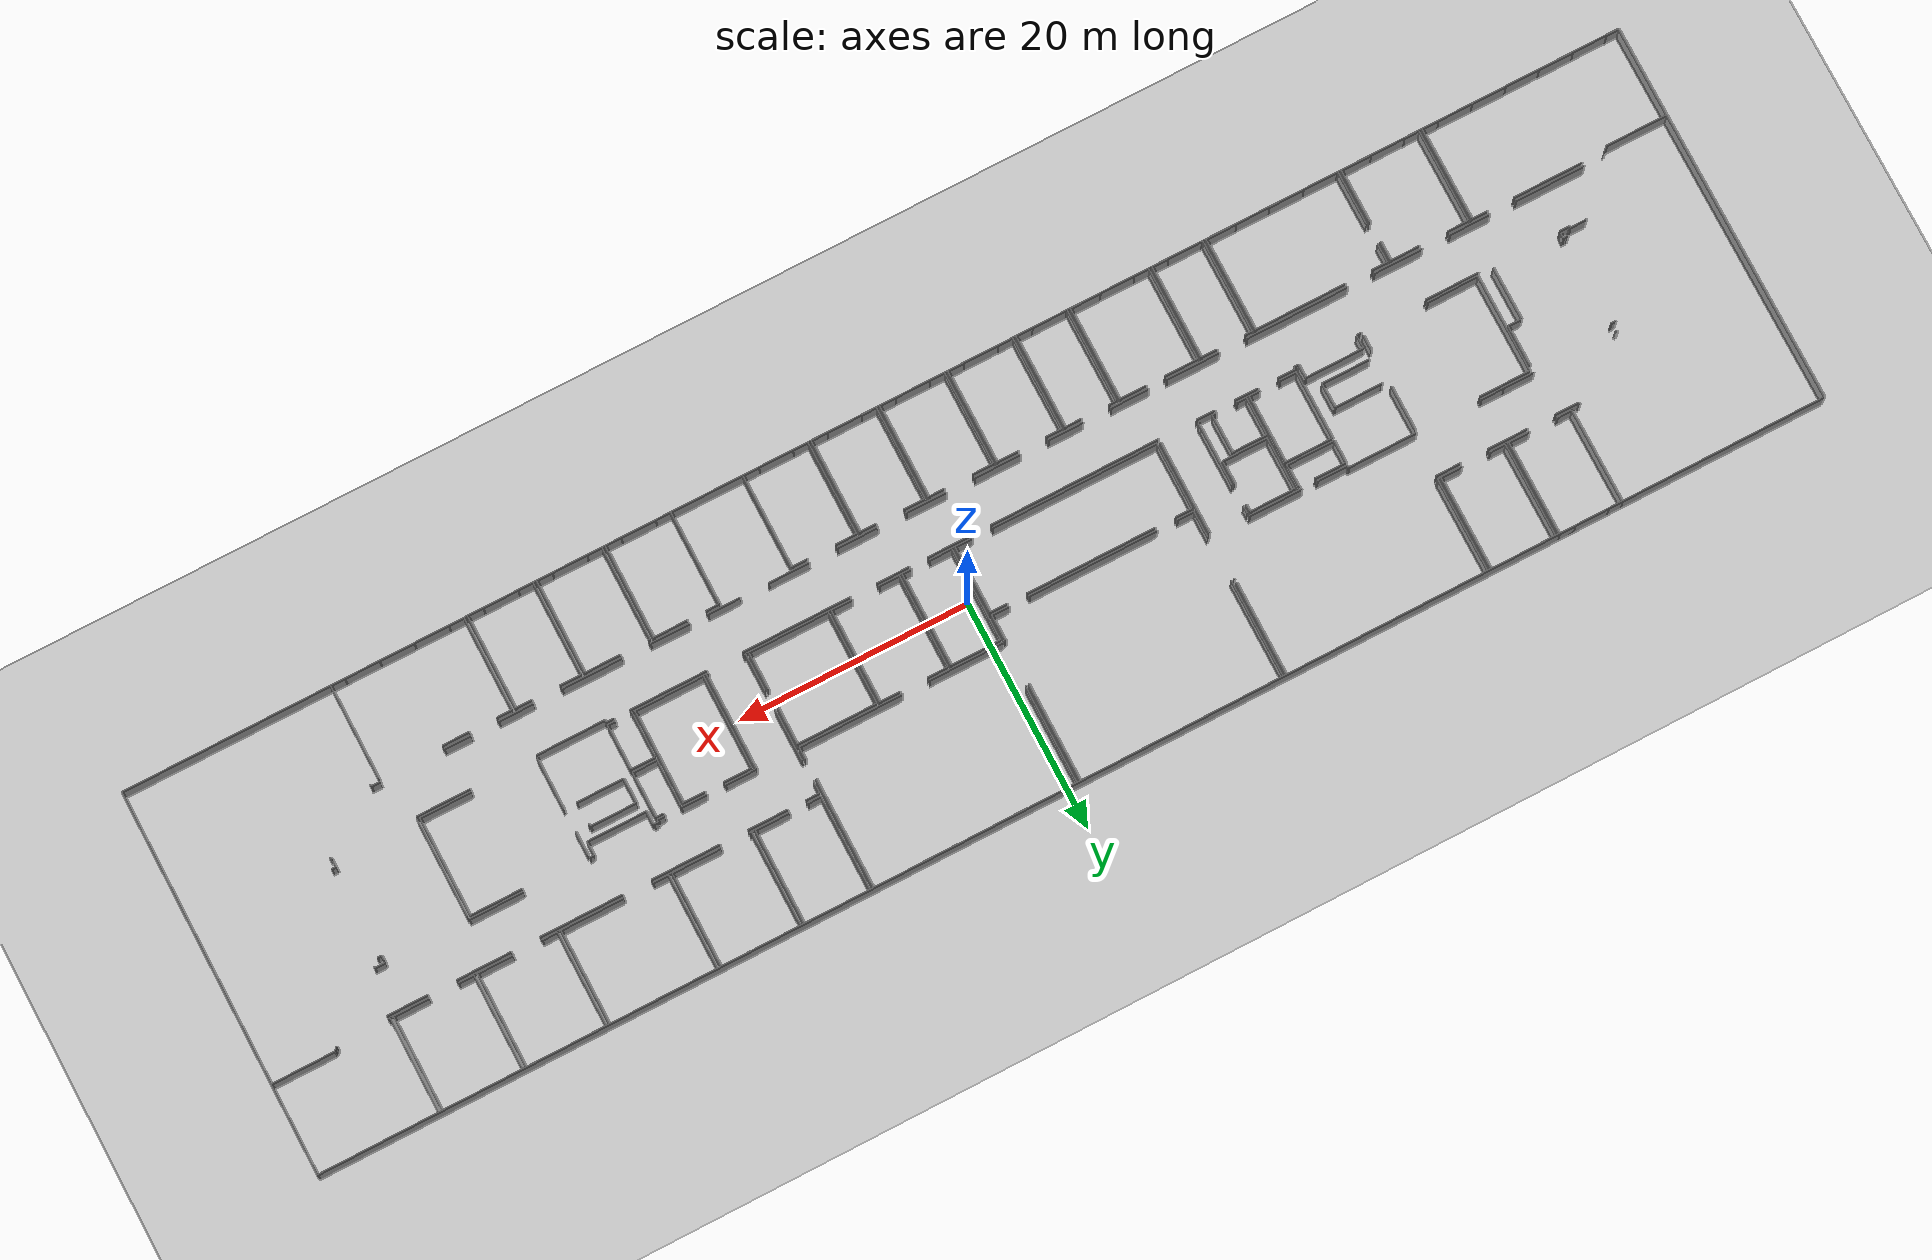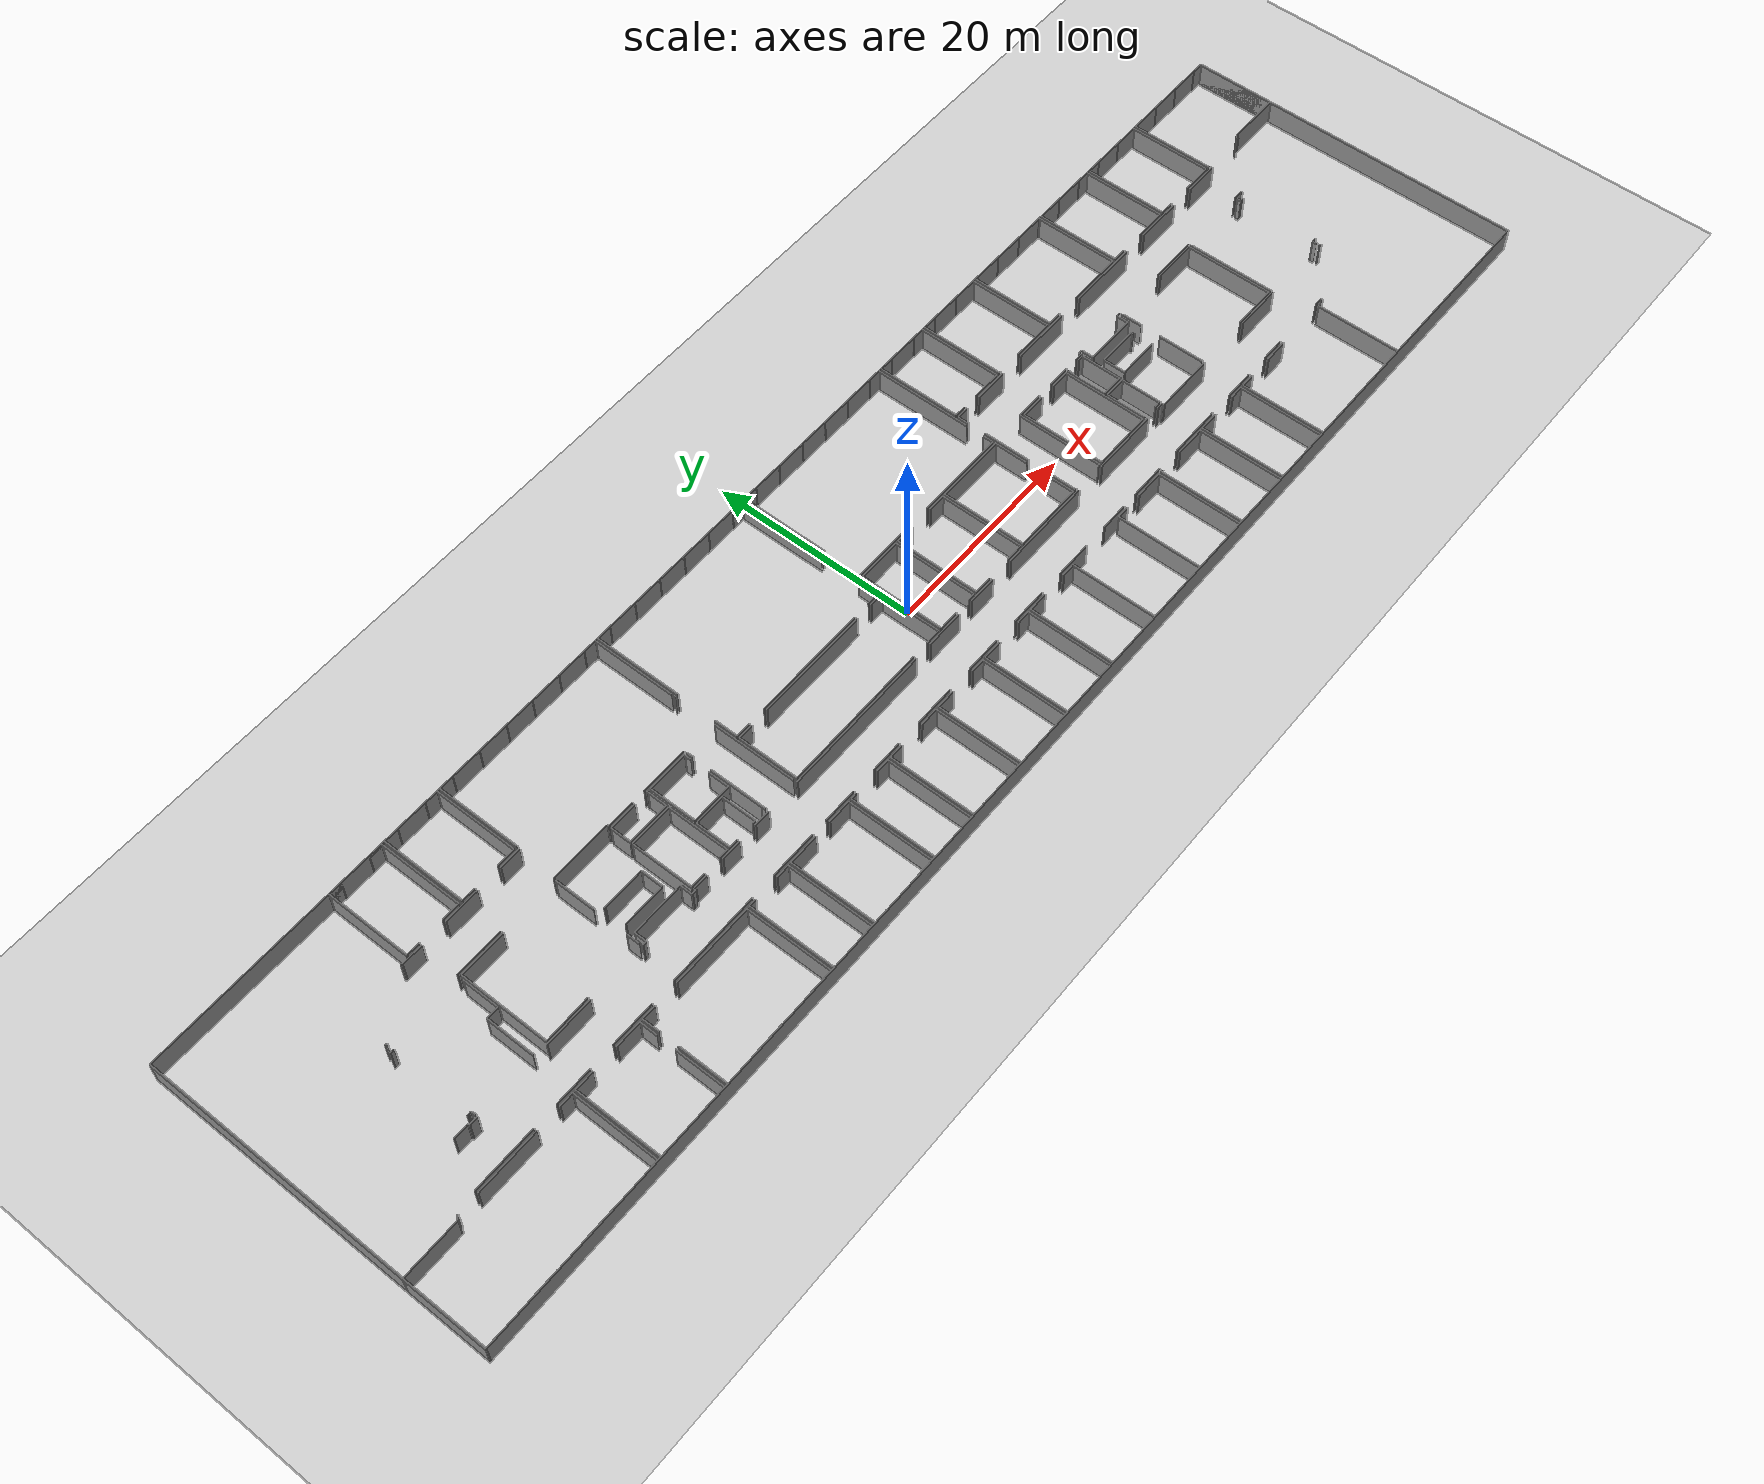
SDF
<sdf version="1.6">
  <world name="default">
    <light name="sun" type="directional">
      <cast_shadows>1</cast_shadows>
      <pose frame="">0 0 10 0 -0 0</pose>
      <diffuse>0.8 0.8 0.8 1</diffuse>
      <specular>0.1 0.1 0.1 1</specular>
      <attenuation>
        <range>1000</range>
        <constant>0.9</constant>
        <linear>0.01</linear>
        <quadratic>0.001</quadratic>
      </attenuation>
      <direction>-0.5 0.5 -1</direction>
    </light>
    <model name="ground_plane">
      <static>1</static>
      <link name="link">
        <collision name="collision">
          <geometry>
            <plane>
              <normal>0 0 1</normal>
              <size>100 100</size>
            </plane>
          </geometry>
          <surface>
            <friction>
              <ode>
                <mu>100</mu>
                <mu2>50</mu2>
              </ode>
              <torsional>
                <ode />
              </torsional>
            </friction>
            <contact>
              <ode />
            </contact>
            <bounce />
          </surface>
          <max_contacts>10</max_contacts>
        </collision>
        <visual name="visual">
          <cast_shadows>0</cast_shadows>
          <geometry>
            <plane>
              <normal>0 0 1</normal>
              <size>100 100</size>
            </plane>
          </geometry>
          <material>
            <script>
              <uri>file://media/materials/scripts/gazebo.material</uri>
              <name>Gazebo/Grey</name>
            </script>
          </material>
        </visual>
        <self_collide>0</self_collide>
        <kinematic>0</kinematic>
        <gravity>1</gravity>
      </link>
    </model>
    <gravity>0 0 -9.8</gravity>
    <magnetic_field>6e-06 2.3e-05 -4.2e-05</magnetic_field>
    <atmosphere type="adiabatic" />
    <physics default="0" name="default_physics" type="ode">
      <max_step_size>0.001</max_step_size>
      <real_time_factor>1</real_time_factor>
      <real_time_update_rate>1000</real_time_update_rate>
    </physics>
    <scene>
      <ambient>0.4 0.4 0.4 1</ambient>
      <background>0.7 0.7 0.7 1</background>
      <shadows>1</shadows>
    </scene>
    <spherical_coordinates>
      <surface_model>EARTH_WGS84</surface_model>
      <latitude_deg>0</latitude_deg>
      <longitude_deg>0</longitude_deg>
      <elevation>0</elevation>
      <heading_deg>0</heading_deg>
    </spherical_coordinates>
  <model name="50041174">
		<static>1</static>
		<link name="Wall_0">
			<collision name="Wall_0_Collision">
				<geometry>
					<box>
						<size>7.88588474232 0.1 2.5</size>
					</box>
				</geometry>
				<pose frame="">3.94294237116 0 1.25 0 0 0</pose>
			</collision>
			<visual name="Wall_0_Visual">
				<pose frame="">3.94294237116 0 1.25 0 0 0</pose>
				<geometry>
					<box>
						<size>7.88588474232 0.1 2.5</size>
					</box>
				</geometry>
				<material>
					<script>
						<uri>file://media/materials/scripts/gazebo.material</uri>
						<name>Gazebo/Grey</name>
					</script>
					<ambient>1 1 1 1</ambient>
				</material>
			</visual>
			<pose frame="">0.0 -33.5118050267 0 0 0 1.57079632679</pose>
		</link>
		<link name="Wall_1">
			<collision name="Wall_1_Collision">
				<geometry>
					<box>
						<size>5.38448844884 0.1 2.5</size>
					</box>
				</geometry>
				<pose frame="">2.69224422442 0 1.25 0 0 0</pose>
			</collision>
			<visual name="Wall_1_Visual">
				<pose frame="">2.69224422442 0 1.25 0 0 0</pose>
				<geometry>
					<box>
						<size>5.38448844884 0.1 2.5</size>
					</box>
				</geometry>
				<material>
					<script>
						<uri>file://media/materials/scripts/gazebo.material</uri>
						<name>Gazebo/Grey</name>
					</script>
					<ambient>1 1 1 1</ambient>
				</material>
			</visual>
			<pose frame="">0.0 -25.6259202843 0 0 0 0.0</pose>
		</link>
		<link name="Wall_2">
			<collision name="Wall_2_Collision">
				<geometry>
					<box>
						<size>0.440170828321 0.1 2.5</size>
					</box>
				</geometry>
				<pose frame="">0.22008541416 0 1.25 0 0 0</pose>
			</collision>
			<visual name="Wall_2_Visual">
				<pose frame="">0.22008541416 0 1.25 0 0 0</pose>
				<geometry>
					<box>
						<size>0.440170828321 0.1 2.5</size>
					</box>
				</geometry>
				<material>
					<script>
						<uri>file://media/materials/scripts/gazebo.material</uri>
						<name>Gazebo/Grey</name>
					</script>
					<ambient>1 1 1 1</ambient>
				</material>
			</visual>
			<pose frame="">5.38448844884 -25.6259202843 0 0 0 0.78825296804</pose>
		</link>
		<link name="Wall_3">
			<collision name="Wall_3_Collision">
				<geometry>
					<box>
						<size>6.0684183803 0.1 2.5</size>
					</box>
				</geometry>
				<pose frame="">3.03420919015 0 1.25 0 0 0</pose>
			</collision>
			<visual name="Wall_3_Visual">
				<pose frame="">3.03420919015 0 1.25 0 0 0</pose>
				<geometry>
					<box>
						<size>6.0684183803 0.1 2.5</size>
					</box>
				</geometry>
				<material>
					<script>
						<uri>file://media/materials/scripts/gazebo.material</uri>
						<name>Gazebo/Grey</name>
					</script>
					<ambient>1 1 1 1</ambient>
				</material>
			</visual>
			<pose frame="">7.72480324956 -25.3137852247 0 0 0 0.0</pose>
		</link>
		<link name="Wall_4">
			<collision name="Wall_4_Collision">
				<geometry>
					<box>
						<size>1.3808073115 0.1 2.5</size>
					</box>
				</geometry>
				<pose frame="">0.69040365575 0 1.25 0 0 0</pose>
			</collision>
			<visual name="Wall_4_Visual">
				<pose frame="">0.69040365575 0 1.25 0 0 0</pose>
				<geometry>
					<box>
						<size>1.3808073115 0.1 2.5</size>
					</box>
				</geometry>
				<material>
					<script>
						<uri>file://media/materials/scripts/gazebo.material</uri>
						<name>Gazebo/Grey</name>
					</script>
					<ambient>1 1 1 1</ambient>
				</material>
			</visual>
			<pose frame="">16.141025641 -25.3137852247 0 0 0 0.0</pose>
		</link>
		<link name="Wall_5">
			<collision name="Wall_5_Collision">
				<geometry>
					<box>
						<size>8.19789286621 0.1 2.5</size>
					</box>
				</geometry>
				<pose frame="">4.0989464331 0 1.25 0 0 0</pose>
			</collision>
			<visual name="Wall_5_Visual">
				<pose frame="">4.0989464331 0 1.25 0 0 0</pose>
				<geometry>
					<box>
						<size>8.19789286621 0.1 2.5</size>
					</box>
				</geometry>
				<material>
					<script>
						<uri>file://media/materials/scripts/gazebo.material</uri>
						<name>Gazebo/Grey</name>
					</script>
					<ambient>1 1 1 1</ambient>
				</material>
			</visual>
			<pose frame="">17.5218329525 -25.3137852247 0 0 0 -1.57079632679</pose>
		</link>
		<link name="Wall_6">
			<collision name="Wall_6_Collision">
				<geometry>
					<box>
						<size>1.37928408225 0.1 2.5</size>
					</box>
				</geometry>
				<pose frame="">0.689642041127 0 1.25 0 0 0</pose>
			</collision>
			<visual name="Wall_6_Visual">
				<pose frame="">0.689642041127 0 1.25 0 0 0</pose>
				<geometry>
					<box>
						<size>1.37928408225 0.1 2.5</size>
					</box>
				</geometry>
				<material>
					<script>
						<uri>file://media/materials/scripts/gazebo.material</uri>
						<name>Gazebo/Grey</name>
					</script>
					<ambient>1 1 1 1</ambient>
				</material>
			</visual>
			<pose frame="">17.5218329525 -33.5116780909 0 0 0 3.14159265359</pose>
		</link>
		<link name="Wall_7">
			<collision name="Wall_7_Collision">
				<geometry>
					<box>
						<size>2.99162223915 0.1 2.5</size>
					</box>
				</geometry>
				<pose frame="">1.49581111957 0 1.25 0 0 0</pose>
			</collision>
			<visual name="Wall_7_Visual">
				<pose frame="">1.49581111957 0 1.25 0 0 0</pose>
				<geometry>
					<box>
						<size>2.99162223915 0.1 2.5</size>
					</box>
				</geometry>
				<material>
					<script>
						<uri>file://media/materials/scripts/gazebo.material</uri>
						<name>Gazebo/Grey</name>
					</script>
					<ambient>1 1 1 1</ambient>
				</material>
			</visual>
			<pose frame="">13.1335364306 -33.5116780909 0 0 0 3.14159265359</pose>
		</link>
		<link name="Wall_8">
			<collision name="Wall_8_Collision">
				<geometry>
					<box>
						<size>3.02665651181 0.1 2.5</size>
					</box>
				</geometry>
				<pose frame="">1.5133282559 0 1.25 0 0 0</pose>
			</collision>
			<visual name="Wall_8_Visual">
				<pose frame="">1.5133282559 0 1.25 0 0 0</pose>
				<geometry>
					<box>
						<size>3.02665651181 0.1 2.5</size>
					</box>
				</geometry>
				<material>
					<script>
						<uri>file://media/materials/scripts/gazebo.material</uri>
						<name>Gazebo/Grey</name>
					</script>
					<ambient>1 1 1 1</ambient>
				</material>
			</visual>
			<pose frame="">7.16666666667 -33.5116780909 0 0 0 3.14159265359</pose>
		</link>
		<link name="Wall_9">
			<collision name="Wall_9_Collision">
				<geometry>
					<box>
						<size>1.14534146426 0.1 2.5</size>
					</box>
				</geometry>
				<pose frame="">0.572670732128 0 1.25 0 0 0</pose>
			</collision>
			<visual name="Wall_9_Visual">
				<pose frame="">0.572670732128 0 1.25 0 0 0</pose>
				<geometry>
					<box>
						<size>1.14534146426 0.1 2.5</size>
					</box>
				</geometry>
				<material>
					<script>
						<uri>file://media/materials/scripts/gazebo.material</uri>
						<name>Gazebo/Grey</name>
					</script>
					<ambient>1 1 1 1</ambient>
				</material>
			</visual>
			<pose frame="">1.14534145722 -33.5116780909 0 0 0 -3.14148182571</pose>
		</link>
		<link name="Wall_10">
			<collision name="Wall_10_Collision">
				<geometry>
					<box>
						<size>8.20614369129 0.1 2.5</size>
					</box>
				</geometry>
				<pose frame="">4.10307184565 0 1.25 0 0 0</pose>
			</collision>
			<visual name="Wall_10_Visual">
				<pose frame="">4.10307184565 0 1.25 0 0 0</pose>
				<geometry>
					<box>
						<size>8.20614369129 0.1 2.5</size>
					</box>
				</geometry>
				<material>
					<script>
						<uri>file://media/materials/scripts/gazebo.material</uri>
						<name>Gazebo/Grey</name>
					</script>
					<ambient>1 1 1 1</ambient>
				</material>
			</visual>
			<pose frame="">17.8136582889 -33.5176440721 0 0 0 1.57079632679</pose>
		</link>
		<link name="Wall_11">
			<collision name="Wall_11_Collision">
				<geometry>
					<box>
						<size>1.86773292714 0.1 2.5</size>
					</box>
				</geometry>
				<pose frame="">0.933866463569 0 1.25 0 0 0</pose>
			</collision>
			<visual name="Wall_11_Visual">
				<pose frame="">0.933866463569 0 1.25 0 0 0</pose>
				<geometry>
					<box>
						<size>1.86773292714 0.1 2.5</size>
					</box>
				</geometry>
				<material>
					<script>
						<uri>file://media/materials/scripts/gazebo.material</uri>
						<name>Gazebo/Grey</name>
					</script>
					<ambient>1 1 1 1</ambient>
				</material>
			</visual>
			<pose frame="">17.8136582889 -25.3115003808 0 0 0 0.0</pose>
		</link>
		<link name="Wall_12">
			<collision name="Wall_12_Collision">
				<geometry>
					<box>
						<size>2.53681137345 0.1 2.5</size>
					</box>
				</geometry>
				<pose frame="">1.26840568672 0 1.25 0 0 0</pose>
			</collision>
			<visual name="Wall_12_Visual">
				<pose frame="">1.26840568672 0 1.25 0 0 0</pose>
				<geometry>
					<box>
						<size>2.53681137345 0.1 2.5</size>
					</box>
				</geometry>
				<material>
					<script>
						<uri>file://media/materials/scripts/gazebo.material</uri>
						<name>Gazebo/Grey</name>
					</script>
					<ambient>1 1 1 1</ambient>
				</material>
			</visual>
			<pose frame="">22.1799949226 -25.3115003808 0 0 0 0.0</pose>
		</link>
		<link name="Wall_13">
			<collision name="Wall_13_Collision">
				<geometry>
					<box>
						<size>1.69941609546 0.1 2.5</size>
					</box>
				</geometry>
				<pose frame="">0.849708047728 0 1.25 0 0 0</pose>
			</collision>
			<visual name="Wall_13_Visual">
				<pose frame="">0.849708047728 0 1.25 0 0 0</pose>
				<geometry>
					<box>
						<size>1.69941609546 0.1 2.5</size>
					</box>
				</geometry>
				<material>
					<script>
						<uri>file://media/materials/scripts/gazebo.material</uri>
						<name>Gazebo/Grey</name>
					</script>
					<ambient>1 1 1 1</ambient>
				</material>
			</visual>
			<pose frame="">24.716806296 -25.3115003808 0 0 0 -1.57079632679</pose>
		</link>
		<link name="Wall_14">
			<collision name="Wall_14_Collision">
				<geometry>
					<box>
						<size>4.73635440467 0.1 2.5</size>
					</box>
				</geometry>
				<pose frame="">2.36817720234 0 1.25 0 0 0</pose>
			</collision>
			<visual name="Wall_14_Visual">
				<pose frame="">2.36817720234 0 1.25 0 0 0</pose>
				<geometry>
					<box>
						<size>4.73635440467 0.1 2.5</size>
					</box>
				</geometry>
				<material>
					<script>
						<uri>file://media/materials/scripts/gazebo.material</uri>
						<name>Gazebo/Grey</name>
					</script>
					<ambient>1 1 1 1</ambient>
				</material>
			</visual>
			<pose frame="">24.716806296 -28.7764661081 0 0 0 -1.57079632679</pose>
		</link>
		<link name="Wall_15">
			<collision name="Wall_15_Collision">
				<geometry>
					<box>
						<size>2.5817466362 0.1 2.5</size>
					</box>
				</geometry>
				<pose frame="">1.2908733181 0 1.25 0 0 0</pose>
			</collision>
			<visual name="Wall_15_Visual">
				<pose frame="">1.2908733181 0 1.25 0 0 0</pose>
				<geometry>
					<box>
						<size>2.5817466362 0.1 2.5</size>
					</box>
				</geometry>
				<material>
					<script>
						<uri>file://media/materials/scripts/gazebo.material</uri>
						<name>Gazebo/Grey</name>
					</script>
					<ambient>1 1 1 1</ambient>
				</material>
			</visual>
			<pose frame="">24.716806296 -33.5128205128 0 0 0 3.14159265359</pose>
		</link>
		<link name="Wall_16">
			<collision name="Wall_16_Collision">
				<geometry>
					<box>
						<size>1.34933586199 0.1 2.5</size>
					</box>
				</geometry>
				<pose frame="">0.674667930995 0 1.25 0 0 0</pose>
			</collision>
			<visual name="Wall_16_Visual">
				<pose frame="">0.674667930995 0 1.25 0 0 0</pose>
				<geometry>
					<box>
						<size>1.34933586199 0.1 2.5</size>
					</box>
				</geometry>
				<material>
					<script>
						<uri>file://media/materials/scripts/gazebo.material</uri>
						<name>Gazebo/Grey</name>
					</script>
					<ambient>1 1 1 1</ambient>
				</material>
			</visual>
			<pose frame="">19.1629855293 -33.5128205128 0 0 0 -3.13801788048</pose>
		</link>
		<link name="Wall_17">
			<collision name="Wall_17_Collision">
				<geometry>
					<box>
						<size>4.76364559533 0.1 2.5</size>
					</box>
				</geometry>
				<pose frame="">2.38182279766 0 1.25 0 0 0</pose>
			</collision>
			<visual name="Wall_17_Visual">
				<pose frame="">2.38182279766 0 1.25 0 0 0</pose>
				<geometry>
					<box>
						<size>4.76364559533 0.1 2.5</size>
					</box>
				</geometry>
				<material>
					<script>
						<uri>file://media/materials/scripts/gazebo.material</uri>
						<name>Gazebo/Grey</name>
					</script>
					<ambient>1 1 1 1</ambient>
				</material>
			</visual>
			<pose frame="">25.0048235593 -33.5223406956 0 0 0 1.57079632679</pose>
		</link>
		<link name="Wall_18">
			<collision name="Wall_18_Collision">
				<geometry>
					<box>
						<size>1.65486164001 0.1 2.5</size>
					</box>
				</geometry>
				<pose frame="">0.827430820005 0 1.25 0 0 0</pose>
			</collision>
			<visual name="Wall_18_Visual">
				<pose frame="">0.827430820005 0 1.25 0 0 0</pose>
				<geometry>
					<box>
						<size>1.65486164001 0.1 2.5</size>
					</box>
				</geometry>
				<material>
					<script>
						<uri>file://media/materials/scripts/gazebo.material</uri>
						<name>Gazebo/Grey</name>
					</script>
					<ambient>1 1 1 1</ambient>
				</material>
			</visual>
			<pose frame="">25.0048235593 -26.96458492 0 0 0 1.57079632679</pose>
		</link>
		<link name="Wall_19">
			<collision name="Wall_19_Collision">
				<geometry>
					<box>
						<size>1.37585681645 0.1 2.5</size>
					</box>
				</geometry>
				<pose frame="">0.687928408225 0 1.25 0 0 0</pose>
			</collision>
			<visual name="Wall_19_Visual">
				<pose frame="">0.687928408225 0 1.25 0 0 0</pose>
				<geometry>
					<box>
						<size>1.37585681645 0.1 2.5</size>
					</box>
				</geometry>
				<material>
					<script>
						<uri>file://media/materials/scripts/gazebo.material</uri>
						<name>Gazebo/Grey</name>
					</script>
					<ambient>1 1 1 1</ambient>
				</material>
			</visual>
			<pose frame="">25.0048235593 -25.30972328 0 0 0 0.0</pose>
		</link>
		<link name="Wall_20">
			<collision name="Wall_20_Collision">
				<geometry>
					<box>
						<size>7.94643310485 0.1 2.5</size>
					</box>
				</geometry>
				<pose frame="">3.97321655242 0 1.25 0 0 0</pose>
			</collision>
			<visual name="Wall_20_Visual">
				<pose frame="">3.97321655242 0 1.25 0 0 0</pose>
				<geometry>
					<box>
						<size>7.94643310485 0.1 2.5</size>
					</box>
				</geometry>
				<material>
					<script>
						<uri>file://media/materials/scripts/gazebo.material</uri>
						<name>Gazebo/Grey</name>
					</script>
					<ambient>1 1 1 1</ambient>
				</material>
			</visual>
			<pose frame="">28.7527291191 -25.30972328 0 0 0 0.0</pose>
		</link>
		<link name="Wall_21">
			<collision name="Wall_21_Collision">
				<geometry>
					<box>
						<size>8.1987814166 0.1 2.5</size>
					</box>
				</geometry>
				<pose frame="">4.0993907083 0 1.25 0 0 0</pose>
			</collision>
			<visual name="Wall_21_Visual">
				<pose frame="">4.0993907083 0 1.25 0 0 0</pose>
				<geometry>
					<box>
						<size>8.1987814166 0.1 2.5</size>
					</box>
				</geometry>
				<material>
					<script>
						<uri>file://media/materials/scripts/gazebo.material</uri>
						<name>Gazebo/Grey</name>
					</script>
					<ambient>1 1 1 1</ambient>
				</material>
			</visual>
			<pose frame="">36.6991622239 -25.30972328 0 0 0 -1.57079632679</pose>
		</link>
		<link name="Wall_22">
			<collision name="Wall_22_Collision">
				<geometry>
					<box>
						<size>2.57781162732 0.1 2.5</size>
					</box>
				</geometry>
				<pose frame="">1.28890581366 0 1.25 0 0 0</pose>
			</collision>
			<visual name="Wall_22_Visual">
				<pose frame="">1.28890581366 0 1.25 0 0 0</pose>
				<geometry>
					<box>
						<size>2.57781162732 0.1 2.5</size>
					</box>
				</geometry>
				<material>
					<script>
						<uri>file://media/materials/scripts/gazebo.material</uri>
						<name>Gazebo/Grey</name>
					</script>
					<ambient>1 1 1 1</ambient>
				</material>
			</visual>
			<pose frame="">36.6991622239 -33.5085046966 0 0 0 3.14159265359</pose>
		</link>
		<link name="Wall_23">
			<collision name="Wall_23_Collision">
				<geometry>
					<box>
						<size>3.02868748413 0.1 2.5</size>
					</box>
				</geometry>
				<pose frame="">1.51434374207 0 1.25 0 0 0</pose>
			</collision>
			<visual name="Wall_23_Visual">
				<pose frame="">1.51434374207 0 1.25 0 0 0</pose>
				<geometry>
					<box>
						<size>3.02868748413 0.1 2.5</size>
					</box>
				</geometry>
				<material>
					<script>
						<uri>file://media/materials/scripts/gazebo.material</uri>
						<name>Gazebo/Grey</name>
					</script>
					<ambient>1 1 1 1</ambient>
				</material>
			</visual>
			<pose frame="">31.1678090886 -33.5085046966 0 0 0 3.14159265359</pose>
		</link>
		<link name="Wall_24">
			<collision name="Wall_24_Collision">
				<geometry>
					<box>
						<size>0.150169093842 0.1 2.5</size>
					</box>
				</geometry>
				<pose frame="">0.0750845469211 0 1.25 0 0 0</pose>
			</collision>
			<visual name="Wall_24_Visual">
				<pose frame="">0.0750845469211 0 1.25 0 0 0</pose>
				<geometry>
					<box>
						<size>0.150169093842 0.1 2.5</size>
					</box>
				</geometry>
				<material>
					<script>
						<uri>file://media/materials/scripts/gazebo.material</uri>
						<name>Gazebo/Grey</name>
					</script>
					<ambient>1 1 1 1</ambient>
				</material>
			</visual>
			<pose frame="">25.1543538969 -33.5085046966 0 0 0 -3.04932566591</pose>
		</link>
		<link name="Wall_25">
			<collision name="Wall_25_Collision">
				<geometry>
					<box>
						<size>8.21769484641 0.1 2.5</size>
					</box>
				</geometry>
				<pose frame="">4.1088474232 0 1.25 0 0 0</pose>
			</collision>
			<visual name="Wall_25_Visual">
				<pose frame="">4.1088474232 0 1.25 0 0 0</pose>
				<geometry>
					<box>
						<size>8.21769484641 0.1 2.5</size>
					</box>
				</geometry>
				<material>
					<script>
						<uri>file://media/materials/scripts/gazebo.material</uri>
						<name>Gazebo/Grey</name>
					</script>
					<ambient>1 1 1 1</ambient>
				</material>
			</visual>
			<pose frame="">36.982863671 -33.5272911907 0 0 0 1.57079632679</pose>
		</link>
		<link name="Wall_26">
			<collision name="Wall_26_Collision">
				<geometry>
					<box>
						<size>0.662096978929 0.1 2.5</size>
					</box>
				</geometry>
				<pose frame="">0.331048489464 0 1.25 0 0 0</pose>
			</collision>
			<visual name="Wall_26_Visual">
				<pose frame="">0.331048489464 0 1.25 0 0 0</pose>
				<geometry>
					<box>
						<size>0.662096978929 0.1 2.5</size>
					</box>
				</geometry>
				<material>
					<script>
						<uri>file://media/materials/scripts/gazebo.material</uri>
						<name>Gazebo/Grey</name>
					</script>
					<ambient>1 1 1 1</ambient>
				</material>
			</visual>
			<pose frame="">36.982863671 -25.3095963442 0 0 0 0.0</pose>
		</link>
		<link name="Wall_27">
			<collision name="Wall_27_Collision">
				<geometry>
					<box>
						<size>1.37255648642 0.1 2.5</size>
					</box>
				</geometry>
				<pose frame="">0.686278243209 0 1.25 0 0 0</pose>
			</collision>
			<visual name="Wall_27_Visual">
				<pose frame="">0.686278243209 0 1.25 0 0 0</pose>
				<geometry>
					<box>
						<size>1.37255648642 0.1 2.5</size>
					</box>
				</geometry>
				<material>
					<script>
						<uri>file://media/materials/scripts/gazebo.material</uri>
						<name>Gazebo/Grey</name>
					</script>
					<ambient>1 1 1 1</ambient>
				</material>
			</visual>
			<pose frame="">40.1141152577 -25.3095963442 0 0 0 0.0</pose>
		</link>
		<link name="Wall_28">
			<collision name="Wall_28_Collision">
				<geometry>
					<box>
						<size>8.20842853516 0.1 2.5</size>
					</box>
				</geometry>
				<pose frame="">4.10421426758 0 1.25 0 0 0</pose>
			</collision>
			<visual name="Wall_28_Visual">
				<pose frame="">4.10421426758 0 1.25 0 0 0</pose>
				<geometry>
					<box>
						<size>8.20842853516 0.1 2.5</size>
					</box>
				</geometry>
				<material>
					<script>
						<uri>file://media/materials/scripts/gazebo.material</uri>
						<name>Gazebo/Grey</name>
					</script>
					<ambient>1 1 1 1</ambient>
				</material>
			</visual>
			<pose frame="">41.4866717441 -25.3095963442 0 0 0 -1.57079632679</pose>
		</link>
		<link name="Wall_29">
			<collision name="Wall_29_Collision">
				<geometry>
					<box>
						<size>1.36646356943 0.1 2.5</size>
					</box>
				</geometry>
				<pose frame="">0.683231784717 0 1.25 0 0 0</pose>
			</collision>
			<visual name="Wall_29_Visual">
				<pose frame="">0.683231784717 0 1.25 0 0 0</pose>
				<geometry>
					<box>
						<size>1.36646356943 0.1 2.5</size>
					</box>
				</geometry>
				<material>
					<script>
						<uri>file://media/materials/scripts/gazebo.material</uri>
						<name>Gazebo/Grey</name>
					</script>
					<ambient>1 1 1 1</ambient>
				</material>
			</visual>
			<pose frame="">41.4866717441 -33.5180248794 0 0 0 3.14159265359</pose>
		</link>
		<link name="Wall_30">
			<collision name="Wall_30_Collision">
				<geometry>
					<box>
						<size>0.16464278967 0.1 2.5</size>
					</box>
				</geometry>
				<pose frame="">0.0823213948351 0 1.25 0 0 0</pose>
			</collision>
			<visual name="Wall_30_Visual">
				<pose frame="">0.0823213948351 0 1.25 0 0 0</pose>
				<geometry>
					<box>
						<size>0.16464278967 0.1 2.5</size>
					</box>
				</geometry>
				<material>
					<script>
						<uri>file://media/materials/scripts/gazebo.material</uri>
						<name>Gazebo/Grey</name>
					</script>
					<ambient>1 1 1 1</ambient>
				</material>
			</visual>
			<pose frame="">37.1472454938 -33.5180248794 0 0 0 -3.08528159239</pose>
		</link>
		<link name="Wall_31">
			<collision name="Wall_31_Collision">
				<geometry>
					<box>
						<size>8.20500126936 0.1 2.5</size>
					</box>
				</geometry>
				<pose frame="">4.10250063468 0 1.25 0 0 0</pose>
			</collision>
			<visual name="Wall_31_Visual">
				<pose frame="">4.10250063468 0 1.25 0 0 0</pose>
				<geometry>
					<box>
						<size>8.20500126936 0.1 2.5</size>
					</box>
				</geometry>
				<material>
					<script>
						<uri>file://media/materials/scripts/gazebo.material</uri>
						<name>Gazebo/Grey</name>
					</script>
					<ambient>1 1 1 1</ambient>
				</material>
			</visual>
			<pose frame="">41.7788778878 -33.5200558517 0 0 0 1.57079632679</pose>
		</link>
		<link name="Wall_32">
			<collision name="Wall_32_Collision">
				<geometry>
					<box>
						<size>2.95443005839 0.1 2.5</size>
					</box>
				</geometry>
				<pose frame="">1.4772150292 0 1.25 0 0 0</pose>
			</collision>
			<visual name="Wall_32_Visual">
				<pose frame="">1.4772150292 0 1.25 0 0 0</pose>
				<geometry>
					<box>
						<size>2.95443005839 0.1 2.5</size>
					</box>
				</geometry>
				<material>
					<script>
						<uri>file://media/materials/scripts/gazebo.material</uri>
						<name>Gazebo/Grey</name>
					</script>
					<ambient>1 1 1 1</ambient>
				</material>
			</visual>
			<pose frame="">41.7788778878 -25.3150545824 0 0 0 0.0</pose>
		</link>
		<link name="Wall_33">
			<collision name="Wall_33_Collision">
				<geometry>
					<box>
						<size>2.35313531353 0.1 2.5</size>
					</box>
				</geometry>
				<pose frame="">1.17656765677 0 1.25 0 0 0</pose>
			</collision>
			<visual name="Wall_33_Visual">
				<pose frame="">1.17656765677 0 1.25 0 0 0</pose>
				<geometry>
					<box>
						<size>2.35313531353 0.1 2.5</size>
					</box>
				</geometry>
				<material>
					<script>
						<uri>file://media/materials/scripts/gazebo.material</uri>
						<name>Gazebo/Grey</name>
					</script>
					<ambient>1 1 1 1</ambient>
				</material>
			</visual>
			<pose frame="">46.3238131505 -25.3150545824 0 0 0 0.0</pose>
		</link>
		<link name="Wall_34">
			<collision name="Wall_34_Collision">
				<geometry>
					<box>
						<size>8.19345011424 0.1 2.5</size>
					</box>
				</geometry>
				<pose frame="">4.09672505712 0 1.25 0 0 0</pose>
			</collision>
			<visual name="Wall_34_Visual">
				<pose frame="">4.09672505712 0 1.25 0 0 0</pose>
				<geometry>
					<box>
						<size>8.19345011424 0.1 2.5</size>
					</box>
				</geometry>
				<material>
					<script>
						<uri>file://media/materials/scripts/gazebo.material</uri>
						<name>Gazebo/Grey</name>
					</script>
					<ambient>1 1 1 1</ambient>
				</material>
			</visual>
			<pose frame="">48.6769484641 -25.3150545824 0 0 0 -1.57079632679</pose>
		</link>
		<link name="Wall_35">
			<collision name="Wall_35_Collision">
				<geometry>
					<box>
						<size>2.56143691292 0.1 2.5</size>
					</box>
				</geometry>
				<pose frame="">1.28071845646 0 1.25 0 0 0</pose>
			</collision>
			<visual name="Wall_35_Visual">
				<pose frame="">1.28071845646 0 1.25 0 0 0</pose>
				<geometry>
					<box>
						<size>2.56143691292 0.1 2.5</size>
					</box>
				</geometry>
				<material>
					<script>
						<uri>file://media/materials/scripts/gazebo.material</uri>
						<name>Gazebo/Grey</name>
					</script>
					<ambient>1 1 1 1</ambient>
				</material>
			</visual>
			<pose frame="">48.6769484641 -33.5085046966 0 0 0 3.14159265359</pose>
		</link>
		<link name="Wall_36">
			<collision name="Wall_36_Collision">
				<geometry>
					<box>
						<size>1.36397376683 0.1 2.5</size>
					</box>
				</geometry>
				<pose frame="">0.681986883416 0 1.25 0 0 0</pose>
			</collision>
			<visual name="Wall_36_Visual">
				<pose frame="">0.681986883416 0 1.25 0 0 0</pose>
				<geometry>
					<box>
						<size>1.36397376683 0.1 2.5</size>
					</box>
				</geometry>
				<material>
					<script>
						<uri>file://media/materials/scripts/gazebo.material</uri>
						<name>Gazebo/Grey</name>
					</script>
					<ambient>1 1 1 1</ambient>
				</material>
			</visual>
			<pose frame="">43.1428027418 -33.5085046966 0 0 0 -3.13312380069</pose>
		</link>
		<link name="Wall_37">
			<collision name="Wall_37_Collision">
				<geometry>
					<box>
						<size>8.21997969028 0.1 2.5</size>
					</box>
				</geometry>
				<pose frame="">4.10998984514 0 1.25 0 0 0</pose>
			</collision>
			<visual name="Wall_37_Visual">
				<pose frame="">4.10998984514 0 1.25 0 0 0</pose>
				<geometry>
					<box>
						<size>8.21997969028 0.1 2.5</size>
					</box>
				</geometry>
				<material>
					<script>
						<uri>file://media/materials/scripts/gazebo.material</uri>
						<name>Gazebo/Grey</name>
					</script>
					<ambient>1 1 1 1</ambient>
				</material>
			</visual>
			<pose frame="">48.9748667174 -33.5262757045 0 0 0 1.57079632679</pose>
		</link>
		<link name="Wall_38">
			<collision name="Wall_38_Collision">
				<geometry>
					<box>
						<size>0.659050520437 0.1 2.5</size>
					</box>
				</geometry>
				<pose frame="">0.329525260218 0 1.25 0 0 0</pose>
			</collision>
			<visual name="Wall_38_Visual">
				<pose frame="">0.329525260218 0 1.25 0 0 0</pose>
				<geometry>
					<box>
						<size>0.659050520437 0.1 2.5</size>
					</box>
				</geometry>
				<material>
					<script>
						<uri>file://media/materials/scripts/gazebo.material</uri>
						<name>Gazebo/Grey</name>
					</script>
					<ambient>1 1 1 1</ambient>
				</material>
			</visual>
			<pose frame="">48.9748667174 -25.3062960142 0 0 0 0.0</pose>
		</link>
		<link name="Wall_39">
			<collision name="Wall_39_Collision">
				<geometry>
					<box>
						<size>1.38220360498 0.1 2.5</size>
					</box>
				</geometry>
				<pose frame="">0.691101802488 0 1.25 0 0 0</pose>
			</collision>
			<visual name="Wall_39_Visual">
				<pose frame="">0.691101802488 0 1.25 0 0 0</pose>
				<geometry>
					<box>
						<size>1.38220360498 0.1 2.5</size>
					</box>
				</geometry>
				<material>
					<script>
						<uri>file://media/materials/scripts/gazebo.material</uri>
						<name>Gazebo/Grey</name>
					</script>
					<ambient>1 1 1 1</ambient>
				</material>
			</visual>
			<pose frame="">52.0983752221 -25.3062960142 0 0 0 0.0</pose>
		</link>
		<link name="Wall_40">
			<collision name="Wall_40_Collision">
				<geometry>
					<box>
						<size>8.21363290175 0.1 2.5</size>
					</box>
				</geometry>
				<pose frame="">4.10681645088 0 1.25 0 0 0</pose>
			</collision>
			<visual name="Wall_40_Visual">
				<pose frame="">4.10681645088 0 1.25 0 0 0</pose>
				<geometry>
					<box>
						<size>8.21363290175 0.1 2.5</size>
					</box>
				</geometry>
				<material>
					<script>
						<uri>file://media/materials/scripts/gazebo.material</uri>
						<name>Gazebo/Grey</name>
					</script>
					<ambient>1 1 1 1</ambient>
				</material>
			</visual>
			<pose frame="">53.4805788271 -25.3062960142 0 0 0 -1.57079632679</pose>
		</link>
		<link name="Wall_41">
			<collision name="Wall_41_Collision">
				<geometry>
					<box>
						<size>1.36735211983 0.1 2.5</size>
					</box>
				</geometry>
				<pose frame="">0.683676059914 0 1.25 0 0 0</pose>
			</collision>
			<visual name="Wall_41_Visual">
				<pose frame="">0.683676059914 0 1.25 0 0 0</pose>
				<geometry>
					<box>
						<size>1.36735211983 0.1 2.5</size>
					</box>
				</geometry>
				<material>
					<script>
						<uri>file://media/materials/scripts/gazebo.material</uri>
						<name>Gazebo/Grey</name>
					</script>
					<ambient>1 1 1 1</ambient>
				</material>
			</visual>
			<pose frame="">53.4805788271 -33.519928916 0 0 0 3.14159265359</pose>
		</link>
		<link name="Wall_42">
			<collision name="Wall_42_Collision">
				<geometry>
					<box>
						<size>0.166533780676 0.1 2.5</size>
					</box>
				</geometry>
				<pose frame="">0.0832668903378 0 1.25 0 0 0</pose>
			</collision>
			<visual name="Wall_42_Visual">
				<pose frame="">0.0832668903378 0 1.25 0 0 0</pose>
				<geometry>
					<box>
						<size>0.166533780676 0.1 2.5</size>
					</box>
				</geometry>
				<material>
					<script>
						<uri>file://media/materials/scripts/gazebo.material</uri>
						<name>Gazebo/Grey</name>
					</script>
					<ambient>1 1 1 1</ambient>
				</material>
			</visual>
			<pose frame="">49.1412795126 -33.519928916 0 0 0 -3.10347230401</pose>
		</link>
		<link name="Wall_43">
			<collision name="Wall_43_Collision">
				<geometry>
					<box>
						<size>8.21452145215 0.1 2.5</size>
					</box>
				</geometry>
				<pose frame="">4.10726072607 0 1.25 0 0 0</pose>
			</collision>
			<visual name="Wall_43_Visual">
				<pose frame="">4.10726072607 0 1.25 0 0 0</pose>
				<geometry>
					<box>
						<size>8.21452145215 0.1 2.5</size>
					</box>
				</geometry>
				<material>
					<script>
						<uri>file://media/materials/scripts/gazebo.material</uri>
						<name>Gazebo/Grey</name>
					</script>
					<ambient>1 1 1 1</ambient>
				</material>
			</visual>
			<pose frame="">53.769357705 -33.5241177964 0 0 0 1.57079632679</pose>
		</link>
		<link name="Wall_44">
			<collision name="Wall_44_Collision">
				<geometry>
					<box>
						<size>1.39730896167 0.1 2.5</size>
					</box>
				</geometry>
				<pose frame="">0.698654480833 0 1.25 0 0 0</pose>
			</collision>
			<visual name="Wall_44_Visual">
				<pose frame="">0.698654480833 0 1.25 0 0 0</pose>
				<geometry>
					<box>
						<size>1.39730896167 0.1 2.5</size>
					</box>
				</geometry>
				<material>
					<script>
						<uri>file://media/materials/scripts/gazebo.material</uri>
						<name>Gazebo/Grey</name>
					</script>
					<ambient>1 1 1 1</ambient>
				</material>
			</visual>
			<pose frame="">53.769357705 -25.3095963442 0 0 0 0.0</pose>
		</link>
		<link name="Wall_45">
			<collision name="Wall_45_Collision">
				<geometry>
					<box>
						<size>1.86570195481 0.1 2.5</size>
					</box>
				</geometry>
				<pose frame="">0.932850977405 0 1.25 0 0 0</pose>
			</collision>
			<visual name="Wall_45_Visual">
				<pose frame="">0.932850977405 0 1.25 0 0 0</pose>
				<geometry>
					<box>
						<size>1.86570195481 0.1 2.5</size>
					</box>
				</geometry>
				<material>
					<script>
						<uri>file://media/materials/scripts/gazebo.material</uri>
						<name>Gazebo/Grey</name>
					</script>
					<ambient>1 1 1 1</ambient>
				</material>
			</visual>
			<pose frame="">57.6200812389 -25.3095963442 0 0 0 0.0</pose>
		</link>
		<link name="Wall_46">
			<collision name="Wall_46_Collision">
				<geometry>
					<box>
						<size>8.20436659051 0.1 2.5</size>
					</box>
				</geometry>
				<pose frame="">4.10218329525 0 1.25 0 0 0</pose>
			</collision>
			<visual name="Wall_46_Visual">
				<pose frame="">4.10218329525 0 1.25 0 0 0</pose>
				<geometry>
					<box>
						<size>8.20436659051 0.1 2.5</size>
					</box>
				</geometry>
				<material>
					<script>
						<uri>file://media/materials/scripts/gazebo.material</uri>
						<name>Gazebo/Grey</name>
					</script>
					<ambient>1 1 1 1</ambient>
				</material>
			</visual>
			<pose frame="">59.4857831937 -25.3095963442 0 0 0 -1.57079632679</pose>
		</link>
		<link name="Wall_47">
			<collision name="Wall_47_Collision">
				<geometry>
					<box>
						<size>1.36697131252 0.1 2.5</size>
					</box>
				</geometry>
				<pose frame="">0.683485656258 0 1.25 0 0 0</pose>
			</collision>
			<visual name="Wall_47_Visual">
				<pose frame="">0.683485656258 0 1.25 0 0 0</pose>
				<geometry>
					<box>
						<size>1.36697131252 0.1 2.5</size>
					</box>
				</geometry>
				<material>
					<script>
						<uri>file://media/materials/scripts/gazebo.material</uri>
						<name>Gazebo/Grey</name>
					</script>
					<ambient>1 1 1 1</ambient>
				</material>
			</visual>
			<pose frame="">59.4857831937 -33.5139629348 0 0 0 3.14159265359</pose>
		</link>
		<link name="Wall_48">
			<collision name="Wall_48_Collision">
				<geometry>
					<box>
						<size>1.3757673589 0.1 2.5</size>
					</box>
				</geometry>
				<pose frame="">0.687883679449 0 1.25 0 0 0</pose>
			</collision>
			<visual name="Wall_48_Visual">
				<pose frame="">0.687883679449 0 1.25 0 0 0</pose>
				<geometry>
					<box>
						<size>1.3757673589 0.1 2.5</size>
					</box>
				</geometry>
				<material>
					<script>
						<uri>file://media/materials/scripts/gazebo.material</uri>
						<name>Gazebo/Grey</name>
					</script>
					<ambient>1 1 1 1</ambient>
				</material>
			</visual>
			<pose frame="">55.1450875857 -33.5139629348 0 0 0 -3.13421135196</pose>
		</link>
		<link name="Wall_49">
			<collision name="Wall_49_Collision">
				<geometry>
					<box>
						<size>8.20373191165 0.1 2.5</size>
					</box>
				</geometry>
				<pose frame="">4.10186595583 0 1.25 0 0 0</pose>
			</collision>
			<visual name="Wall_49_Visual">
				<pose frame="">4.10186595583 0 1.25 0 0 0</pose>
				<geometry>
					<box>
						<size>8.20373191165 0.1 2.5</size>
					</box>
				</geometry>
				<material>
					<script>
						<uri>file://media/materials/scripts/gazebo.material</uri>
						<name>Gazebo/Grey</name>
					</script>
					<ambient>1 1 1 1</ambient>
				</material>
			</visual>
			<pose frame="">59.7659304392 -33.5189134298 0 0 0 1.57079632679</pose>
		</link>
		<link name="Wall_50">
			<collision name="Wall_50_Collision">
				<geometry>
					<box>
						<size>1.87890327494 0.1 2.5</size>
					</box>
				</geometry>
				<pose frame="">0.939451637471 0 1.25 0 0 0</pose>
			</collision>
			<visual name="Wall_50_Visual">
				<pose frame="">0.939451637471 0 1.25 0 0 0</pose>
				<geometry>
					<box>
						<size>1.87890327494 0.1 2.5</size>
					</box>
				</geometry>
				<material>
					<script>
						<uri>file://media/materials/scripts/gazebo.material</uri>
						<name>Gazebo/Grey</name>
					</script>
					<ambient>1 1 1 1</ambient>
				</material>
			</visual>
			<pose frame="">59.7659304392 -25.3151815182 0 0 0 0.0</pose>
		</link>
		<link name="Wall_51">
			<collision name="Wall_51_Collision">
				<geometry>
					<box>
						<size>1.37598375222 0.1 2.5</size>
					</box>
				</geometry>
				<pose frame="">0.687991876111 0 1.25 0 0 0</pose>
			</collision>
			<visual name="Wall_51_Visual">
				<pose frame="">0.687991876111 0 1.25 0 0 0</pose>
				<geometry>
					<box>
						<size>1.37598375222 0.1 2.5</size>
					</box>
				</geometry>
				<material>
					<script>
						<uri>file://media/materials/scripts/gazebo.material</uri>
						<name>Gazebo/Grey</name>
					</script>
					<ambient>1 1 1 1</ambient>
				</material>
			</visual>
			<pose frame="">64.0983752221 -25.3151815182 0 0 0 0.0</pose>
		</link>
		<link name="Wall_52">
			<collision name="Wall_52_Collision">
				<geometry>
					<box>
						<size>8.19954303123 0.1 2.5</size>
					</box>
				</geometry>
				<pose frame="">4.09977151561 0 1.25 0 0 0</pose>
			</collision>
			<visual name="Wall_52_Visual">
				<pose frame="">4.09977151561 0 1.25 0 0 0</pose>
				<geometry>
					<box>
						<size>8.19954303123 0.1 2.5</size>
					</box>
				</geometry>
				<material>
					<script>
						<uri>file://media/materials/scripts/gazebo.material</uri>
						<name>Gazebo/Grey</name>
					</script>
					<ambient>1 1 1 1</ambient>
				</material>
			</visual>
			<pose frame="">65.4743589744 -25.3151815182 0 0 0 -1.57079632679</pose>
		</link>
		<link name="Wall_53">
			<collision name="Wall_53_Collision">
				<geometry>
					<box>
						<size>1.35389692815 0.1 2.5</size>
					</box>
				</geometry>
				<pose frame="">0.676948464077 0 1.25 0 0 0</pose>
			</collision>
			<visual name="Wall_53_Visual">
				<pose frame="">0.676948464077 0 1.25 0 0 0</pose>
				<geometry>
					<box>
						<size>1.35389692815 0.1 2.5</size>
					</box>
				</geometry>
				<material>
					<script>
						<uri>file://media/materials/scripts/gazebo.material</uri>
						<name>Gazebo/Grey</name>
					</script>
					<ambient>1 1 1 1</ambient>
				</material>
			</visual>
			<pose frame="">65.4743589744 -33.5147245494 0 0 0 3.14159265359</pose>
		</link>
		<link name="Wall_54">
			<collision name="Wall_54_Collision">
				<geometry>
					<box>
						<size>1.36634305473 0.1 2.5</size>
					</box>
				</geometry>
				<pose frame="">0.683171527365 0 1.25 0 0 0</pose>
			</collision>
			<visual name="Wall_54_Visual">
				<pose frame="">0.683171527365 0 1.25 0 0 0</pose>
				<geometry>
					<box>
						<size>1.36634305473 0.1 2.5</size>
					</box>
				</geometry>
				<material>
					<script>
						<uri>file://media/materials/scripts/gazebo.material</uri>
						<name>Gazebo/Grey</name>
					</script>
					<ambient>1 1 1 1</ambient>
				</material>
			</visual>
			<pose frame="">61.1322670729 -33.5147245494 0 0 0 -3.13852688839</pose>
		</link>
		<link name="Wall_55">
			<collision name="Wall_55_Collision">
				<geometry>
					<box>
						<size>8.20373191165 0.1 2.5</size>
					</box>
				</geometry>
				<pose frame="">4.10186595583 0 1.25 0 0 0</pose>
			</collision>
			<visual name="Wall_55_Visual">
				<pose frame="">4.10186595583 0 1.25 0 0 0</pose>
				<geometry>
					<box>
						<size>8.20373191165 0.1 2.5</size>
					</box>
				</geometry>
				<material>
					<script>
						<uri>file://media/materials/scripts/gazebo.material</uri>
						<name>Gazebo/Grey</name>
					</script>
					<ambient>1 1 1 1</ambient>
				</material>
			</visual>
			<pose frame="">65.7650418888 -33.5161208429 0 0 0 1.57079632679</pose>
		</link>
		<link name="Wall_56">
			<collision name="Wall_56_Collision">
				<geometry>
					<box>
						<size>1.85783193704 0.1 2.5</size>
					</box>
				</geometry>
				<pose frame="">0.92891596852 0 1.25 0 0 0</pose>
			</collision>
			<visual name="Wall_56_Visual">
				<pose frame="">0.92891596852 0 1.25 0 0 0</pose>
				<geometry>
					<box>
						<size>1.85783193704 0.1 2.5</size>
					</box>
				</geometry>
				<material>
					<script>
						<uri>file://media/materials/scripts/gazebo.material</uri>
						<name>Gazebo/Grey</name>
					</script>
					<ambient>1 1 1 1</ambient>
				</material>
			</visual>
			<pose frame="">65.7650418888 -25.3123889312 0 0 0 0.0</pose>
		</link>
		<link name="Wall_57">
			<collision name="Wall_57_Collision">
				<geometry>
					<box>
						<size>1.3687484133 0.1 2.5</size>
					</box>
				</geometry>
				<pose frame="">0.684374206651 0 1.25 0 0 0</pose>
			</collision>
			<visual name="Wall_57_Visual">
				<pose frame="">0.684374206651 0 1.25 0 0 0</pose>
				<geometry>
					<box>
						<size>1.3687484133 0.1 2.5</size>
					</box>
				</geometry>
				<material>
					<script>
						<uri>file://media/materials/scripts/gazebo.material</uri>
						<name>Gazebo/Grey</name>
					</script>
					<ambient>1 1 1 1</ambient>
				</material>
			</visual>
			<pose frame="">70.110053313 -25.3123889312 0 0 0 0.0</pose>
		</link>
		<link name="Wall_58">
			<collision name="Wall_58_Collision">
				<geometry>
					<box>
						<size>8.20703224169 0.1 2.5</size>
					</box>
				</geometry>
				<pose frame="">4.10351612084 0 1.25 0 0 0</pose>
			</collision>
			<visual name="Wall_58_Visual">
				<pose frame="">4.10351612084 0 1.25 0 0 0</pose>
				<geometry>
					<box>
						<size>8.20703224169 0.1 2.5</size>
					</box>
				</geometry>
				<material>
					<script>
						<uri>file://media/materials/scripts/gazebo.material</uri>
						<name>Gazebo/Grey</name>
					</script>
					<ambient>1 1 1 1</ambient>
				</material>
			</visual>
			<pose frame="">71.4788017263 -25.3123889312 0 0 0 -1.57079632679</pose>
		</link>
		<link name="Wall_59">
			<collision name="Wall_59_Collision">
				<geometry>
					<box>
						<size>1.36329017517 0.1 2.5</size>
					</box>
				</geometry>
				<pose frame="">0.681645087586 0 1.25 0 0 0</pose>
			</collision>
			<visual name="Wall_59_Visual">
				<pose frame="">0.681645087586 0 1.25 0 0 0</pose>
				<geometry>
					<box>
						<size>1.36329017517 0.1 2.5</size>
					</box>
				</geometry>
				<material>
					<script>
						<uri>file://media/materials/scripts/gazebo.material</uri>
						<name>Gazebo/Grey</name>
					</script>
					<ambient>1 1 1 1</ambient>
				</material>
			</visual>
			<pose frame="">71.4788017263 -33.5194211729 0 0 0 3.14159265359</pose>
		</link>
		<link name="Wall_60">
			<collision name="Wall_60_Collision">
				<geometry>
					<box>
						<size>1.36532513636 0.1 2.5</size>
					</box>
				</geometry>
				<pose frame="">0.682662568182 0 1.25 0 0 0</pose>
			</collision>
			<visual name="Wall_60_Visual">
				<pose frame="">0.682662568182 0 1.25 0 0 0</pose>
				<geometry>
					<box>
						<size>1.36532513636 0.1 2.5</size>
					</box>
				</geometry>
				<material>
					<script>
						<uri>file://media/materials/scripts/gazebo.material</uri>
						<name>Gazebo/Grey</name>
					</script>
					<ambient>1 1 1 1</ambient>
				</material>
			</visual>
			<pose frame="">67.1303630363 -33.5194211729 0 0 0 3.13917540281</pose>
		</link>
		<link name="Wall_61">
			<collision name="Wall_61_Collision">
				<geometry>
					<box>
						<size>8.21782178218 0.1 2.5</size>
					</box>
				</geometry>
				<pose frame="">4.10891089109 0 1.25 0 0 0</pose>
			</collision>
			<visual name="Wall_61_Visual">
				<pose frame="">4.10891089109 0 1.25 0 0 0</pose>
				<geometry>
					<box>
						<size>8.21782178218 0.1 2.5</size>
					</box>
				</geometry>
				<material>
					<script>
						<uri>file://media/materials/scripts/gazebo.material</uri>
						<name>Gazebo/Grey</name>
					</script>
					<ambient>1 1 1 1</ambient>
				</material>
			</visual>
			<pose frame="">71.7553947702 -33.5275450622 0 0 0 1.57079632679</pose>
		</link>
		<link name="Wall_62">
			<collision name="Wall_62_Collision">
				<geometry>
					<box>
						<size>1.87141406448 0.1 2.5</size>
					</box>
				</geometry>
				<pose frame="">0.935707032242 0 1.25 0 0 0</pose>
			</collision>
			<visual name="Wall_62_Visual">
				<pose frame="">0.935707032242 0 1.25 0 0 0</pose>
				<geometry>
					<box>
						<size>1.87141406448 0.1 2.5</size>
					</box>
				</geometry>
				<material>
					<script>
						<uri>file://media/materials/scripts/gazebo.material</uri>
						<name>Gazebo/Grey</name>
					</script>
					<ambient>1 1 1 1</ambient>
				</material>
			</visual>
			<pose frame="">71.7553947702 -25.30972328 0 0 0 0.0</pose>
		</link>
		<link name="Wall_63">
			<collision name="Wall_63_Collision">
				<geometry>
					<box>
						<size>1.36519421173 0.1 2.5</size>
					</box>
				</geometry>
				<pose frame="">0.682597105864 0 1.25 0 0 0</pose>
			</collision>
			<visual name="Wall_63_Visual">
				<pose frame="">0.682597105864 0 1.25 0 0 0</pose>
				<geometry>
					<box>
						<size>1.36519421173 0.1 2.5</size>
					</box>
				</geometry>
				<material>
					<script>
						<uri>file://media/materials/scripts/gazebo.material</uri>
						<name>Gazebo/Grey</name>
					</script>
					<ambient>1 1 1 1</ambient>
				</material>
			</visual>
			<pose frame="">76.099009901 -25.30972328 0 0 0 0.0</pose>
		</link>
		<link name="Wall_64">
			<collision name="Wall_64_Collision">
				<geometry>
					<box>
						<size>8.21261741559 0.1 2.5</size>
					</box>
				</geometry>
				<pose frame="">4.10630870779 0 1.25 0 0 0</pose>
			</collision>
			<visual name="Wall_64_Visual">
				<pose frame="">4.10630870779 0 1.25 0 0 0</pose>
				<geometry>
					<box>
						<size>8.21261741559 0.1 2.5</size>
					</box>
				</geometry>
				<material>
					<script>
						<uri>file://media/materials/scripts/gazebo.material</uri>
						<name>Gazebo/Grey</name>
					</script>
					<ambient>1 1 1 1</ambient>
				</material>
			</visual>
			<pose frame="">77.4642041127 -25.30972328 0 0 0 -1.57079632679</pose>
		</link>
		<link name="Wall_65">
			<collision name="Wall_65_Collision">
				<geometry>
					<box>
						<size>1.35770500127 0.1 2.5</size>
					</box>
				</geometry>
				<pose frame="">0.678852500635 0 1.25 0 0 0</pose>
			</collision>
			<visual name="Wall_65_Visual">
				<pose frame="">0.678852500635 0 1.25 0 0 0</pose>
				<geometry>
					<box>
						<size>1.35770500127 0.1 2.5</size>
					</box>
				</geometry>
				<material>
					<script>
						<uri>file://media/materials/scripts/gazebo.material</uri>
						<name>Gazebo/Grey</name>
					</script>
					<ambient>1 1 1 1</ambient>
				</material>
			</visual>
			<pose frame="">77.4642041127 -33.5223406956 0 0 0 3.14159265359</pose>
		</link>
		<link name="Wall_66">
			<collision name="Wall_66_Collision">
				<geometry>
					<box>
						<size>1.36888524235 0.1 2.5</size>
					</box>
				</geometry>
				<pose frame="">0.684442621177 0 1.25 0 0 0</pose>
			</collision>
			<visual name="Wall_66_Visual">
				<pose frame="">0.684442621177 0 1.25 0 0 0</pose>
				<geometry>
					<box>
						<size>1.36888524235 0.1 2.5</size>
					</box>
				</geometry>
				<material>
					<script>
						<uri>file://media/materials/scripts/gazebo.material</uri>
						<name>Gazebo/Grey</name>
					</script>
					<ambient>1 1 1 1</ambient>
				</material>
			</visual>
			<pose frame="">73.1242701193 -33.5223406956 0 0 0 -3.13779074312</pose>
		</link>
		<link name="Wall_67">
			<collision name="Wall_67_Collision">
				<geometry>
					<box>
						<size>8.19992383854 0.1 2.5</size>
					</box>
				</geometry>
				<pose frame="">4.09996191927 0 1.25 0 0 0</pose>
			</collision>
			<visual name="Wall_67_Visual">
				<pose frame="">4.09996191927 0 1.25 0 0 0</pose>
				<geometry>
					<box>
						<size>8.19992383854 0.1 2.5</size>
					</box>
				</geometry>
				<material>
					<script>
						<uri>file://media/materials/scripts/gazebo.material</uri>
						<name>Gazebo/Grey</name>
					</script>
					<ambient>1 1 1 1</ambient>
				</material>
			</visual>
			<pose frame="">95.7486671744 -33.5128205128 0 0 0 1.57079632679</pose>
		</link>
		<link name="Wall_68">
			<collision name="Wall_68_Collision">
				<geometry>
					<box>
						<size>1.89134298045 0.1 2.5</size>
					</box>
				</geometry>
				<pose frame="">0.945671490226 0 1.25 0 0 0</pose>
			</collision>
			<visual name="Wall_68_Visual">
				<pose frame="">0.945671490226 0 1.25 0 0 0</pose>
				<geometry>
					<box>
						<size>1.89134298045 0.1 2.5</size>
					</box>
				</geometry>
				<material>
					<script>
						<uri>file://media/materials/scripts/gazebo.material</uri>
						<name>Gazebo/Grey</name>
					</script>
					<ambient>1 1 1 1</ambient>
				</material>
			</visual>
			<pose frame="">95.7486671744 -25.3128966743 0 0 0 0.0</pose>
		</link>
		<link name="Wall_69">
			<collision name="Wall_69_Collision">
				<geometry>
					<box>
						<size>1.36951002793 0.1 2.5</size>
					</box>
				</geometry>
				<pose frame="">0.684755013963 0 1.25 0 0 0</pose>
			</collision>
			<visual name="Wall_69_Visual">
				<pose frame="">0.684755013963 0 1.25 0 0 0</pose>
				<geometry>
					<box>
						<size>1.36951002793 0.1 2.5</size>
					</box>
				</geometry>
				<material>
					<script>
						<uri>file://media/materials/scripts/gazebo.material</uri>
						<name>Gazebo/Grey</name>
					</script>
					<ambient>1 1 1 1</ambient>
				</material>
			</visual>
			<pose frame="">100.085554709 -25.3128966743 0 0 0 0.0</pose>
		</link>
		<link name="Wall_70">
			<collision name="Wall_70_Collision">
				<geometry>
					<box>
						<size>8.2129982229 0.1 2.5</size>
					</box>
				</geometry>
				<pose frame="">4.10649911145 0 1.25 0 0 0</pose>
			</collision>
			<visual name="Wall_70_Visual">
				<pose frame="">4.10649911145 0 1.25 0 0 0</pose>
				<geometry>
					<box>
						<size>8.2129982229 0.1 2.5</size>
					</box>
				</geometry>
				<material>
					<script>
						<uri>file://media/materials/scripts/gazebo.material</uri>
						<name>Gazebo/Grey</name>
					</script>
					<ambient>1 1 1 1</ambient>
				</material>
			</visual>
			<pose frame="">101.455064737 -25.3128966743 0 0 0 -1.57079632679</pose>
		</link>
		<link name="Wall_71">
			<collision name="Wall_71_Collision">
				<geometry>
					<box>
						<size>1.34564610307 0.1 2.5</size>
					</box>
				</geometry>
				<pose frame="">0.672823051536 0 1.25 0 0 0</pose>
			</collision>
			<visual name="Wall_71_Visual">
				<pose frame="">0.672823051536 0 1.25 0 0 0</pose>
				<geometry>
					<box>
						<size>1.34564610307 0.1 2.5</size>
					</box>
				</geometry>
				<material>
					<script>
						<uri>file://media/materials/scripts/gazebo.material</uri>
						<name>Gazebo/Grey</name>
					</script>
					<ambient>1 1 1 1</ambient>
				</material>
			</visual>
			<pose frame="">101.455064737 -33.5258948972 0 0 0 3.14159265359</pose>
		</link>
		<link name="Wall_72">
			<collision name="Wall_72_Collision">
				<geometry>
					<box>
						<size>1.33060498169 0.1 2.5</size>
					</box>
				</geometry>
				<pose frame="">0.665302490847 0 1.25 0 0 0</pose>
			</collision>
			<visual name="Wall_72_Visual">
				<pose frame="">0.665302490847 0 1.25 0 0 0</pose>
				<geometry>
					<box>
						<size>1.33060498169 0.1 2.5</size>
					</box>
				</geometry>
				<material>
					<script>
						<uri>file://media/materials/scripts/gazebo.material</uri>
						<name>Gazebo/Grey</name>
					</script>
					<ambient>1 1 1 1</ambient>
				</material>
			</visual>
			<pose frame="">97.0792079208 -33.5258948972 0 0 0 3.13176660083</pose>
		</link>
		<link name="Wall_73">
			<collision name="Wall_73_Collision">
				<geometry>
					<box>
						<size>8.21541000254 0.1 2.5</size>
					</box>
				</geometry>
				<pose frame="">4.10770500127 0 1.25 0 0 0</pose>
			</collision>
			<visual name="Wall_73_Visual">
				<pose frame="">4.10770500127 0 1.25 0 0 0</pose>
				<geometry>
					<box>
						<size>8.21541000254 0.1 2.5</size>
					</box>
				</geometry>
				<material>
					<script>
						<uri>file://media/materials/scripts/gazebo.material</uri>
						<name>Gazebo/Grey</name>
					</script>
					<ambient>1 1 1 1</ambient>
				</material>
			</visual>
			<pose frame="">83.7559025133 -33.5304645849 0 0 0 1.57079632679</pose>
		</link>
		<link name="Wall_74">
			<collision name="Wall_74_Collision">
				<geometry>
					<box>
						<size>1.16400101549 0.1 2.5</size>
					</box>
				</geometry>
				<pose frame="">0.582000507743 0 1.25 0 0 0</pose>
			</collision>
			<visual name="Wall_74_Visual">
				<pose frame="">0.582000507743 0 1.25 0 0 0</pose>
				<geometry>
					<box>
						<size>1.16400101549 0.1 2.5</size>
					</box>
				</geometry>
				<material>
					<script>
						<uri>file://media/materials/scripts/gazebo.material</uri>
						<name>Gazebo/Grey</name>
					</script>
					<ambient>1 1 1 1</ambient>
				</material>
			</visual>
			<pose frame="">83.7559025133 -25.3150545824 0 0 0 0.0</pose>
		</link>
		<link name="Wall_75">
			<collision name="Wall_75_Collision">
				<geometry>
					<box>
						<size>2.92853516121 0.1 2.5</size>
					</box>
				</geometry>
				<pose frame="">1.4642675806 0 1.25 0 0 0</pose>
			</collision>
			<visual name="Wall_75_Visual">
				<pose frame="">1.4642675806 0 1.25 0 0 0</pose>
				<geometry>
					<box>
						<size>2.92853516121 0.1 2.5</size>
					</box>
				</geometry>
				<material>
					<script>
						<uri>file://media/materials/scripts/gazebo.material</uri>
						<name>Gazebo/Grey</name>
					</script>
					<ambient>1 1 1 1</ambient>
				</material>
			</visual>
			<pose frame="">86.5473470424 -25.3150545824 0 0 0 0.0</pose>
		</link>
		<link name="Wall_76">
			<collision name="Wall_76_Collision">
				<geometry>
					<box>
						<size>8.2129982229 0.1 2.5</size>
					</box>
				</geometry>
				<pose frame="">4.10649911145 0 1.25 0 0 0</pose>
			</collision>
			<visual name="Wall_76_Visual">
				<pose frame="">4.10649911145 0 1.25 0 0 0</pose>
				<geometry>
					<box>
						<size>8.2129982229 0.1 2.5</size>
					</box>
				</geometry>
				<material>
					<script>
						<uri>file://media/materials/scripts/gazebo.material</uri>
						<name>Gazebo/Grey</name>
					</script>
					<ambient>1 1 1 1</ambient>
				</material>
			</visual>
			<pose frame="">89.4758822036 -25.3150545824 0 0 0 -1.57079632679</pose>
		</link>
		<link name="Wall_77">
			<collision name="Wall_77_Collision">
				<geometry>
					<box>
						<size>1.36900228484 0.1 2.5</size>
					</box>
				</geometry>
				<pose frame="">0.684501142422 0 1.25 0 0 0</pose>
			</collision>
			<visual name="Wall_77_Visual">
				<pose frame="">0.684501142422 0 1.25 0 0 0</pose>
				<geometry>
					<box>
						<size>1.36900228484 0.1 2.5</size>
					</box>
				</geometry>
				<material>
					<script>
						<uri>file://media/materials/scripts/gazebo.material</uri>
						<name>Gazebo/Grey</name>
					</script>
					<ambient>1 1 1 1</ambient>
				</material>
			</visual>
			<pose frame="">89.4758822036 -33.5280528053 0 0 0 3.14159265359</pose>
		</link>
		<link name="Wall_78">
			<collision name="Wall_78_Collision">
				<geometry>
					<box>
						<size>1.36316537292 0.1 2.5</size>
					</box>
				</geometry>
				<pose frame="">0.681582686461 0 1.25 0 0 0</pose>
			</collision>
			<visual name="Wall_78_Visual">
				<pose frame="">0.681582686461 0 1.25 0 0 0</pose>
				<geometry>
					<box>
						<size>1.36316537292 0.1 2.5</size>
					</box>
				</geometry>
				<material>
					<script>
						<uri>file://media/materials/scripts/gazebo.material</uri>
						<name>Gazebo/Grey</name>
					</script>
					<ambient>1 1 1 1</ambient>
				</material>
			</visual>
			<pose frame="">85.1190657527 -33.5280528053 0 0 0 -3.13982340318</pose>
		</link>
		<link name="Wall_79">
			<collision name="Wall_79_Collision">
				<geometry>
					<box>
						<size>8.22162985529 0.1 2.5</size>
					</box>
				</geometry>
				<pose frame="">4.11081492765 0 1.25 0 0 0</pose>
			</collision>
			<visual name="Wall_79_Visual">
				<pose frame="">4.11081492765 0 1.25 0 0 0</pose>
				<geometry>
					<box>
						<size>8.22162985529 0.1 2.5</size>
					</box>
				</geometry>
				<material>
					<script>
						<uri>file://media/materials/scripts/gazebo.material</uri>
						<name>Gazebo/Grey</name>
					</script>
					<ambient>1 1 1 1</ambient>
				</material>
			</visual>
			<pose frame="">89.7594567149 -33.5283066768 0 0 0 1.57079632679</pose>
		</link>
		<link name="Wall_80">
			<collision name="Wall_80_Collision">
				<geometry>
					<box>
						<size>0.190149784209 0.1 2.5</size>
					</box>
				</geometry>
				<pose frame="">0.0950748921046 0 1.25 0 0 0</pose>
			</collision>
			<visual name="Wall_80_Visual">
				<pose frame="">0.0950748921046 0 1.25 0 0 0</pose>
				<geometry>
					<box>
						<size>0.190149784209 0.1 2.5</size>
					</box>
				</geometry>
				<material>
					<script>
						<uri>file://media/materials/scripts/gazebo.material</uri>
						<name>Gazebo/Grey</name>
					</script>
					<ambient>1 1 1 1</ambient>
				</material>
			</visual>
			<pose frame="">89.7594567149 -25.3066768215 0 0 0 0.0</pose>
		</link>
		<link name="Wall_81">
			<collision name="Wall_81_Collision">
				<geometry>
					<box>
						<size>3.08085808581 0.1 2.5</size>
					</box>
				</geometry>
				<pose frame="">1.5404290429 0 1.25 0 0 0</pose>
			</collision>
			<visual name="Wall_81_Visual">
				<pose frame="">1.5404290429 0 1.25 0 0 0</pose>
				<geometry>
					<box>
						<size>3.08085808581 0.1 2.5</size>
					</box>
				</geometry>
				<material>
					<script>
						<uri>file://media/materials/scripts/gazebo.material</uri>
						<name>Gazebo/Grey</name>
					</script>
					<ambient>1 1 1 1</ambient>
				</material>
			</visual>
			<pose frame="">92.3782685961 -25.3066768215 0 0 0 0.0</pose>
		</link>
		<link name="Wall_82">
			<collision name="Wall_82_Collision">
				<geometry>
					<box>
						<size>8.20728611323 0.1 2.5</size>
					</box>
				</geometry>
				<pose frame="">4.10364305661 0 1.25 0 0 0</pose>
			</collision>
			<visual name="Wall_82_Visual">
				<pose frame="">4.10364305661 0 1.25 0 0 0</pose>
				<geometry>
					<box>
						<size>8.20728611323 0.1 2.5</size>
					</box>
				</geometry>
				<material>
					<script>
						<uri>file://media/materials/scripts/gazebo.material</uri>
						<name>Gazebo/Grey</name>
					</script>
					<ambient>1 1 1 1</ambient>
				</material>
			</visual>
			<pose frame="">95.4591266819 -25.3066768215 0 0 0 -1.57079632679</pose>
		</link>
		<link name="Wall_83">
			<collision name="Wall_83_Collision">
				<geometry>
					<box>
						<size>1.34729626809 0.1 2.5</size>
					</box>
				</geometry>
				<pose frame="">0.673648134044 0 1.25 0 0 0</pose>
			</collision>
			<visual name="Wall_83_Visual">
				<pose frame="">0.673648134044 0 1.25 0 0 0</pose>
				<geometry>
					<box>
						<size>1.34729626809 0.1 2.5</size>
					</box>
				</geometry>
				<material>
					<script>
						<uri>file://media/materials/scripts/gazebo.material</uri>
						<name>Gazebo/Grey</name>
					</script>
					<ambient>1 1 1 1</ambient>
				</material>
			</visual>
			<pose frame="">95.4591266819 -33.5139629348 0 0 0 3.14159265359</pose>
		</link>
		<link name="Wall_84">
			<collision name="Wall_84_Collision">
				<geometry>
					<box>
						<size>1.34026462173 0.1 2.5</size>
					</box>
				</geometry>
				<pose frame="">0.670132310867 0 1.25 0 0 0</pose>
			</collision>
			<visual name="Wall_84_Visual">
				<pose frame="">0.670132310867 0 1.25 0 0 0</pose>
				<geometry>
					<box>
						<size>1.34026462173 0.1 2.5</size>
					</box>
				</geometry>
				<material>
					<script>
						<uri>file://media/materials/scripts/gazebo.material</uri>
						<name>Gazebo/Grey</name>
					</script>
					<ambient>1 1 1 1</ambient>
				</material>
			</visual>
			<pose frame="">91.0996445798 -33.5139629348 0 0 0 -3.13089027761</pose>
		</link>
		<link name="Wall_85">
			<collision name="Wall_85_Collision">
				<geometry>
					<box>
						<size>0.176673845709 0.1 2.5</size>
					</box>
				</geometry>
				<pose frame="">0.0883369228546 0 1.25 0 0 0</pose>
			</collision>
			<visual name="Wall_85_Visual">
				<pose frame="">0.0883369228546 0 1.25 0 0 0</pose>
				<geometry>
					<box>
						<size>0.176673845709 0.1 2.5</size>
					</box>
				</geometry>
				<material>
					<script>
						<uri>file://media/materials/scripts/gazebo.material</uri>
						<name>Gazebo/Grey</name>
					</script>
					<ambient>1 1 1 1</ambient>
				</material>
			</visual>
			<pose frame="">119.339933993 -21.3540238639 0 0 0 -0.748302834106</pose>
		</link>
		<link name="Wall_86">
			<collision name="Wall_86_Collision">
				<geometry>
					<box>
						<size>0.167301345519 0.1 2.5</size>
					</box>
				</geometry>
				<pose frame="">0.0836506727596 0 1.25 0 0 0</pose>
			</collision>
			<visual name="Wall_86_Visual">
				<pose frame="">0.0836506727596 0 1.25 0 0 0</pose>
				<geometry>
					<box>
						<size>0.167301345519 0.1 2.5</size>
					</box>
				</geometry>
				<material>
					<script>
						<uri>file://media/materials/scripts/gazebo.material</uri>
						<name>Gazebo/Grey</name>
					</script>
					<ambient>1 1 1 1</ambient>
				</material>
			</visual>
			<pose frame="">114.100025387 -25.181391216 0 0 0 1.57079632679</pose>
		</link>
		<link name="Wall_87">
			<collision name="Wall_87_Collision">
				<geometry>
					<box>
						<size>0.778116273166 0.1 2.5</size>
					</box>
				</geometry>
				<pose frame="">0.389058136583 0 1.25 0 0 0</pose>
			</collision>
			<visual name="Wall_87_Visual">
				<pose frame="">0.389058136583 0 1.25 0 0 0</pose>
				<geometry>
					<box>
						<size>0.778116273166 0.1 2.5</size>
					</box>
				</geometry>
				<material>
					<script>
						<uri>file://media/materials/scripts/gazebo.material</uri>
						<name>Gazebo/Grey</name>
					</script>
					<ambient>1 1 1 1</ambient>
				</material>
			</visual>
			<pose frame="">114.100025387 -25.0140898705 0 0 0 3.14159265359</pose>
		</link>
		<link name="Wall_88">
			<collision name="Wall_88_Collision">
				<geometry>
					<box>
						<size>2.33612592028 0.1 2.5</size>
					</box>
				</geometry>
				<pose frame="">1.16806296014 0 1.25 0 0 0</pose>
			</collision>
			<visual name="Wall_88_Visual">
				<pose frame="">1.16806296014 0 1.25 0 0 0</pose>
				<geometry>
					<box>
						<size>2.33612592028 0.1 2.5</size>
					</box>
				</geometry>
				<material>
					<script>
						<uri>file://media/materials/scripts/gazebo.material</uri>
						<name>Gazebo/Grey</name>
					</script>
					<ambient>1 1 1 1</ambient>
				</material>
			</visual>
			<pose frame="">107.809850216 -25.0140898705 0 0 0 3.14159265359</pose>
		</link>
		<link name="Wall_89">
			<collision name="Wall_89_Collision">
				<geometry>
					<box>
						<size>3.04188880427 0.1 2.5</size>
					</box>
				</geometry>
				<pose frame="">1.52094440213 0 1.25 0 0 0</pose>
			</collision>
			<visual name="Wall_89_Visual">
				<pose frame="">1.52094440213 0 1.25 0 0 0</pose>
				<geometry>
					<box>
						<size>3.04188880427 0.1 2.5</size>
					</box>
				</geometry>
				<material>
					<script>
						<uri>file://media/materials/scripts/gazebo.material</uri>
						<name>Gazebo/Grey</name>
					</script>
					<ambient>1 1 1 1</ambient>
				</material>
			</visual>
			<pose frame="">103.110307185 -25.0140898705 0 0 0 3.14159265359</pose>
		</link>
		<link name="Wall_90">
			<collision name="Wall_90_Collision">
				<geometry>
					<box>
						<size>5.23305407464 0.1 2.5</size>
					</box>
				</geometry>
				<pose frame="">2.61652703732 0 1.25 0 0 0</pose>
			</collision>
			<visual name="Wall_90_Visual">
				<pose frame="">2.61652703732 0 1.25 0 0 0</pose>
				<geometry>
					<box>
						<size>5.23305407464 0.1 2.5</size>
					</box>
				</geometry>
				<material>
					<script>
						<uri>file://media/materials/scripts/gazebo.material</uri>
						<name>Gazebo/Grey</name>
					</script>
					<ambient>1 1 1 1</ambient>
				</material>
			</visual>
			<pose frame="">97.6086570195 -25.0140898705 0 0 0 3.14159265359</pose>
		</link>
		<link name="Wall_91">
			<collision name="Wall_91_Collision">
				<geometry>
					<box>
						<size>3.41838029957 0.1 2.5</size>
					</box>
				</geometry>
				<pose frame="">1.70919014978 0 1.25 0 0 0</pose>
			</collision>
			<visual name="Wall_91_Visual">
				<pose frame="">1.70919014978 0 1.25 0 0 0</pose>
				<geometry>
					<box>
						<size>3.41838029957 0.1 2.5</size>
					</box>
				</geometry>
				<material>
					<script>
						<uri>file://media/materials/scripts/gazebo.material</uri>
						<name>Gazebo/Grey</name>
					</script>
					<ambient>1 1 1 1</ambient>
				</material>
			</visual>
			<pose frame="">89.9308200051 -25.0140898705 0 0 0 3.14159265359</pose>
		</link>
		<link name="Wall_92">
			<collision name="Wall_92_Collision">
				<geometry>
					<box>
						<size>2.82533637979 0.1 2.5</size>
					</box>
				</geometry>
				<pose frame="">1.4126681899 0 1.25 0 0 0</pose>
			</collision>
			<visual name="Wall_92_Visual">
				<pose frame="">1.4126681899 0 1.25 0 0 0</pose>
				<geometry>
					<box>
						<size>2.82533637979 0.1 2.5</size>
					</box>
				</geometry>
				<material>
					<script>
						<uri>file://media/materials/scripts/gazebo.material</uri>
						<name>Gazebo/Grey</name>
					</script>
					<ambient>1 1 1 1</ambient>
				</material>
			</visual>
			<pose frame="">84.9135567403 -25.0140898705 0 0 0 3.14159265359</pose>
		</link>
		<link name="Wall_93">
			<collision name="Wall_93_Collision">
				<geometry>
					<box>
						<size>3.56156384869 0.1 2.5</size>
					</box>
				</geometry>
				<pose frame="">1.78078192435 0 1.25 0 0 0</pose>
			</collision>
			<visual name="Wall_93_Visual">
				<pose frame="">1.78078192435 0 1.25 0 0 0</pose>
				<geometry>
					<box>
						<size>3.56156384869 0.1 2.5</size>
					</box>
				</geometry>
				<material>
					<script>
						<uri>file://media/materials/scripts/gazebo.material</uri>
						<name>Gazebo/Grey</name>
					</script>
					<ambient>1 1 1 1</ambient>
				</material>
			</visual>
			<pose frame="">79.6490225946 -25.0140898705 0 0 0 3.14159265359</pose>
		</link>
		<link name="Wall_94">
			<collision name="Wall_94_Collision">
				<geometry>
					<box>
						<size>3.53033764915 0.1 2.5</size>
					</box>
				</geometry>
				<pose frame="">1.76516882457 0 1.25 0 0 0</pose>
			</collision>
			<visual name="Wall_94_Visual">
				<pose frame="">1.76516882457 0 1.25 0 0 0</pose>
				<geometry>
					<box>
						<size>3.53033764915 0.1 2.5</size>
					</box>
				</geometry>
				<material>
					<script>
						<uri>file://media/materials/scripts/gazebo.material</uri>
						<name>Gazebo/Grey</name>
					</script>
					<ambient>1 1 1 1</ambient>
				</material>
			</visual>
			<pose frame="">73.6296014217 -25.0140898705 0 0 0 3.14159265359</pose>
		</link>
		<link name="Wall_95">
			<collision name="Wall_95_Collision">
				<geometry>
					<box>
						<size>3.53008377761 0.1 2.5</size>
					</box>
				</geometry>
				<pose frame="">1.7650418888 0 1.25 0 0 0</pose>
			</collision>
			<visual name="Wall_95_Visual">
				<pose frame="">1.7650418888 0 1.25 0 0 0</pose>
				<geometry>
					<box>
						<size>3.53008377761 0.1 2.5</size>
					</box>
				</geometry>
				<material>
					<script>
						<uri>file://media/materials/scripts/gazebo.material</uri>
						<name>Gazebo/Grey</name>
					</script>
					<ambient>1 1 1 1</ambient>
				</material>
			</visual>
			<pose frame="">67.6312515867 -25.0140898705 0 0 0 3.14159265359</pose>
		</link>
		<link name="Wall_96">
			<collision name="Wall_96_Collision">
				<geometry>
					<box>
						<size>3.99771515613 0.1 2.5</size>
					</box>
				</geometry>
				<pose frame="">1.99885757807 0 1.25 0 0 0</pose>
			</collision>
			<visual name="Wall_96_Visual">
				<pose frame="">1.99885757807 0 1.25 0 0 0</pose>
				<geometry>
					<box>
						<size>3.99771515613 0.1 2.5</size>
					</box>
				</geometry>
				<material>
					<script>
						<uri>file://media/materials/scripts/gazebo.material</uri>
						<name>Gazebo/Grey</name>
					</script>
					<ambient>1 1 1 1</ambient>
				</material>
			</visual>
			<pose frame="">61.6232546332 -25.0140898705 0 0 0 3.14159265359</pose>
		</link>
		<link name="Wall_97">
			<collision name="Wall_97_Collision">
				<geometry>
					<box>
						<size>3.04290429043 0.1 2.5</size>
					</box>
				</geometry>
				<pose frame="">1.52145214521 0 1.25 0 0 0</pose>
			</collision>
			<visual name="Wall_97_Visual">
				<pose frame="">1.52145214521 0 1.25 0 0 0</pose>
				<geometry>
					<box>
						<size>3.04290429043 0.1 2.5</size>
					</box>
				</geometry>
				<material>
					<script>
						<uri>file://media/materials/scripts/gazebo.material</uri>
						<name>Gazebo/Grey</name>
					</script>
					<ambient>1 1 1 1</ambient>
				</material>
			</visual>
			<pose frame="">55.1450875857 -25.0140898705 0 0 0 3.14159265359</pose>
		</link>
		<link name="Wall_98">
			<collision name="Wall_98_Collision">
				<geometry>
					<box>
						<size>3.31657781163 0.1 2.5</size>
					</box>
				</geometry>
				<pose frame="">1.65828890581 0 1.25 0 0 0</pose>
			</collision>
			<visual name="Wall_98_Visual">
				<pose frame="">1.65828890581 0 1.25 0 0 0</pose>
				<geometry>
					<box>
						<size>3.31657781163 0.1 2.5</size>
					</box>
				</geometry>
				<material>
					<script>
						<uri>file://media/materials/scripts/gazebo.material</uri>
						<name>Gazebo/Grey</name>
					</script>
					<ambient>1 1 1 1</ambient>
				</material>
			</visual>
			<pose frame="">49.6342980452 -25.0140898705 0 0 0 3.14159265359</pose>
		</link>
		<link name="Wall_99">
			<collision name="Wall_99_Collision">
				<geometry>
					<box>
						<size>4.65473470424 0.1 2.5</size>
					</box>
				</geometry>
				<pose frame="">2.32736735212 0 1.25 0 0 0</pose>
			</collision>
			<visual name="Wall_99_Visual">
				<pose frame="">2.32736735212 0 1.25 0 0 0</pose>
				<geometry>
					<box>
						<size>4.65473470424 0.1 2.5</size>
					</box>
				</geometry>
				<material>
					<script>
						<uri>file://media/materials/scripts/gazebo.material</uri>
						<name>Gazebo/Grey</name>
					</script>
					<ambient>1 1 1 1</ambient>
				</material>
			</visual>
			<pose frame="">44.727849708 -25.0140898705 0 0 0 3.14159265359</pose>
		</link>
		<link name="Wall_100">
			<collision name="Wall_100_Collision">
				<geometry>
					<box>
						<size>8.90365575019 0.1 2.5</size>
					</box>
				</geometry>
				<pose frame="">4.4518278751 0 1.25 0 0 0</pose>
			</collision>
			<visual name="Wall_100_Visual">
				<pose frame="">4.4518278751 0 1.25 0 0 0</pose>
				<geometry>
					<box>
						<size>8.90365575019 0.1 2.5</size>
					</box>
				</geometry>
				<material>
					<script>
						<uri>file://media/materials/scripts/gazebo.material</uri>
						<name>Gazebo/Grey</name>
					</script>
					<ambient>1 1 1 1</ambient>
				</material>
			</visual>
			<pose frame="">37.6297283575 -25.0140898705 0 0 0 3.14159265359</pose>
		</link>
		<link name="Wall_101">
			<collision name="Wall_101_Collision">
				<geometry>
					<box>
						<size>4.2396547347 0.1 2.5</size>
					</box>
				</geometry>
				<pose frame="">2.11982736735 0 1.25 0 0 0</pose>
			</collision>
			<visual name="Wall_101_Visual">
				<pose frame="">2.11982736735 0 1.25 0 0 0</pose>
				<geometry>
					<box>
						<size>4.2396547347 0.1 2.5</size>
					</box>
				</geometry>
				<material>
					<script>
						<uri>file://media/materials/scripts/gazebo.material</uri>
						<name>Gazebo/Grey</name>
					</script>
					<ambient>1 1 1 1</ambient>
				</material>
			</visual>
			<pose frame="">26.3707793856 -25.0140898705 0 0 0 3.14159265359</pose>
		</link>
		<link name="Wall_102">
			<collision name="Wall_102_Collision">
				<geometry>
					<box>
						<size>3.55064737243 0.1 2.5</size>
					</box>
				</geometry>
				<pose frame="">1.77532368621 0 1.25 0 0 0</pose>
			</collision>
			<visual name="Wall_102_Visual">
				<pose frame="">1.77532368621 0 1.25 0 0 0</pose>
				<geometry>
					<box>
						<size>3.55064737243 0.1 2.5</size>
					</box>
				</geometry>
				<material>
					<script>
						<uri>file://media/materials/scripts/gazebo.material</uri>
						<name>Gazebo/Grey</name>
					</script>
					<ambient>1 1 1 1</ambient>
				</material>
			</visual>
			<pose frame="">19.6775831429 -25.0140898705 0 0 0 3.14159265359</pose>
		</link>
		<link name="Wall_103">
			<collision name="Wall_103_Collision">
				<geometry>
					<box>
						<size>6.07019548109 0.1 2.5</size>
					</box>
				</geometry>
				<pose frame="">3.03509774054 0 1.25 0 0 0</pose>
			</collision>
			<visual name="Wall_103_Visual">
				<pose frame="">3.03509774054 0 1.25 0 0 0</pose>
				<geometry>
					<box>
						<size>6.07019548109 0.1 2.5</size>
					</box>
				</geometry>
				<material>
					<script>
						<uri>file://media/materials/scripts/gazebo.material</uri>
						<name>Gazebo/Grey</name>
					</script>
					<ambient>1 1 1 1</ambient>
				</material>
			</visual>
			<pose frame="">13.7840822544 -25.0140898705 0 0 0 3.14159265359</pose>
		</link>
		<link name="Wall_104">
			<collision name="Wall_104_Collision">
				<geometry>
					<box>
						<size>1.44427519675 0.1 2.5</size>
					</box>
				</geometry>
				<pose frame="">0.722137598375 0 1.25 0 0 0</pose>
			</collision>
			<visual name="Wall_104_Visual">
				<pose frame="">0.722137598375 0 1.25 0 0 0</pose>
				<geometry>
					<box>
						<size>1.44427519675 0.1 2.5</size>
					</box>
				</geometry>
				<material>
					<script>
						<uri>file://media/materials/scripts/gazebo.material</uri>
						<name>Gazebo/Grey</name>
					</script>
					<ambient>1 1 1 1</ambient>
				</material>
			</visual>
			<pose frame="">9.62147753237 -21.1242701193 0 0 0 0.0</pose>
		</link>
		<link name="Wall_105">
			<collision name="Wall_105_Collision">
				<geometry>
					<box>
						<size>0.150545823813 0.1 2.5</size>
					</box>
				</geometry>
				<pose frame="">0.0752729119066 0 1.25 0 0 0</pose>
			</collision>
			<visual name="Wall_105_Visual">
				<pose frame="">0.0752729119066 0 1.25 0 0 0</pose>
				<geometry>
					<box>
						<size>0.150545823813 0.1 2.5</size>
					</box>
				</geometry>
				<material>
					<script>
						<uri>file://media/materials/scripts/gazebo.material</uri>
						<name>Gazebo/Grey</name>
					</script>
					<ambient>1 1 1 1</ambient>
				</material>
			</visual>
			<pose frame="">11.0657527291 -21.1242701193 0 0 0 -1.57079632679</pose>
		</link>
		<link name="Wall_106">
			<collision name="Wall_106_Collision">
				<geometry>
					<box>
						<size>0.825209444021 0.1 2.5</size>
					</box>
				</geometry>
				<pose frame="">0.412604722011 0 1.25 0 0 0</pose>
			</collision>
			<visual name="Wall_106_Visual">
				<pose frame="">0.412604722011 0 1.25 0 0 0</pose>
				<geometry>
					<box>
						<size>0.825209444021 0.1 2.5</size>
					</box>
				</geometry>
				<material>
					<script>
						<uri>file://media/materials/scripts/gazebo.material</uri>
						<name>Gazebo/Grey</name>
					</script>
					<ambient>1 1 1 1</ambient>
				</material>
			</visual>
			<pose frame="">11.0657527291 -21.2748159431 0 0 0 0.0</pose>
		</link>
		<link name="Wall_107">
			<collision name="Wall_107_Collision">
				<geometry>
					<box>
						<size>4.7030972328 0.1 2.5</size>
					</box>
				</geometry>
				<pose frame="">2.3515486164 0 1.25 0 0 0</pose>
			</collision>
			<visual name="Wall_107_Visual">
				<pose frame="">2.3515486164 0 1.25 0 0 0</pose>
				<geometry>
					<box>
						<size>4.7030972328 0.1 2.5</size>
					</box>
				</geometry>
				<material>
					<script>
						<uri>file://media/materials/scripts/gazebo.material</uri>
						<name>Gazebo/Grey</name>
					</script>
					<ambient>1 1 1 1</ambient>
				</material>
			</visual>
			<pose frame="">19.106752983 -21.2748159431 0 0 0 0.0</pose>
		</link>
		<link name="Wall_108">
			<collision name="Wall_108_Collision">
				<geometry>
					<box>
						<size>0.427392739274 0.1 2.5</size>
					</box>
				</geometry>
				<pose frame="">0.213696369637 0 1.25 0 0 0</pose>
			</collision>
			<visual name="Wall_108_Visual">
				<pose frame="">0.213696369637 0 1.25 0 0 0</pose>
				<geometry>
					<box>
						<size>0.427392739274 0.1 2.5</size>
					</box>
				</geometry>
				<material>
					<script>
						<uri>file://media/materials/scripts/gazebo.material</uri>
						<name>Gazebo/Grey</name>
					</script>
					<ambient>1 1 1 1</ambient>
				</material>
			</visual>
			<pose frame="">29.4912414318 -21.2748159431 0 0 0 0.0</pose>
		</link>
		<link name="Wall_109">
			<collision name="Wall_109_Collision">
				<geometry>
					<box>
						<size>0.414953033765 0.1 2.5</size>
					</box>
				</geometry>
				<pose frame="">0.207476516882 0 1.25 0 0 0</pose>
			</collision>
			<visual name="Wall_109_Visual">
				<pose frame="">0.207476516882 0 1.25 0 0 0</pose>
				<geometry>
					<box>
						<size>0.414953033765 0.1 2.5</size>
					</box>
				</geometry>
				<material>
					<script>
						<uri>file://media/materials/scripts/gazebo.material</uri>
						<name>Gazebo/Grey</name>
					</script>
					<ambient>1 1 1 1</ambient>
				</material>
			</visual>
			<pose frame="">35.0392231531 -21.2748159431 0 0 0 0.0</pose>
		</link>
		<link name="Wall_110">
			<collision name="Wall_110_Collision">
				<geometry>
					<box>
						<size>0.187484133029 0.1 2.5</size>
					</box>
				</geometry>
				<pose frame="">0.0937420665143 0 1.25 0 0 0</pose>
			</collision>
			<visual name="Wall_110_Visual">
				<pose frame="">0.0937420665143 0 1.25 0 0 0</pose>
				<geometry>
					<box>
						<size>0.187484133029 0.1 2.5</size>
					</box>
				</geometry>
				<material>
					<script>
						<uri>file://media/materials/scripts/gazebo.material</uri>
						<name>Gazebo/Grey</name>
					</script>
					<ambient>1 1 1 1</ambient>
				</material>
			</visual>
			<pose frame="">35.4541761868 -21.2748159431 0 0 0 1.57079632679</pose>
		</link>
		<link name="Wall_111">
			<collision name="Wall_111_Collision">
				<geometry>
					<box>
						<size>1.51865955826 0.1 2.5</size>
					</box>
				</geometry>
				<pose frame="">0.759329779132 0 1.25 0 0 0</pose>
			</collision>
			<visual name="Wall_111_Visual">
				<pose frame="">0.759329779132 0 1.25 0 0 0</pose>
				<geometry>
					<box>
						<size>1.51865955826 0.1 2.5</size>
					</box>
				</geometry>
				<material>
					<script>
						<uri>file://media/materials/scripts/gazebo.material</uri>
						<name>Gazebo/Grey</name>
					</script>
					<ambient>1 1 1 1</ambient>
				</material>
			</visual>
			<pose frame="">35.4541761868 -21.0873318101 0 0 0 0.0</pose>
		</link>
		<link name="Wall_112">
			<collision name="Wall_112_Collision">
				<geometry>
					<box>
						<size>2.01815181518 0.1 2.5</size>
					</box>
				</geometry>
				<pose frame="">1.00907590759 0 1.25 0 0 0</pose>
			</collision>
			<visual name="Wall_112_Visual">
				<pose frame="">1.00907590759 0 1.25 0 0 0</pose>
				<geometry>
					<box>
						<size>2.01815181518 0.1 2.5</size>
					</box>
				</geometry>
				<material>
					<script>
						<uri>file://media/materials/scripts/gazebo.material</uri>
						<name>Gazebo/Grey</name>
					</script>
					<ambient>1 1 1 1</ambient>
				</material>
			</visual>
			<pose frame="">38.7405432851 -21.0873318101 0 0 0 0.0</pose>
		</link>
		<link name="Wall_113">
			<collision name="Wall_113_Collision">
				<geometry>
					<box>
						<size>1.60853008378 0.1 2.5</size>
					</box>
				</geometry>
				<pose frame="">0.804265041889 0 1.25 0 0 0</pose>
			</collision>
			<visual name="Wall_113_Visual">
				<pose frame="">0.804265041889 0 1.25 0 0 0</pose>
				<geometry>
					<box>
						<size>1.60853008378 0.1 2.5</size>
					</box>
				</geometry>
				<material>
					<script>
						<uri>file://media/materials/scripts/gazebo.material</uri>
						<name>Gazebo/Grey</name>
					</script>
					<ambient>1 1 1 1</ambient>
				</material>
			</visual>
			<pose frame="">42.5489972074 -21.0873318101 0 0 0 0.0</pose>
		</link>
		<link name="Wall_114">
			<collision name="Wall_114_Collision">
				<geometry>
					<box>
						<size>14.7121096725 0.1 2.5</size>
					</box>
				</geometry>
				<pose frame="">7.35605483625 0 1.25 0 0 0</pose>
			</collision>
			<visual name="Wall_114_Visual">
				<pose frame="">7.35605483625 0 1.25 0 0 0</pose>
				<geometry>
					<box>
						<size>14.7121096725 0.1 2.5</size>
					</box>
				</geometry>
				<material>
					<script>
						<uri>file://media/materials/scripts/gazebo.material</uri>
						<name>Gazebo/Grey</name>
					</script>
					<ambient>1 1 1 1</ambient>
				</material>
			</visual>
			<pose frame="">47.5062198528 -21.0873318101 0 0 0 0.0</pose>
		</link>
		<link name="Wall_115">
			<collision name="Wall_115_Collision">
				<geometry>
					<box>
						<size>3.74232038588 0.1 2.5</size>
					</box>
				</geometry>
				<pose frame="">1.87116019294 0 1.25 0 0 0</pose>
			</collision>
			<visual name="Wall_115_Visual">
				<pose frame="">1.87116019294 0 1.25 0 0 0</pose>
				<geometry>
					<box>
						<size>3.74232038588 0.1 2.5</size>
					</box>
				</geometry>
				<material>
					<script>
						<uri>file://media/materials/scripts/gazebo.material</uri>
						<name>Gazebo/Grey</name>
					</script>
					<ambient>1 1 1 1</ambient>
				</material>
			</visual>
			<pose frame="">64.0072353389 -21.0873318101 0 0 0 0.0</pose>
		</link>
		<link name="Wall_116">
			<collision name="Wall_116_Collision">
				<geometry>
					<box>
						<size>2.82889058137 0.1 2.5</size>
					</box>
				</geometry>
				<pose frame="">1.41444529068 0 1.25 0 0 0</pose>
			</collision>
			<visual name="Wall_116_Visual">
				<pose frame="">1.41444529068 0 1.25 0 0 0</pose>
				<geometry>
					<box>
						<size>2.82889058137 0.1 2.5</size>
					</box>
				</geometry>
				<material>
					<script>
						<uri>file://media/materials/scripts/gazebo.material</uri>
						<name>Gazebo/Grey</name>
					</script>
					<ambient>1 1 1 1</ambient>
				</material>
			</visual>
			<pose frame="">69.362274689 -21.0873318101 0 0 0 0.0</pose>
		</link>
		<link name="Wall_117">
			<collision name="Wall_117_Collision">
				<geometry>
					<box>
						<size>9.38118811881 0.1 2.5</size>
					</box>
				</geometry>
				<pose frame="">4.69059405941 0 1.25 0 0 0</pose>
			</collision>
			<visual name="Wall_117_Visual">
				<pose frame="">4.69059405941 0 1.25 0 0 0</pose>
				<geometry>
					<box>
						<size>9.38118811881 0.1 2.5</size>
					</box>
				</geometry>
				<material>
					<script>
						<uri>file://media/materials/scripts/gazebo.material</uri>
						<name>Gazebo/Grey</name>
					</script>
					<ambient>1 1 1 1</ambient>
				</material>
			</visual>
			<pose frame="">74.5363036304 -21.0873318101 0 0 0 0.0</pose>
		</link>
		<link name="Wall_118">
			<collision name="Wall_118_Collision">
				<geometry>
					<box>
						<size>6.68088347296 0.1 2.5</size>
					</box>
				</geometry>
				<pose frame="">3.34044173648 0 1.25 0 0 0</pose>
			</collision>
			<visual name="Wall_118_Visual">
				<pose frame="">3.34044173648 0 1.25 0 0 0</pose>
				<geometry>
					<box>
						<size>6.68088347296 0.1 2.5</size>
					</box>
				</geometry>
				<material>
					<script>
						<uri>file://media/materials/scripts/gazebo.material</uri>
						<name>Gazebo/Grey</name>
					</script>
					<ambient>1 1 1 1</ambient>
				</material>
			</visual>
			<pose frame="">87.0496318863 -21.0873318101 0 0 0 0.0</pose>
		</link>
		<link name="Wall_119">
			<collision name="Wall_119_Collision">
				<geometry>
					<box>
						<size>0.655750190404 0.1 2.5</size>
					</box>
				</geometry>
				<pose frame="">0.327875095202 0 1.25 0 0 0</pose>
			</collision>
			<visual name="Wall_119_Visual">
				<pose frame="">0.327875095202 0 1.25 0 0 0</pose>
				<geometry>
					<box>
						<size>0.655750190404 0.1 2.5</size>
					</box>
				</geometry>
				<material>
					<script>
						<uri>file://media/materials/scripts/gazebo.material</uri>
						<name>Gazebo/Grey</name>
					</script>
					<ambient>1 1 1 1</ambient>
				</material>
			</visual>
			<pose frame="">95.1142421935 -21.0873318101 0 0 0 0.0</pose>
		</link>
		<link name="Wall_120">
			<collision name="Wall_120_Collision">
				<geometry>
					<box>
						<size>0.196877380046 0.1 2.5</size>
					</box>
				</geometry>
				<pose frame="">0.0984386900228 0 1.25 0 0 0</pose>
			</collision>
			<visual name="Wall_120_Visual">
				<pose frame="">0.0984386900228 0 1.25 0 0 0</pose>
				<geometry>
					<box>
						<size>0.196877380046 0.1 2.5</size>
					</box>
				</geometry>
				<material>
					<script>
						<uri>file://media/materials/scripts/gazebo.material</uri>
						<name>Gazebo/Grey</name>
					</script>
					<ambient>1 1 1 1</ambient>
				</material>
			</visual>
			<pose frame="">95.7699923839 -21.0873318101 0 0 0 -1.57079632679</pose>
		</link>
		<link name="Wall_121">
			<collision name="Wall_121_Collision">
				<geometry>
					<box>
						<size>5.97042396547 0.1 2.5</size>
					</box>
				</geometry>
				<pose frame="">2.98521198274 0 1.25 0 0 0</pose>
			</collision>
			<visual name="Wall_121_Visual">
				<pose frame="">2.98521198274 0 1.25 0 0 0</pose>
				<geometry>
					<box>
						<size>5.97042396547 0.1 2.5</size>
					</box>
				</geometry>
				<material>
					<script>
						<uri>file://media/materials/scripts/gazebo.material</uri>
						<name>Gazebo/Grey</name>
					</script>
					<ambient>1 1 1 1</ambient>
				</material>
			</visual>
			<pose frame="">95.7699923839 -21.2842091901 0 0 0 0.0</pose>
		</link>
		<link name="Wall_122">
			<collision name="Wall_122_Collision">
				<geometry>
					<box>
						<size>4.66806296014 0.1 2.5</size>
					</box>
				</geometry>
				<pose frame="">2.33403148007 0 1.25 0 0 0</pose>
			</collision>
			<visual name="Wall_122_Visual">
				<pose frame="">2.33403148007 0 1.25 0 0 0</pose>
				<geometry>
					<box>
						<size>4.66806296014 0.1 2.5</size>
					</box>
				</geometry>
				<material>
					<script>
						<uri>file://media/materials/scripts/gazebo.material</uri>
						<name>Gazebo/Grey</name>
					</script>
					<ambient>1 1 1 1</ambient>
				</material>
			</visual>
			<pose frame="">107.437801472 -21.2842091901 0 0 0 0.0</pose>
		</link>
		<link name="Wall_123">
			<collision name="Wall_123_Collision">
				<geometry>
					<box>
						<size>0.1191926885 0.1 2.5</size>
					</box>
				</geometry>
				<pose frame="">0.0595963442498 0 1.25 0 0 0</pose>
			</collision>
			<visual name="Wall_123_Visual">
				<pose frame="">0.0595963442498 0 1.25 0 0 0</pose>
				<geometry>
					<box>
						<size>0.1191926885 0.1 2.5</size>
					</box>
				</geometry>
				<material>
					<script>
						<uri>file://media/materials/scripts/gazebo.material</uri>
						<name>Gazebo/Grey</name>
					</script>
					<ambient>1 1 1 1</ambient>
				</material>
			</visual>
			<pose frame="">11.6180502666 -20.6408987053 0 0 0 3.14159265359</pose>
		</link>
		<link name="Wall_124">
			<collision name="Wall_124_Collision">
				<geometry>
					<box>
						<size>0.420284336126 0.1 2.5</size>
					</box>
				</geometry>
				<pose frame="">0.210142168063 0 1.25 0 0 0</pose>
			</collision>
			<visual name="Wall_124_Visual">
				<pose frame="">0.210142168063 0 1.25 0 0 0</pose>
				<geometry>
					<box>
						<size>0.420284336126 0.1 2.5</size>
					</box>
				</geometry>
				<material>
					<script>
						<uri>file://media/materials/scripts/gazebo.material</uri>
						<name>Gazebo/Grey</name>
					</script>
					<ambient>1 1 1 1</ambient>
				</material>
			</visual>
			<pose frame="">11.4988575781 -12.8709063214 0 0 0 0.0</pose>
		</link>
		<link name="Wall_125">
			<collision name="Wall_125_Collision">
				<geometry>
					<box>
						<size>3.56245239909 0.1 2.5</size>
					</box>
				</geometry>
				<pose frame="">1.78122619954 0 1.25 0 0 0</pose>
			</collision>
			<visual name="Wall_125_Visual">
				<pose frame="">1.78122619954 0 1.25 0 0 0</pose>
				<geometry>
					<box>
						<size>3.56245239909 0.1 2.5</size>
					</box>
				</geometry>
				<material>
					<script>
						<uri>file://media/materials/scripts/gazebo.material</uri>
						<name>Gazebo/Grey</name>
					</script>
					<ambient>1 1 1 1</ambient>
				</material>
			</visual>
			<pose frame="">19.1019294237 -12.8709063214 0 0 0 -1.57079632679</pose>
		</link>
		<link name="Wall_126">
			<collision name="Wall_126_Collision">
				<geometry>
					<box>
						<size>1.18037572988 0.1 2.5</size>
					</box>
				</geometry>
				<pose frame="">0.59018786494 0 1.25 0 0 0</pose>
			</collision>
			<visual name="Wall_126_Visual">
				<pose frame="">0.59018786494 0 1.25 0 0 0</pose>
				<geometry>
					<box>
						<size>1.18037572988 0.1 2.5</size>
					</box>
				</geometry>
				<material>
					<script>
						<uri>file://media/materials/scripts/gazebo.material</uri>
						<name>Gazebo/Grey</name>
					</script>
					<ambient>1 1 1 1</ambient>
				</material>
			</visual>
			<pose frame="">19.1019294237 -16.4333587205 0 0 0 3.14159265359</pose>
		</link>
		<link name="Wall_127">
			<collision name="Wall_127_Collision">
				<geometry>
					<box>
						<size>4.63747143945 0.1 2.5</size>
					</box>
				</geometry>
				<pose frame="">2.31873571973 0 1.25 0 0 0</pose>
			</collision>
			<visual name="Wall_127_Visual">
				<pose frame="">2.31873571973 0 1.25 0 0 0</pose>
				<geometry>
					<box>
						<size>4.63747143945 0.1 2.5</size>
					</box>
				</geometry>
				<material>
					<script>
						<uri>file://media/materials/scripts/gazebo.material</uri>
						<name>Gazebo/Grey</name>
					</script>
					<ambient>1 1 1 1</ambient>
				</material>
			</visual>
			<pose frame="">17.9215536938 -16.4333587205 0 0 0 -1.57079632679</pose>
		</link>
		<link name="Wall_128">
			<collision name="Wall_128_Collision">
				<geometry>
					<box>
						<size>0.4315816197 0.1 2.5</size>
					</box>
				</geometry>
				<pose frame="">0.21579080985 0 1.25 0 0 0</pose>
			</collision>
			<visual name="Wall_128_Visual">
				<pose frame="">0.21579080985 0 1.25 0 0 0</pose>
				<geometry>
					<box>
						<size>0.4315816197 0.1 2.5</size>
					</box>
				</geometry>
				<material>
					<script>
						<uri>file://media/materials/scripts/gazebo.material</uri>
						<name>Gazebo/Grey</name>
					</script>
					<ambient>1 1 1 1</ambient>
				</material>
			</visual>
			<pose frame="">11.9067022087 -21.0708301599 0 0 0 1.57079632679</pose>
		</link>
		<link name="Wall_129">
			<collision name="Wall_129_Collision">
				<geometry>
					<box>
						<size>0.288656658909 0.1 2.5</size>
					</box>
				</geometry>
				<pose frame="">0.144328329455 0 1.25 0 0 0</pose>
			</collision>
			<visual name="Wall_129_Visual">
				<pose frame="">0.144328329455 0 1.25 0 0 0</pose>
				<geometry>
					<box>
						<size>0.288656658909 0.1 2.5</size>
					</box>
				</geometry>
				<material>
					<script>
						<uri>file://media/materials/scripts/gazebo.material</uri>
						<name>Gazebo/Grey</name>
					</script>
					<ambient>1 1 1 1</ambient>
				</material>
			</visual>
			<pose frame="">11.9067022087 -20.6392485402 0 0 0 -3.13587591727</pose>
		</link>
		<link name="Wall_130">
			<collision name="Wall_130_Collision">
				<geometry>
					<box>
						<size>8.59202843361 0.1 2.5</size>
					</box>
				</geometry>
				<pose frame="">4.29601421681 0 1.25 0 0 0</pose>
			</collision>
			<visual name="Wall_130_Visual">
				<pose frame="">4.29601421681 0 1.25 0 0 0</pose>
				<geometry>
					<box>
						<size>8.59202843361 0.1 2.5</size>
					</box>
				</geometry>
				<material>
					<script>
						<uri>file://media/materials/scripts/gazebo.material</uri>
						<name>Gazebo/Grey</name>
					</script>
					<ambient>1 1 1 1</ambient>
				</material>
			</visual>
			<pose frame="">19.3012185834 -21.0687991876 0 0 0 1.57079632679</pose>
		</link>
		<link name="Wall_131">
			<collision name="Wall_131_Collision">
				<geometry>
					<box>
						<size>4.45925361767 0.1 2.5</size>
					</box>
				</geometry>
				<pose frame="">2.22962680883 0 1.25 0 0 0</pose>
			</collision>
			<visual name="Wall_131_Visual">
				<pose frame="">2.22962680883 0 1.25 0 0 0</pose>
				<geometry>
					<box>
						<size>4.45925361767 0.1 2.5</size>
					</box>
				</geometry>
				<material>
					<script>
						<uri>file://media/materials/scripts/gazebo.material</uri>
						<name>Gazebo/Grey</name>
					</script>
					<ambient>1 1 1 1</ambient>
				</material>
			</visual>
			<pose frame="">19.3012185834 -12.476770754 0 0 0 0.0</pose>
		</link>
		<link name="Wall_132">
			<collision name="Wall_132_Collision">
				<geometry>
					<box>
						<size>3.93678598629 0.1 2.5</size>
					</box>
				</geometry>
				<pose frame="">1.96839299315 0 1.25 0 0 0</pose>
			</collision>
			<visual name="Wall_132_Visual">
				<pose frame="">1.96839299315 0 1.25 0 0 0</pose>
				<geometry>
					<box>
						<size>3.93678598629 0.1 2.5</size>
					</box>
				</geometry>
				<material>
					<script>
						<uri>file://media/materials/scripts/gazebo.material</uri>
						<name>Gazebo/Grey</name>
					</script>
					<ambient>1 1 1 1</ambient>
				</material>
			</visual>
			<pose frame="">29.4727088093 -12.476770754 0 0 0 -1.57079632679</pose>
		</link>
		<link name="Wall_133">
			<collision name="Wall_133_Collision">
				<geometry>
					<box>
						<size>1.33942625032 0.1 2.5</size>
					</box>
				</geometry>
				<pose frame="">0.669713125159 0 1.25 0 0 0</pose>
			</collision>
			<visual name="Wall_133_Visual">
				<pose frame="">0.669713125159 0 1.25 0 0 0</pose>
				<geometry>
					<box>
						<size>1.33942625032 0.1 2.5</size>
					</box>
				</geometry>
				<material>
					<script>
						<uri>file://media/materials/scripts/gazebo.material</uri>
						<name>Gazebo/Grey</name>
					</script>
					<ambient>1 1 1 1</ambient>
				</material>
			</visual>
			<pose frame="">29.4727088093 -19.6822797664 0 0 0 -1.57079632679</pose>
		</link>
		<link name="Wall_134">
			<collision name="Wall_134_Collision">
				<geometry>
					<box>
						<size>4.48679195906 0.1 2.5</size>
					</box>
				</geometry>
				<pose frame="">2.24339597953 0 1.25 0 0 0</pose>
			</collision>
			<visual name="Wall_134_Visual">
				<pose frame="">2.24339597953 0 1.25 0 0 0</pose>
				<geometry>
					<box>
						<size>4.48679195906 0.1 2.5</size>
					</box>
				</geometry>
				<material>
					<script>
						<uri>file://media/materials/scripts/gazebo.material</uri>
						<name>Gazebo/Grey</name>
					</script>
					<ambient>1 1 1 1</ambient>
				</material>
			</visual>
			<pose frame="">23.7877633917 -21.0217060168 0 0 0 -3.13109650489</pose>
		</link>
		<link name="Wall_135">
			<collision name="Wall_135_Collision">
				<geometry>
					<box>
						<size>4.04772784971 0.1 2.5</size>
					</box>
				</geometry>
				<pose frame="">2.02386392485 0 1.25 0 0 0</pose>
			</collision>
			<visual name="Wall_135_Visual">
				<pose frame="">2.02386392485 0 1.25 0 0 0</pose>
				<geometry>
					<box>
						<size>4.04772784971 0.1 2.5</size>
					</box>
				</geometry>
				<material>
					<script>
						<uri>file://media/materials/scripts/gazebo.material</uri>
						<name>Gazebo/Grey</name>
					</script>
					<ambient>1 1 1 1</ambient>
				</material>
			</visual>
			<pose frame="">30.0986290937 -16.9455445545 0 0 0 0.0</pose>
		</link>
		<link name="Wall_136">
			<collision name="Wall_136_Collision">
				<geometry>
					<box>
						<size>2.15486164001 0.1 2.5</size>
					</box>
				</geometry>
				<pose frame="">1.07743082001 0 1.25 0 0 0</pose>
			</collision>
			<visual name="Wall_136_Visual">
				<pose frame="">1.07743082001 0 1.25 0 0 0</pose>
				<geometry>
					<box>
						<size>2.15486164001 0.1 2.5</size>
					</box>
				</geometry>
				<material>
					<script>
						<uri>file://media/materials/scripts/gazebo.material</uri>
						<name>Gazebo/Grey</name>
					</script>
					<ambient>1 1 1 1</ambient>
				</material>
			</visual>
			<pose frame="">34.1463569434 -16.9455445545 0 0 0 -1.57079632679</pose>
		</link>
		<link name="Wall_137">
			<collision name="Wall_137_Collision">
				<geometry>
					<box>
						<size>4.15917745621 0.1 2.5</size>
					</box>
				</geometry>
				<pose frame="">2.0795887281 0 1.25 0 0 0</pose>
			</collision>
			<visual name="Wall_137_Visual">
				<pose frame="">2.0795887281 0 1.25 0 0 0</pose>
				<geometry>
					<box>
						<size>4.15917745621 0.1 2.5</size>
					</box>
				</geometry>
				<material>
					<script>
						<uri>file://media/materials/scripts/gazebo.material</uri>
						<name>Gazebo/Grey</name>
					</script>
					<ambient>1 1 1 1</ambient>
				</material>
			</visual>
			<pose frame="">34.1463569434 -19.1004061945 0 0 0 3.14159265359</pose>
		</link>
		<link name="Wall_138">
			<collision name="Wall_138_Collision">
				<geometry>
					<box>
						<size>0.111451413657 0.1 2.5</size>
					</box>
				</geometry>
				<pose frame="">0.0557257068283 0 1.25 0 0 0</pose>
			</collision>
			<visual name="Wall_138_Visual">
				<pose frame="">0.0557257068283 0 1.25 0 0 0</pose>
				<geometry>
					<box>
						<size>0.111451413657 0.1 2.5</size>
					</box>
				</geometry>
				<material>
					<script>
						<uri>file://media/materials/scripts/gazebo.material</uri>
						<name>Gazebo/Grey</name>
					</script>
					<ambient>1 1 1 1</ambient>
				</material>
			</visual>
			<pose frame="">29.9871794872 -16.9461792333 0 0 0 0.00569469926036</pose>
		</link>
		<link name="Wall_139">
			<collision name="Wall_139_Collision">
				<geometry>
					<box>
						<size>5.12680883473 0.1 2.5</size>
					</box>
				</geometry>
				<pose frame="">2.56340441736 0 1.25 0 0 0</pose>
			</collision>
			<visual name="Wall_139_Visual">
				<pose frame="">2.56340441736 0 1.25 0 0 0</pose>
				<geometry>
					<box>
						<size>5.12680883473 0.1 2.5</size>
					</box>
				</geometry>
				<material>
					<script>
						<uri>file://media/materials/scripts/gazebo.material</uri>
						<name>Gazebo/Grey</name>
					</script>
					<ambient>1 1 1 1</ambient>
				</material>
			</visual>
			<pose frame="">29.9206651434 -20.0939324702 0 0 0 0.0</pose>
		</link>
		<link name="Wall_140">
			<collision name="Wall_140_Collision">
				<geometry>
					<box>
						<size>1.13645595329 0.1 2.5</size>
					</box>
				</geometry>
				<pose frame="">0.568227976644 0 1.25 0 0 0</pose>
			</collision>
			<visual name="Wall_140_Visual">
				<pose frame="">0.568227976644 0 1.25 0 0 0</pose>
				<geometry>
					<box>
						<size>1.13645595329 0.1 2.5</size>
					</box>
				</geometry>
				<material>
					<script>
						<uri>file://media/materials/scripts/gazebo.material</uri>
						<name>Gazebo/Grey</name>
					</script>
					<ambient>1 1 1 1</ambient>
				</material>
			</visual>
			<pose frame="">35.0474739782 -20.0939324702 0 0 0 -1.57079632679</pose>
		</link>
		<link name="Wall_141">
			<collision name="Wall_141_Collision">
				<geometry>
					<box>
						<size>1.13648408921 0.1 2.5</size>
					</box>
				</geometry>
				<pose frame="">0.568242044605 0 1.25 0 0 0</pose>
			</collision>
			<visual name="Wall_141_Visual">
				<pose frame="">0.568242044605 0 1.25 0 0 0</pose>
				<geometry>
					<box>
						<size>1.13648408921 0.1 2.5</size>
					</box>
				</geometry>
				<material>
					<script>
						<uri>file://media/materials/scripts/gazebo.material</uri>
						<name>Gazebo/Grey</name>
					</script>
					<ambient>1 1 1 1</ambient>
				</material>
			</visual>
			<pose frame="">29.928662097 -21.2303884235 0 0 0 1.57783295811</pose>
		</link>
		<link name="Wall_142">
			<collision name="Wall_142_Collision">
				<geometry>
					<box>
						<size>5.96788525006 0.1 2.5</size>
					</box>
				</geometry>
				<pose frame="">2.98394262503 0 1.25 0 0 0</pose>
			</collision>
			<visual name="Wall_142_Visual">
				<pose frame="">2.98394262503 0 1.25 0 0 0</pose>
				<geometry>
					<box>
						<size>5.96788525006 0.1 2.5</size>
					</box>
				</geometry>
				<material>
					<script>
						<uri>file://media/materials/scripts/gazebo.material</uri>
						<name>Gazebo/Grey</name>
					</script>
					<ambient>1 1 1 1</ambient>
				</material>
			</visual>
			<pose frame="">35.4685199289 -20.8391723788 0 0 0 1.57079632679</pose>
		</link>
		<link name="Wall_143">
			<collision name="Wall_143_Collision">
				<geometry>
					<box>
						<size>4.15714648388 0.1 2.5</size>
					</box>
				</geometry>
				<pose frame="">2.07857324194 0 1.25 0 0 0</pose>
			</collision>
			<visual name="Wall_143_Visual">
				<pose frame="">2.07857324194 0 1.25 0 0 0</pose>
				<geometry>
					<box>
						<size>4.15714648388 0.1 2.5</size>
					</box>
				</geometry>
				<material>
					<script>
						<uri>file://media/materials/scripts/gazebo.material</uri>
						<name>Gazebo/Grey</name>
					</script>
					<ambient>1 1 1 1</ambient>
				</material>
			</visual>
			<pose frame="">35.4685199289 -14.8712871287 0 0 0 0.0</pose>
		</link>
		<link name="Wall_144">
			<collision name="Wall_144_Collision">
				<geometry>
					<box>
						<size>5.95811119573 0.1 2.5</size>
					</box>
				</geometry>
				<pose frame="">2.97905559787 0 1.25 0 0 0</pose>
			</collision>
			<visual name="Wall_144_Visual">
				<pose frame="">2.97905559787 0 1.25 0 0 0</pose>
				<geometry>
					<box>
						<size>5.95811119573 0.1 2.5</size>
					</box>
				</geometry>
				<material>
					<script>
						<uri>file://media/materials/scripts/gazebo.material</uri>
						<name>Gazebo/Grey</name>
					</script>
					<ambient>1 1 1 1</ambient>
				</material>
			</visual>
			<pose frame="">39.6256664128 -14.8712871287 0 0 0 -1.57079632679</pose>
		</link>
		<link name="Wall_145">
			<collision name="Wall_145_Collision">
				<geometry>
					<box>
						<size>0.905305915207 0.1 2.5</size>
					</box>
				</geometry>
				<pose frame="">0.452652957603 0 1.25 0 0 0</pose>
			</collision>
			<visual name="Wall_145_Visual">
				<pose frame="">0.452652957603 0 1.25 0 0 0</pose>
				<geometry>
					<box>
						<size>0.905305915207 0.1 2.5</size>
					</box>
				</geometry>
				<material>
					<script>
						<uri>file://media/materials/scripts/gazebo.material</uri>
						<name>Gazebo/Grey</name>
					</script>
					<ambient>1 1 1 1</ambient>
				</material>
			</visual>
			<pose frame="">39.6256664128 -20.8293983244 0 0 0 3.14159265359</pose>
		</link>
		<link name="Wall_146">
			<collision name="Wall_146_Collision">
				<geometry>
					<box>
						<size>1.4820073516 0.1 2.5</size>
					</box>
				</geometry>
				<pose frame="">0.741003675798 0 1.25 0 0 0</pose>
			</collision>
			<visual name="Wall_146_Visual">
				<pose frame="">0.741003675798 0 1.25 0 0 0</pose>
				<geometry>
					<box>
						<size>1.4820073516 0.1 2.5</size>
					</box>
				</geometry>
				<material>
					<script>
						<uri>file://media/materials/scripts/gazebo.material</uri>
						<name>Gazebo/Grey</name>
					</script>
					<ambient>1 1 1 1</ambient>
				</material>
			</visual>
			<pose frame="">36.9504950495 -20.8293983244 0 0 0 -3.13499746014</pose>
		</link>
		<link name="Wall_147">
			<collision name="Wall_147_Collision">
				<geometry>
					<box>
						<size>3.35770500127 0.1 2.5</size>
					</box>
				</geometry>
				<pose frame="">1.67885250063 0 1.25 0 0 0</pose>
			</collision>
			<visual name="Wall_147_Visual">
				<pose frame="">1.67885250063 0 1.25 0 0 0</pose>
				<geometry>
					<box>
						<size>3.35770500127 0.1 2.5</size>
					</box>
				</geometry>
				<material>
					<script>
						<uri>file://media/materials/scripts/gazebo.material</uri>
						<name>Gazebo/Grey</name>
					</script>
					<ambient>1 1 1 1</ambient>
				</material>
			</visual>
			<pose frame="">39.8723026149 -20.8368875349 0 0 0 1.57079632679</pose>
		</link>
		<link name="Wall_148">
			<collision name="Wall_148_Collision">
				<geometry>
					<box>
						<size>3.02843361259 0.1 2.5</size>
					</box>
				</geometry>
				<pose frame="">1.5142168063 0 1.25 0 0 0</pose>
			</collision>
			<visual name="Wall_148_Visual">
				<pose frame="">1.5142168063 0 1.25 0 0 0</pose>
				<geometry>
					<box>
						<size>3.02843361259 0.1 2.5</size>
					</box>
				</geometry>
				<material>
					<script>
						<uri>file://media/materials/scripts/gazebo.material</uri>
						<name>Gazebo/Grey</name>
					</script>
					<ambient>1 1 1 1</ambient>
				</material>
			</visual>
			<pose frame="">39.8723026149 -17.4791825336 0 0 0 0.0</pose>
		</link>
		<link name="Wall_149">
			<collision name="Wall_149_Collision">
				<geometry>
					<box>
						<size>3.35491241432 0.1 2.5</size>
					</box>
				</geometry>
				<pose frame="">1.67745620716 0 1.25 0 0 0</pose>
			</collision>
			<visual name="Wall_149_Visual">
				<pose frame="">1.67745620716 0 1.25 0 0 0</pose>
				<geometry>
					<box>
						<size>3.35491241432 0.1 2.5</size>
					</box>
				</geometry>
				<material>
					<script>
						<uri>file://media/materials/scripts/gazebo.material</uri>
						<name>Gazebo/Grey</name>
					</script>
					<ambient>1 1 1 1</ambient>
				</material>
			</visual>
			<pose frame="">42.9007362275 -17.4791825336 0 0 0 -1.57079632679</pose>
		</link>
		<link name="Wall_150">
			<collision name="Wall_150_Collision">
				<geometry>
					<box>
						<size>0.353516120843 0.1 2.5</size>
					</box>
				</geometry>
				<pose frame="">0.176758060421 0 1.25 0 0 0</pose>
			</collision>
			<visual name="Wall_150_Visual">
				<pose frame="">0.176758060421 0 1.25 0 0 0</pose>
				<geometry>
					<box>
						<size>0.353516120843 0.1 2.5</size>
					</box>
				</geometry>
				<material>
					<script>
						<uri>file://media/materials/scripts/gazebo.material</uri>
						<name>Gazebo/Grey</name>
					</script>
					<ambient>1 1 1 1</ambient>
				</material>
			</visual>
			<pose frame="">42.9007362275 -20.834094948 0 0 0 3.14159265359</pose>
		</link>
		<link name="Wall_151">
			<collision name="Wall_151_Collision">
				<geometry>
					<box>
						<size>0.865071783424 0.1 2.5</size>
					</box>
				</geometry>
				<pose frame="">0.432535891712 0 1.25 0 0 0</pose>
			</collision>
			<visual name="Wall_151_Visual">
				<pose frame="">0.432535891712 0 1.25 0 0 0</pose>
				<geometry>
					<box>
						<size>0.865071783424 0.1 2.5</size>
					</box>
				</geometry>
				<material>
					<script>
						<uri>file://media/materials/scripts/gazebo.material</uri>
						<name>Gazebo/Grey</name>
					</script>
					<ambient>1 1 1 1</ambient>
				</material>
			</visual>
			<pose frame="">40.7373698908 -20.834094948 0 0 0 -3.13836449166</pose>
		</link>
		<link name="Wall_152">
			<collision name="Wall_152_Collision">
				<geometry>
					<box>
						<size>5.17936024372 0.1 2.5</size>
					</box>
				</geometry>
				<pose frame="">2.58968012186 0 1.25 0 0 0</pose>
			</collision>
			<visual name="Wall_152_Visual">
				<pose frame="">2.58968012186 0 1.25 0 0 0</pose>
				<geometry>
					<box>
						<size>5.17936024372 0.1 2.5</size>
					</box>
				</geometry>
				<material>
					<script>
						<uri>file://media/materials/scripts/gazebo.material</uri>
						<name>Gazebo/Grey</name>
					</script>
					<ambient>1 1 1 1</ambient>
				</material>
			</visual>
			<pose frame="">44.1494034019 -20.3412033511 0 0 0 1.57079632679</pose>
		</link>
		<link name="Wall_153">
			<collision name="Wall_153_Collision">
				<geometry>
					<box>
						<size>0.683295252602 0.1 2.5</size>
					</box>
				</geometry>
				<pose frame="">0.341647626301 0 1.25 0 0 0</pose>
			</collision>
			<visual name="Wall_153_Visual">
				<pose frame="">0.341647626301 0 1.25 0 0 0</pose>
				<geometry>
					<box>
						<size>0.683295252602 0.1 2.5</size>
					</box>
				</geometry>
				<material>
					<script>
						<uri>file://media/materials/scripts/gazebo.material</uri>
						<name>Gazebo/Grey</name>
					</script>
					<ambient>1 1 1 1</ambient>
				</material>
			</visual>
			<pose frame="">44.1494034019 -13.337395278 0 0 0 1.57079632679</pose>
		</link>
		<link name="Wall_154">
			<collision name="Wall_154_Collision">
				<geometry>
					<box>
						<size>8.11716171617 0.1 2.5</size>
					</box>
				</geometry>
				<pose frame="">4.05858085809 0 1.25 0 0 0</pose>
			</collision>
			<visual name="Wall_154_Visual">
				<pose frame="">4.05858085809 0 1.25 0 0 0</pose>
				<geometry>
					<box>
						<size>8.11716171617 0.1 2.5</size>
					</box>
				</geometry>
				<material>
					<script>
						<uri>file://media/materials/scripts/gazebo.material</uri>
						<name>Gazebo/Grey</name>
					</script>
					<ambient>1 1 1 1</ambient>
				</material>
			</visual>
			<pose frame="">47.4998730642 -12.6541000254 0 0 0 -1.57079632679</pose>
		</link>
		<link name="Wall_155">
			<collision name="Wall_155_Collision">
				<geometry>
					<box>
						<size>0.430166579474 0.1 2.5</size>
					</box>
				</geometry>
				<pose frame="">0.215083289737 0 1.25 0 0 0</pose>
			</collision>
			<visual name="Wall_155_Visual">
				<pose frame="">0.215083289737 0 1.25 0 0 0</pose>
				<geometry>
					<box>
						<size>0.430166579474 0.1 2.5</size>
					</box>
				</geometry>
				<material>
					<script>
						<uri>file://media/materials/scripts/gazebo.material</uri>
						<name>Gazebo/Grey</name>
					</script>
					<ambient>1 1 1 1</ambient>
				</material>
			</visual>
			<pose frame="">44.1590505204 -20.7712617416 0 0 0 1.59322467866</pose>
		</link>
		<link name="Wall_156">
			<collision name="Wall_156_Collision">
				<geometry>
					<box>
						<size>4.55090124397 0.1 2.5</size>
					</box>
				</geometry>
				<pose frame="">2.27545062199 0 1.25 0 0 0</pose>
			</collision>
			<visual name="Wall_156_Visual">
				<pose frame="">2.27545062199 0 1.25 0 0 0</pose>
				<geometry>
					<box>
						<size>4.55090124397 0.1 2.5</size>
					</box>
				</geometry>
				<material>
					<script>
						<uri>file://media/materials/scripts/gazebo.material</uri>
						<name>Gazebo/Grey</name>
					</script>
					<ambient>1 1 1 1</ambient>
				</material>
			</visual>
			<pose frame="">39.9667428281 -17.2335618177 0 0 0 1.57079632679</pose>
		</link>
		<link name="Wall_157">
			<collision name="Wall_157_Collision">
				<geometry>
					<box>
						<size>3.94249809596 0.1 2.5</size>
					</box>
				</geometry>
				<pose frame="">1.97124904798 0 1.25 0 0 0</pose>
			</collision>
			<visual name="Wall_157_Visual">
				<pose frame="">1.97124904798 0 1.25 0 0 0</pose>
				<geometry>
					<box>
						<size>3.94249809596 0.1 2.5</size>
					</box>
				</geometry>
				<material>
					<script>
						<uri>file://media/materials/scripts/gazebo.material</uri>
						<name>Gazebo/Grey</name>
					</script>
					<ambient>1 1 1 1</ambient>
				</material>
			</visual>
			<pose frame="">39.9667428281 -12.6826605737 0 0 0 0.0</pose>
		</link>
		<link name="Wall_158">
			<collision name="Wall_158_Collision">
				<geometry>
					<box>
						<size>0.684310738766 0.1 2.5</size>
					</box>
				</geometry>
				<pose frame="">0.342155369383 0 1.25 0 0 0</pose>
			</collision>
			<visual name="Wall_158_Visual">
				<pose frame="">0.342155369383 0 1.25 0 0 0</pose>
				<geometry>
					<box>
						<size>0.684310738766 0.1 2.5</size>
					</box>
				</geometry>
				<material>
					<script>
						<uri>file://media/materials/scripts/gazebo.material</uri>
						<name>Gazebo/Grey</name>
					</script>
					<ambient>1 1 1 1</ambient>
				</material>
			</visual>
			<pose frame="">43.9092409241 -12.6826605737 0 0 0 -1.57079632679</pose>
		</link>
		<link name="Wall_159">
			<collision name="Wall_159_Collision">
				<geometry>
					<box>
						<size>2.04848946433 0.1 2.5</size>
					</box>
				</geometry>
				<pose frame="">1.02424473217 0 1.25 0 0 0</pose>
			</collision>
			<visual name="Wall_159_Visual">
				<pose frame="">1.02424473217 0 1.25 0 0 0</pose>
				<geometry>
					<box>
						<size>2.04848946433 0.1 2.5</size>
					</box>
				</geometry>
				<material>
					<script>
						<uri>file://media/materials/scripts/gazebo.material</uri>
						<name>Gazebo/Grey</name>
					</script>
					<ambient>1 1 1 1</ambient>
				</material>
			</visual>
			<pose frame="">43.9092409241 -15.1775831429 0 0 0 -1.57079632679</pose>
		</link>
		<link name="Wall_160">
			<collision name="Wall_160_Collision">
				<geometry>
					<box>
						<size>3.94250520925 0.1 2.5</size>
					</box>
				</geometry>
				<pose frame="">1.97125260462 0 1.25 0 0 0</pose>
			</collision>
			<visual name="Wall_160_Visual">
				<pose frame="">1.97125260462 0 1.25 0 0 0</pose>
				<geometry>
					<box>
						<size>3.94250520925 0.1 2.5</size>
					</box>
				</geometry>
				<material>
					<script>
						<uri>file://media/materials/scripts/gazebo.material</uri>
						<name>Gazebo/Grey</name>
					</script>
					<ambient>1 1 1 1</ambient>
				</material>
			</visual>
			<pose frame="">43.9092409241 -17.2260726073 0 0 0 -3.13969304546</pose>
		</link>
		<link name="Wall_161">
			<collision name="Wall_161_Collision">
				<geometry>
					<box>
						<size>5.85707032242 0.1 2.5</size>
					</box>
				</geometry>
				<pose frame="">2.92853516121 0 1.25 0 0 0</pose>
			</collision>
			<visual name="Wall_161_Visual">
				<pose frame="">2.92853516121 0 1.25 0 0 0</pose>
				<geometry>
					<box>
						<size>5.85707032242 0.1 2.5</size>
					</box>
				</geometry>
				<material>
					<script>
						<uri>file://media/materials/scripts/gazebo.material</uri>
						<name>Gazebo/Grey</name>
					</script>
					<ambient>1 1 1 1</ambient>
				</material>
			</visual>
			<pose frame="">47.7562833206 -20.8405686723 0 0 0 1.57079632679</pose>
		</link>
		<link name="Wall_162">
			<collision name="Wall_162_Collision">
				<geometry>
					<box>
						<size>1.50279258695 0.1 2.5</size>
					</box>
				</geometry>
				<pose frame="">0.751396293476 0 1.25 0 0 0</pose>
			</collision>
			<visual name="Wall_162_Visual">
				<pose frame="">0.751396293476 0 1.25 0 0 0</pose>
				<geometry>
					<box>
						<size>1.50279258695 0.1 2.5</size>
					</box>
				</geometry>
				<material>
					<script>
						<uri>file://media/materials/scripts/gazebo.material</uri>
						<name>Gazebo/Grey</name>
					</script>
					<ambient>1 1 1 1</ambient>
				</material>
			</visual>
			<pose frame="">47.7562833206 -14.9834983498 0 0 0 0.0</pose>
		</link>
		<link name="Wall_163">
			<collision name="Wall_163_Collision">
				<geometry>
					<box>
						<size>11.220106626 0.1 2.5</size>
					</box>
				</geometry>
				<pose frame="">5.61005331302 0 1.25 0 0 0</pose>
			</collision>
			<visual name="Wall_163_Visual">
				<pose frame="">5.61005331302 0 1.25 0 0 0</pose>
				<geometry>
					<box>
						<size>11.220106626 0.1 2.5</size>
					</box>
				</geometry>
				<material>
					<script>
						<uri>file://media/materials/scripts/gazebo.material</uri>
						<name>Gazebo/Grey</name>
					</script>
					<ambient>1 1 1 1</ambient>
				</material>
			</visual>
			<pose frame="">51.0331302361 -14.9834983498 0 0 0 0.0</pose>
		</link>
		<link name="Wall_164">
			<collision name="Wall_164_Collision">
				<geometry>
					<box>
						<size>1.48146737751 0.1 2.5</size>
					</box>
				</geometry>
				<pose frame="">0.740733688753 0 1.25 0 0 0</pose>
			</collision>
			<visual name="Wall_164_Visual">
				<pose frame="">0.740733688753 0 1.25 0 0 0</pose>
				<geometry>
					<box>
						<size>1.48146737751 0.1 2.5</size>
					</box>
				</geometry>
				<material>
					<script>
						<uri>file://media/materials/scripts/gazebo.material</uri>
						<name>Gazebo/Grey</name>
					</script>
					<ambient>1 1 1 1</ambient>
				</material>
			</visual>
			<pose frame="">63.9903528814 -14.9834983498 0 0 0 0.0</pose>
		</link>
		<link name="Wall_165">
			<collision name="Wall_165_Collision">
				<geometry>
					<box>
						<size>5.84348819497 0.1 2.5</size>
					</box>
				</geometry>
				<pose frame="">2.92174409749 0 1.25 0 0 0</pose>
			</collision>
			<visual name="Wall_165_Visual">
				<pose frame="">2.92174409749 0 1.25 0 0 0</pose>
				<geometry>
					<box>
						<size>5.84348819497 0.1 2.5</size>
					</box>
				</geometry>
				<material>
					<script>
						<uri>file://media/materials/scripts/gazebo.material</uri>
						<name>Gazebo/Grey</name>
					</script>
					<ambient>1 1 1 1</ambient>
				</material>
			</visual>
			<pose frame="">65.4718202589 -14.9834983498 0 0 0 -1.57079632679</pose>
		</link>
		<link name="Wall_166">
			<collision name="Wall_166_Collision">
				<geometry>
					<box>
						<size>1.48654480833 0.1 2.5</size>
					</box>
				</geometry>
				<pose frame="">0.743272404163 0 1.25 0 0 0</pose>
			</collision>
			<visual name="Wall_166_Visual">
				<pose frame="">0.743272404163 0 1.25 0 0 0</pose>
				<geometry>
					<box>
						<size>1.48654480833 0.1 2.5</size>
					</box>
				</geometry>
				<material>
					<script>
						<uri>file://media/materials/scripts/gazebo.material</uri>
						<name>Gazebo/Grey</name>
					</script>
					<ambient>1 1 1 1</ambient>
				</material>
			</visual>
			<pose frame="">65.4718202589 -20.8269865448 0 0 0 3.14159265359</pose>
		</link>
		<link name="Wall_167">
			<collision name="Wall_167_Collision">
				<geometry>
					<box>
						<size>14.4596408039 0.1 2.5</size>
					</box>
				</geometry>
				<pose frame="">7.22982040196 0 1.25 0 0 0</pose>
			</collision>
			<visual name="Wall_167_Visual">
				<pose frame="">7.22982040196 0 1.25 0 0 0</pose>
				<geometry>
					<box>
						<size>14.4596408039 0.1 2.5</size>
					</box>
				</geometry>
				<material>
					<script>
						<uri>file://media/materials/scripts/gazebo.material</uri>
						<name>Gazebo/Grey</name>
					</script>
					<ambient>1 1 1 1</ambient>
				</material>
			</visual>
			<pose frame="">62.2159177456 -20.8269865448 0 0 0 -3.14065334053</pose>
		</link>
		<link name="Wall_168">
			<collision name="Wall_168_Collision">
				<geometry>
					<box>
						<size>8.16476263011 0.1 2.5</size>
					</box>
				</geometry>
				<pose frame="">4.08238131505 0 1.25 0 0 0</pose>
			</collision>
			<visual name="Wall_168_Visual">
				<pose frame="">4.08238131505 0 1.25 0 0 0</pose>
				<geometry>
					<box>
						<size>8.16476263011 0.1 2.5</size>
					</box>
				</geometry>
				<material>
					<script>
						<uri>file://media/materials/scripts/gazebo.material</uri>
						<name>Gazebo/Grey</name>
					</script>
					<ambient>1 1 1 1</ambient>
				</material>
			</visual>
			<pose frame="">65.7691038335 -20.8368875349 0 0 0 1.57079632679</pose>
		</link>
		<link name="Wall_169">
			<collision name="Wall_169_Collision">
				<geometry>
					<box>
						<size>4.33485656258 0.1 2.5</size>
					</box>
				</geometry>
				<pose frame="">2.16742828129 0 1.25 0 0 0</pose>
			</collision>
			<visual name="Wall_169_Visual">
				<pose frame="">2.16742828129 0 1.25 0 0 0</pose>
				<geometry>
					<box>
						<size>4.33485656258 0.1 2.5</size>
					</box>
				</geometry>
				<material>
					<script>
						<uri>file://media/materials/scripts/gazebo.material</uri>
						<name>Gazebo/Grey</name>
					</script>
					<ambient>1 1 1 1</ambient>
				</material>
			</visual>
			<pose frame="">65.7691038335 -12.6721249048 0 0 0 0.0</pose>
		</link>
		<link name="Wall_170">
			<collision name="Wall_170_Collision">
				<geometry>
					<box>
						<size>8.16336633663 0.1 2.5</size>
					</box>
				</geometry>
				<pose frame="">4.08168316832 0 1.25 0 0 0</pose>
			</collision>
			<visual name="Wall_170_Visual">
				<pose frame="">4.08168316832 0 1.25 0 0 0</pose>
				<geometry>
					<box>
						<size>8.16336633663 0.1 2.5</size>
					</box>
				</geometry>
				<material>
					<script>
						<uri>file://media/materials/scripts/gazebo.material</uri>
						<name>Gazebo/Grey</name>
					</script>
					<ambient>1 1 1 1</ambient>
				</material>
			</visual>
			<pose frame="">70.103960396 -12.6721249048 0 0 0 -1.57079632679</pose>
		</link>
		<link name="Wall_171">
			<collision name="Wall_171_Collision">
				<geometry>
					<box>
						<size>0.768723026149 0.1 2.5</size>
					</box>
				</geometry>
				<pose frame="">0.384361513074 0 1.25 0 0 0</pose>
			</collision>
			<visual name="Wall_171_Visual">
				<pose frame="">0.384361513074 0 1.25 0 0 0</pose>
				<geometry>
					<box>
						<size>0.768723026149 0.1 2.5</size>
					</box>
				</geometry>
				<material>
					<script>
						<uri>file://media/materials/scripts/gazebo.material</uri>
						<name>Gazebo/Grey</name>
					</script>
					<ambient>1 1 1 1</ambient>
				</material>
			</visual>
			<pose frame="">70.103960396 -20.8354912414 0 0 0 3.14159265359</pose>
		</link>
		<link name="Wall_172">
			<collision name="Wall_172_Collision">
				<geometry>
					<box>
						<size>1.967124131 0.1 2.5</size>
					</box>
				</geometry>
				<pose frame="">0.983562065498 0 1.25 0 0 0</pose>
			</collision>
			<visual name="Wall_172_Visual">
				<pose frame="">0.983562065498 0 1.25 0 0 0</pose>
				<geometry>
					<box>
						<size>1.967124131 0.1 2.5</size>
					</box>
				</geometry>
				<material>
					<script>
						<uri>file://media/materials/scripts/gazebo.material</uri>
						<name>Gazebo/Grey</name>
					</script>
					<ambient>1 1 1 1</ambient>
				</material>
			</visual>
			<pose frame="">67.7362274689 -20.8354912414 0 0 0 -3.14088283891</pose>
		</link>
		<link name="Wall_173">
			<collision name="Wall_173_Collision">
				<geometry>
					<box>
						<size>8.15676567657 0.1 2.5</size>
					</box>
				</geometry>
				<pose frame="">4.07838283828 0 1.25 0 0 0</pose>
			</collision>
			<visual name="Wall_173_Visual">
				<pose frame="">4.07838283828 0 1.25 0 0 0</pose>
				<geometry>
					<box>
						<size>8.15676567657 0.1 2.5</size>
					</box>
				</geometry>
				<material>
					<script>
						<uri>file://media/materials/scripts/gazebo.material</uri>
						<name>Gazebo/Grey</name>
					</script>
					<ambient>1 1 1 1</ambient>
				</material>
			</visual>
			<pose frame="">70.3608783955 -20.8365067276 0 0 0 1.57079632679</pose>
		</link>
		<link name="Wall_174">
			<collision name="Wall_174_Collision">
				<geometry>
					<box>
						<size>1.80769230769 0.1 2.5</size>
					</box>
				</geometry>
				<pose frame="">0.903846153846 0 1.25 0 0 0</pose>
			</collision>
			<visual name="Wall_174_Visual">
				<pose frame="">0.903846153846 0 1.25 0 0 0</pose>
				<geometry>
					<box>
						<size>1.80769230769 0.1 2.5</size>
					</box>
				</geometry>
				<material>
					<script>
						<uri>file://media/materials/scripts/gazebo.material</uri>
						<name>Gazebo/Grey</name>
					</script>
					<ambient>1 1 1 1</ambient>
				</material>
			</visual>
			<pose frame="">70.3608783955 -12.679741051 0 0 0 0.0</pose>
		</link>
		<link name="Wall_175">
			<collision name="Wall_175_Collision">
				<geometry>
					<box>
						<size>1.77037319117 0.1 2.5</size>
					</box>
				</geometry>
				<pose frame="">0.885186595583 0 1.25 0 0 0</pose>
			</collision>
			<visual name="Wall_175_Visual">
				<pose frame="">0.885186595583 0 1.25 0 0 0</pose>
				<geometry>
					<box>
						<size>1.77037319117 0.1 2.5</size>
					</box>
				</geometry>
				<material>
					<script>
						<uri>file://media/materials/scripts/gazebo.material</uri>
						<name>Gazebo/Grey</name>
					</script>
					<ambient>1 1 1 1</ambient>
				</material>
			</visual>
			<pose frame="">74.5363036304 -12.679741051 0 0 0 0.0</pose>
		</link>
		<link name="Wall_176">
			<collision name="Wall_176_Collision">
				<geometry>
					<box>
						<size>8.1544808327 0.1 2.5</size>
					</box>
				</geometry>
				<pose frame="">4.07724041635 0 1.25 0 0 0</pose>
			</collision>
			<visual name="Wall_176_Visual">
				<pose frame="">4.07724041635 0 1.25 0 0 0</pose>
				<geometry>
					<box>
						<size>8.1544808327 0.1 2.5</size>
					</box>
				</geometry>
				<material>
					<script>
						<uri>file://media/materials/scripts/gazebo.material</uri>
						<name>Gazebo/Grey</name>
					</script>
					<ambient>1 1 1 1</ambient>
				</material>
			</visual>
			<pose frame="">76.3066768215 -12.679741051 0 0 0 -1.57079632679</pose>
		</link>
		<link name="Wall_177">
			<collision name="Wall_177_Collision">
				<geometry>
					<box>
						<size>1.7969027672 0.1 2.5</size>
					</box>
				</geometry>
				<pose frame="">0.8984513836 0 1.25 0 0 0</pose>
			</collision>
			<visual name="Wall_177_Visual">
				<pose frame="">0.8984513836 0 1.25 0 0 0</pose>
				<geometry>
					<box>
						<size>1.7969027672 0.1 2.5</size>
					</box>
				</geometry>
				<material>
					<script>
						<uri>file://media/materials/scripts/gazebo.material</uri>
						<name>Gazebo/Grey</name>
					</script>
					<ambient>1 1 1 1</ambient>
				</material>
			</visual>
			<pose frame="">76.3066768215 -20.8342218837 0 0 0 3.14159265359</pose>
		</link>
		<link name="Wall_178">
			<collision name="Wall_178_Collision">
				<geometry>
					<box>
						<size>1.79512712049 0.1 2.5</size>
					</box>
				</geometry>
				<pose frame="">0.897563560246 0 1.25 0 0 0</pose>
			</collision>
			<visual name="Wall_178_Visual">
				<pose frame="">0.897563560246 0 1.25 0 0 0</pose>
				<geometry>
					<box>
						<size>1.79512712049 0.1 2.5</size>
					</box>
				</geometry>
				<material>
					<script>
						<uri>file://media/materials/scripts/gazebo.material</uri>
						<name>Gazebo/Grey</name>
					</script>
					<ambient>1 1 1 1</ambient>
				</material>
			</visual>
			<pose frame="">72.1560040619 -20.8342218837 0 0 0 -3.14031984986</pose>
		</link>
		<link name="Wall_179">
			<collision name="Wall_179_Collision">
				<geometry>
					<box>
						<size>8.15613099772 0.1 2.5</size>
					</box>
				</geometry>
				<pose frame="">4.07806549886 0 1.25 0 0 0</pose>
			</collision>
			<visual name="Wall_179_Visual">
				<pose frame="">4.07806549886 0 1.25 0 0 0</pose>
				<geometry>
					<box>
						<size>8.15613099772 0.1 2.5</size>
					</box>
				</geometry>
				<material>
					<script>
						<uri>file://media/materials/scripts/gazebo.material</uri>
						<name>Gazebo/Grey</name>
					</script>
					<ambient>1 1 1 1</ambient>
				</material>
			</visual>
			<pose frame="">76.5566133536 -20.8429804519 0 0 0 1.57079632679</pose>
		</link>
		<link name="Wall_180">
			<collision name="Wall_180_Collision">
				<geometry>
					<box>
						<size>6.93323178472 0.1 2.5</size>
					</box>
				</geometry>
				<pose frame="">3.46661589236 0 1.25 0 0 0</pose>
			</collision>
			<visual name="Wall_180_Visual">
				<pose frame="">3.46661589236 0 1.25 0 0 0</pose>
				<geometry>
					<box>
						<size>6.93323178472 0.1 2.5</size>
					</box>
				</geometry>
				<material>
					<script>
						<uri>file://media/materials/scripts/gazebo.material</uri>
						<name>Gazebo/Grey</name>
					</script>
					<ambient>1 1 1 1</ambient>
				</material>
			</visual>
			<pose frame="">76.5566133536 -12.6868494542 0 0 0 0.0</pose>
		</link>
		<link name="Wall_181">
			<collision name="Wall_181_Collision">
				<geometry>
					<box>
						<size>3.27963950241 0.1 2.5</size>
					</box>
				</geometry>
				<pose frame="">1.63981975121 0 1.25 0 0 0</pose>
			</collision>
			<visual name="Wall_181_Visual">
				<pose frame="">1.63981975121 0 1.25 0 0 0</pose>
				<geometry>
					<box>
						<size>3.27963950241 0.1 2.5</size>
					</box>
				</geometry>
				<material>
					<script>
						<uri>file://media/materials/scripts/gazebo.material</uri>
						<name>Gazebo/Grey</name>
					</script>
					<ambient>1 1 1 1</ambient>
				</material>
			</visual>
			<pose frame="">83.4898451384 -12.6868494542 0 0 0 -1.57079632679</pose>
		</link>
		<link name="Wall_182">
			<collision name="Wall_182_Collision">
				<geometry>
					<box>
						<size>3.25285605484 0.1 2.5</size>
					</box>
				</geometry>
				<pose frame="">1.62642802742 0 1.25 0 0 0</pose>
			</collision>
			<visual name="Wall_182_Visual">
				<pose frame="">1.62642802742 0 1.25 0 0 0</pose>
				<geometry>
					<box>
						<size>3.25285605484 0.1 2.5</size>
					</box>
				</geometry>
				<material>
					<script>
						<uri>file://media/materials/scripts/gazebo.material</uri>
						<name>Gazebo/Grey</name>
					</script>
					<ambient>1 1 1 1</ambient>
				</material>
			</visual>
			<pose frame="">83.4898451384 -17.5826351866 0 0 0 -1.57079632679</pose>
		</link>
		<link name="Wall_183">
			<collision name="Wall_183_Collision">
				<geometry>
					<box>
						<size>6.9332358296 0.1 2.5</size>
					</box>
				</geometry>
				<pose frame="">3.4666179148 0 1.25 0 0 0</pose>
			</collision>
			<visual name="Wall_183_Visual">
				<pose frame="">3.4666179148 0 1.25 0 0 0</pose>
				<geometry>
					<box>
						<size>6.9332358296 0.1 2.5</size>
					</box>
				</geometry>
				<material>
					<script>
						<uri>file://media/materials/scripts/gazebo.material</uri>
						<name>Gazebo/Grey</name>
					</script>
					<ambient>1 1 1 1</ambient>
				</material>
			</visual>
			<pose frame="">83.4898451384 -20.8354912414 0 0 0 -3.1405124636</pose>
		</link>
		<link name="Wall_184">
			<collision name="Wall_184_Collision">
				<geometry>
					<box>
						<size>1.20792079208 0.1 2.5</size>
					</box>
				</geometry>
				<pose frame="">0.60396039604 0 1.25 0 0 0</pose>
			</collision>
			<visual name="Wall_184_Visual">
				<pose frame="">0.60396039604 0 1.25 0 0 0</pose>
				<geometry>
					<box>
						<size>1.20792079208 0.1 2.5</size>
					</box>
				</geometry>
				<material>
					<script>
						<uri>file://media/materials/scripts/gazebo.material</uri>
						<name>Gazebo/Grey</name>
					</script>
					<ambient>1 1 1 1</ambient>
				</material>
			</visual>
			<pose frame="">83.7183295253 -8.49187611069 0 0 0 0.0</pose>
		</link>
		<link name="Wall_185">
			<collision name="Wall_185_Collision">
				<geometry>
					<box>
						<size>3.42447321655 0.1 2.5</size>
					</box>
				</geometry>
				<pose frame="">1.71223660828 0 1.25 0 0 0</pose>
			</collision>
			<visual name="Wall_185_Visual">
				<pose frame="">1.71223660828 0 1.25 0 0 0</pose>
				<geometry>
					<box>
						<size>3.42447321655 0.1 2.5</size>
					</box>
				</geometry>
				<material>
					<script>
						<uri>file://media/materials/scripts/gazebo.material</uri>
						<name>Gazebo/Grey</name>
					</script>
					<ambient>1 1 1 1</ambient>
				</material>
			</visual>
			<pose frame="">86.5227215029 -8.49187611069 0 0 0 0.0</pose>
		</link>
		<link name="Wall_186">
			<collision name="Wall_186_Collision">
				<geometry>
					<box>
						<size>5.94249809596 0.1 2.5</size>
					</box>
				</geometry>
				<pose frame="">2.97124904798 0 1.25 0 0 0</pose>
			</collision>
			<visual name="Wall_186_Visual">
				<pose frame="">2.97124904798 0 1.25 0 0 0</pose>
				<geometry>
					<box>
						<size>5.94249809596 0.1 2.5</size>
					</box>
				</geometry>
				<material>
					<script>
						<uri>file://media/materials/scripts/gazebo.material</uri>
						<name>Gazebo/Grey</name>
					</script>
					<ambient>1 1 1 1</ambient>
				</material>
			</visual>
			<pose frame="">92.3902005585 -8.49187611069 0 0 0 0.0</pose>
		</link>
		<link name="Wall_187">
			<collision name="Wall_187_Collision">
				<geometry>
					<box>
						<size>7.14204112719 0.1 2.5</size>
					</box>
				</geometry>
				<pose frame="">3.57102056359 0 1.25 0 0 0</pose>
			</collision>
			<visual name="Wall_187_Visual">
				<pose frame="">3.57102056359 0 1.25 0 0 0</pose>
				<geometry>
					<box>
						<size>7.14204112719 0.1 2.5</size>
					</box>
				</geometry>
				<material>
					<script>
						<uri>file://media/materials/scripts/gazebo.material</uri>
						<name>Gazebo/Grey</name>
					</script>
					<ambient>1 1 1 1</ambient>
				</material>
			</visual>
			<pose frame="">100.79652196 -8.49187611069 0 0 0 0.0</pose>
		</link>
		<link name="Wall_188">
			<collision name="Wall_188_Collision">
				<geometry>
					<box>
						<size>4.7272150292 0.1 2.5</size>
					</box>
				</geometry>
				<pose frame="">2.3636075146 0 1.25 0 0 0</pose>
			</collision>
			<visual name="Wall_188_Visual">
				<pose frame="">2.3636075146 0 1.25 0 0 0</pose>
				<geometry>
					<box>
						<size>4.7272150292 0.1 2.5</size>
					</box>
				</geometry>
				<material>
					<script>
						<uri>file://media/materials/scripts/gazebo.material</uri>
						<name>Gazebo/Grey</name>
					</script>
					<ambient>1 1 1 1</ambient>
				</material>
			</visual>
			<pose frame="">110.409875603 -8.49187611069 0 0 0 0.0</pose>
		</link>
		<link name="Wall_189">
			<collision name="Wall_189_Collision">
				<geometry>
					<box>
						<size>3.53643056613 0.1 2.5</size>
					</box>
				</geometry>
				<pose frame="">1.76821528307 0 1.25 0 0 0</pose>
			</collision>
			<visual name="Wall_189_Visual">
				<pose frame="">1.76821528307 0 1.25 0 0 0</pose>
				<geometry>
					<box>
						<size>3.53643056613 0.1 2.5</size>
					</box>
				</geometry>
				<material>
					<script>
						<uri>file://media/materials/scripts/gazebo.material</uri>
						<name>Gazebo/Grey</name>
					</script>
					<ambient>1 1 1 1</ambient>
				</material>
			</visual>
			<pose frame="">117.595836507 -8.49187611069 0 0 0 0.0</pose>
		</link>
		<link name="Wall_190">
			<collision name="Wall_190_Collision">
				<geometry>
					<box>
						<size>0.145595328764 0.1 2.5</size>
					</box>
				</geometry>
				<pose frame="">0.0727976643818 0 1.25 0 0 0</pose>
			</collision>
			<visual name="Wall_190_Visual">
				<pose frame="">0.0727976643818 0 1.25 0 0 0</pose>
				<geometry>
					<box>
						<size>0.145595328764 0.1 2.5</size>
					</box>
				</geometry>
				<material>
					<script>
						<uri>file://media/materials/scripts/gazebo.material</uri>
						<name>Gazebo/Grey</name>
					</script>
					<ambient>1 1 1 1</ambient>
				</material>
			</visual>
			<pose frame="">120.247524752 -12.3852500635 0 0 0 1.57079632679</pose>
		</link>
		<link name="Wall_191">
			<collision name="Wall_191_Collision">
				<geometry>
					<box>
						<size>0.908860116781 0.1 2.5</size>
					</box>
				</geometry>
				<pose frame="">0.45443005839 0 1.25 0 0 0</pose>
			</collision>
			<visual name="Wall_191_Visual">
				<pose frame="">0.45443005839 0 1.25 0 0 0</pose>
				<geometry>
					<box>
						<size>0.908860116781 0.1 2.5</size>
					</box>
				</geometry>
				<material>
					<script>
						<uri>file://media/materials/scripts/gazebo.material</uri>
						<name>Gazebo/Grey</name>
					</script>
					<ambient>1 1 1 1</ambient>
				</material>
			</visual>
			<pose frame="">120.247524752 -12.2396547347 0 0 0 3.14159265359</pose>
		</link>
		<link name="Wall_192">
			<collision name="Wall_192_Collision">
				<geometry>
					<box>
						<size>4.68596090378 0.1 2.5</size>
					</box>
				</geometry>
				<pose frame="">2.34298045189 0 1.25 0 0 0</pose>
			</collision>
			<visual name="Wall_192_Visual">
				<pose frame="">2.34298045189 0 1.25 0 0 0</pose>
				<geometry>
					<box>
						<size>4.68596090378 0.1 2.5</size>
					</box>
				</geometry>
				<material>
					<script>
						<uri>file://media/materials/scripts/gazebo.material</uri>
						<name>Gazebo/Grey</name>
					</script>
					<ambient>1 1 1 1</ambient>
				</material>
			</visual>
			<pose frame="">112.124904798 -12.2396547347 0 0 0 3.14159265359</pose>
		</link>
		<link name="Wall_193">
			<collision name="Wall_193_Collision">
				<geometry>
					<box>
						<size>0.398832190911 0.1 2.5</size>
					</box>
				</geometry>
				<pose frame="">0.199416095456 0 1.25 0 0 0</pose>
			</collision>
			<visual name="Wall_193_Visual">
				<pose frame="">0.199416095456 0 1.25 0 0 0</pose>
				<geometry>
					<box>
						<size>0.398832190911 0.1 2.5</size>
					</box>
				</geometry>
				<material>
					<script>
						<uri>file://media/materials/scripts/gazebo.material</uri>
						<name>Gazebo/Grey</name>
					</script>
					<ambient>1 1 1 1</ambient>
				</material>
			</visual>
			<pose frame="">101.741812643 -12.2396547347 0 0 0 3.14159265359</pose>
		</link>
		<link name="Wall_194">
			<collision name="Wall_194_Collision">
				<geometry>
					<box>
						<size>0.393247017009 0.1 2.5</size>
					</box>
				</geometry>
				<pose frame="">0.196623508505 0 1.25 0 0 0</pose>
			</collision>
			<visual name="Wall_194_Visual">
				<pose frame="">0.196623508505 0 1.25 0 0 0</pose>
				<geometry>
					<box>
						<size>0.393247017009 0.1 2.5</size>
					</box>
				</geometry>
				<material>
					<script>
						<uri>file://media/materials/scripts/gazebo.material</uri>
						<name>Gazebo/Grey</name>
					</script>
					<ambient>1 1 1 1</ambient>
				</material>
			</visual>
			<pose frame="">96.1750444275 -12.2396547347 0 0 0 3.14159265359</pose>
		</link>
		<link name="Wall_195">
			<collision name="Wall_195_Collision">
				<geometry>
					<box>
						<size>0.205128205128 0.1 2.5</size>
					</box>
				</geometry>
				<pose frame="">0.102564102564 0 1.25 0 0 0</pose>
			</collision>
			<visual name="Wall_195_Visual">
				<pose frame="">0.102564102564 0 1.25 0 0 0</pose>
				<geometry>
					<box>
						<size>0.205128205128 0.1 2.5</size>
					</box>
				</geometry>
				<material>
					<script>
						<uri>file://media/materials/scripts/gazebo.material</uri>
						<name>Gazebo/Grey</name>
					</script>
					<ambient>1 1 1 1</ambient>
				</material>
			</visual>
			<pose frame="">95.7817974105 -12.2396547347 0 0 0 -1.57079632679</pose>
		</link>
		<link name="Wall_196">
			<collision name="Wall_196_Collision">
				<geometry>
					<box>
						<size>0.678344757553 0.1 2.5</size>
					</box>
				</geometry>
				<pose frame="">0.339172378776 0 1.25 0 0 0</pose>
			</collision>
			<visual name="Wall_196_Visual">
				<pose frame="">0.339172378776 0 1.25 0 0 0</pose>
				<geometry>
					<box>
						<size>0.678344757553 0.1 2.5</size>
					</box>
				</geometry>
				<material>
					<script>
						<uri>file://media/materials/scripts/gazebo.material</uri>
						<name>Gazebo/Grey</name>
					</script>
					<ambient>1 1 1 1</ambient>
				</material>
			</visual>
			<pose frame="">95.7817974105 -12.4447829398 0 0 0 3.14159265359</pose>
		</link>
		<link name="Wall_197">
			<collision name="Wall_197_Collision">
				<geometry>
					<box>
						<size>2.2173140391 0.1 2.5</size>
					</box>
				</geometry>
				<pose frame="">1.10865701955 0 1.25 0 0 0</pose>
			</collision>
			<visual name="Wall_197_Visual">
				<pose frame="">1.10865701955 0 1.25 0 0 0</pose>
				<geometry>
					<box>
						<size>2.2173140391 0.1 2.5</size>
					</box>
				</geometry>
				<material>
					<script>
						<uri>file://media/materials/scripts/gazebo.material</uri>
						<name>Gazebo/Grey</name>
					</script>
					<ambient>1 1 1 1</ambient>
				</material>
			</visual>
			<pose frame="">93.7132520944 -12.4447829398 0 0 0 3.14159265359</pose>
		</link>
		<link name="Wall_198">
			<collision name="Wall_198_Collision">
				<geometry>
					<box>
						<size>2.69446560041 0.1 2.5</size>
					</box>
				</geometry>
				<pose frame="">1.3472328002 0 1.25 0 0 0</pose>
			</collision>
			<visual name="Wall_198_Visual">
				<pose frame="">1.3472328002 0 1.25 0 0 0</pose>
				<geometry>
					<box>
						<size>2.69446560041 0.1 2.5</size>
					</box>
				</geometry>
				<material>
					<script>
						<uri>file://media/materials/scripts/gazebo.material</uri>
						<name>Gazebo/Grey</name>
					</script>
					<ambient>1 1 1 1</ambient>
				</material>
			</visual>
			<pose frame="">89.8827113481 -12.4447829398 0 0 0 3.14159265359</pose>
		</link>
		<link name="Wall_199">
			<collision name="Wall_199_Collision">
				<geometry>
					<box>
						<size>8.38931200812 0.1 2.5</size>
					</box>
				</geometry>
				<pose frame="">4.19465600406 0 1.25 0 0 0</pose>
			</collision>
			<visual name="Wall_199_Visual">
				<pose frame="">4.19465600406 0 1.25 0 0 0</pose>
				<geometry>
					<box>
						<size>8.38931200812 0.1 2.5</size>
					</box>
				</geometry>
				<material>
					<script>
						<uri>file://media/materials/scripts/gazebo.material</uri>
						<name>Gazebo/Grey</name>
					</script>
					<ambient>1 1 1 1</ambient>
				</material>
			</visual>
			<pose frame="">87.1882457477 -12.4447829398 0 0 0 -1.57079632679</pose>
		</link>
		<link name="Wall_200">
			<collision name="Wall_200_Collision">
				<geometry>
					<box>
						<size>0.178217821782 0.1 2.5</size>
					</box>
				</geometry>
				<pose frame="">0.0891089108911 0 1.25 0 0 0</pose>
			</collision>
			<visual name="Wall_200_Visual">
				<pose frame="">0.0891089108911 0 1.25 0 0 0</pose>
				<geometry>
					<box>
						<size>0.178217821782 0.1 2.5</size>
					</box>
				</geometry>
				<material>
					<script>
						<uri>file://media/materials/scripts/gazebo.material</uri>
						<name>Gazebo/Grey</name>
					</script>
					<ambient>1 1 1 1</ambient>
				</material>
			</visual>
			<pose frame="">87.1882457477 -20.834094948 0 0 0 3.14159265359</pose>
		</link>
		<link name="Wall_201">
			<collision name="Wall_201_Collision">
				<geometry>
					<box>
						<size>0.160954556994 0.1 2.5</size>
					</box>
				</geometry>
				<pose frame="">0.0804772784971 0 1.25 0 0 0</pose>
			</collision>
			<visual name="Wall_201_Visual">
				<pose frame="">0.0804772784971 0 1.25 0 0 0</pose>
				<geometry>
					<box>
						<size>0.160954556994 0.1 2.5</size>
					</box>
				</geometry>
				<material>
					<script>
						<uri>file://media/materials/scripts/gazebo.material</uri>
						<name>Gazebo/Grey</name>
					</script>
					<ambient>1 1 1 1</ambient>
				</material>
			</visual>
			<pose frame="">83.9075907591 -20.834094948 0 0 0 3.14159265359</pose>
		</link>
		<link name="Wall_202">
			<collision name="Wall_202_Collision">
				<geometry>
					<box>
						<size>3.28687484133 0.1 2.5</size>
					</box>
				</geometry>
				<pose frame="">1.64343742067 0 1.25 0 0 0</pose>
			</collision>
			<visual name="Wall_202_Visual">
				<pose frame="">1.64343742067 0 1.25 0 0 0</pose>
				<geometry>
					<box>
						<size>3.28687484133 0.1 2.5</size>
					</box>
				</geometry>
				<material>
					<script>
						<uri>file://media/materials/scripts/gazebo.material</uri>
						<name>Gazebo/Grey</name>
					</script>
					<ambient>1 1 1 1</ambient>
				</material>
			</visual>
			<pose frame="">83.7466362021 -20.834094948 0 0 0 1.57079632679</pose>
		</link>
		<link name="Wall_203">
			<collision name="Wall_203_Collision">
				<geometry>
					<box>
						<size>4.48895658797 0.1 2.5</size>
					</box>
				</geometry>
				<pose frame="">2.24447829398 0 1.25 0 0 0</pose>
			</collision>
			<visual name="Wall_203_Visual">
				<pose frame="">2.24447829398 0 1.25 0 0 0</pose>
				<geometry>
					<box>
						<size>4.48895658797 0.1 2.5</size>
					</box>
				</geometry>
				<material>
					<script>
						<uri>file://media/materials/scripts/gazebo.material</uri>
						<name>Gazebo/Grey</name>
					</script>
					<ambient>1 1 1 1</ambient>
				</material>
			</visual>
			<pose frame="">83.7466362021 -15.949098756 0 0 0 1.57079632679</pose>
		</link>
		<link name="Wall_204">
			<collision name="Wall_204_Collision">
				<geometry>
					<box>
						<size>0.031480071084 0.1 2.5</size>
					</box>
				</geometry>
				<pose frame="">0.015740035542 0 1.25 0 0 0</pose>
			</collision>
			<visual name="Wall_204_Visual">
				<pose frame="">0.015740035542 0 1.25 0 0 0</pose>
				<geometry>
					<box>
						<size>0.031480071084 0.1 2.5</size>
					</box>
				</geometry>
				<material>
					<script>
						<uri>file://media/materials/scripts/gazebo.material</uri>
						<name>Gazebo/Grey</name>
					</script>
					<ambient>1 1 1 1</ambient>
				</material>
			</visual>
			<pose frame="">83.7466362021 -11.4601421681 0 0 0 3.14159265359</pose>
		</link>
		<link name="Wall_205">
			<collision name="Wall_205_Collision">
				<geometry>
					<box>
						<size>0.1191926885 0.1 2.5</size>
					</box>
				</geometry>
				<pose frame="">0.0595963442498 0 1.25 0 0 0</pose>
			</collision>
			<visual name="Wall_205_Visual">
				<pose frame="">0.0595963442498 0 1.25 0 0 0</pose>
				<geometry>
					<box>
						<size>0.1191926885 0.1 2.5</size>
					</box>
				</geometry>
				<material>
					<script>
						<uri>file://media/materials/scripts/gazebo.material</uri>
						<name>Gazebo/Grey</name>
					</script>
					<ambient>1 1 1 1</ambient>
				</material>
			</visual>
			<pose frame="">83.715156131 -11.4601421681 0 0 0 1.57079632679</pose>
		</link>
		<link name="Wall_206">
			<collision name="Wall_206_Collision">
				<geometry>
					<box>
						<size>1.07768936379 0.1 2.5</size>
					</box>
				</geometry>
				<pose frame="">0.538844681894 0 1.25 0 0 0</pose>
			</collision>
			<visual name="Wall_206_Visual">
				<pose frame="">0.538844681894 0 1.25 0 0 0</pose>
				<geometry>
					<box>
						<size>1.07768936379 0.1 2.5</size>
					</box>
				</geometry>
				<material>
					<script>
						<uri>file://media/materials/scripts/gazebo.material</uri>
						<name>Gazebo/Grey</name>
					</script>
					<ambient>1 1 1 1</ambient>
				</material>
			</visual>
			<pose frame="">83.715156131 -9.56956080223 0 0 0 1.56785169455</pose>
		</link>
		<link name="Wall_207">
			<collision name="Wall_207_Collision">
				<geometry>
					<box>
						<size>8.14876872303 0.1 2.5</size>
					</box>
				</geometry>
				<pose frame="">4.07438436151 0 1.25 0 0 0</pose>
			</collision>
			<visual name="Wall_207_Visual">
				<pose frame="">4.07438436151 0 1.25 0 0 0</pose>
				<geometry>
					<box>
						<size>8.14876872303 0.1 2.5</size>
					</box>
				</geometry>
				<material>
					<script>
						<uri>file://media/materials/scripts/gazebo.material</uri>
						<name>Gazebo/Grey</name>
					</script>
					<ambient>1 1 1 1</ambient>
				</material>
			</visual>
			<pose frame="">87.4329779132 -20.8389185072 0 0 0 1.57079632679</pose>
		</link>
		<link name="Wall_208">
			<collision name="Wall_208_Collision">
				<geometry>
					<box>
						<size>2.48172124905 0.1 2.5</size>
					</box>
				</geometry>
				<pose frame="">1.24086062452 0 1.25 0 0 0</pose>
			</collision>
			<visual name="Wall_208_Visual">
				<pose frame="">1.24086062452 0 1.25 0 0 0</pose>
				<geometry>
					<box>
						<size>2.48172124905 0.1 2.5</size>
					</box>
				</geometry>
				<material>
					<script>
						<uri>file://media/materials/scripts/gazebo.material</uri>
						<name>Gazebo/Grey</name>
					</script>
					<ambient>1 1 1 1</ambient>
				</material>
			</visual>
			<pose frame="">87.4329779132 -12.6901497842 0 0 0 0.0</pose>
		</link>
		<link name="Wall_209">
			<collision name="Wall_209_Collision">
				<geometry>
					<box>
						<size>1.86697131252 0.1 2.5</size>
					</box>
				</geometry>
				<pose frame="">0.933485656258 0 1.25 0 0 0</pose>
			</collision>
			<visual name="Wall_209_Visual">
				<pose frame="">0.933485656258 0 1.25 0 0 0</pose>
				<geometry>
					<box>
						<size>1.86697131252 0.1 2.5</size>
					</box>
				</geometry>
				<material>
					<script>
						<uri>file://media/materials/scripts/gazebo.material</uri>
						<name>Gazebo/Grey</name>
					</script>
					<ambient>1 1 1 1</ambient>
				</material>
			</visual>
			<pose frame="">91.521579081 -12.6901497842 0 0 0 0.0</pose>
		</link>
		<link name="Wall_210">
			<collision name="Wall_210_Collision">
				<geometry>
					<box>
						<size>8.13670982483 0.1 2.5</size>
					</box>
				</geometry>
				<pose frame="">4.06835491241 0 1.25 0 0 0</pose>
			</collision>
			<visual name="Wall_210_Visual">
				<pose frame="">4.06835491241 0 1.25 0 0 0</pose>
				<geometry>
					<box>
						<size>8.13670982483 0.1 2.5</size>
					</box>
				</geometry>
				<material>
					<script>
						<uri>file://media/materials/scripts/gazebo.material</uri>
						<name>Gazebo/Grey</name>
					</script>
					<ambient>1 1 1 1</ambient>
				</material>
			</visual>
			<pose frame="">93.3885503935 -12.6901497842 0 0 0 -1.57079632679</pose>
		</link>
		<link name="Wall_211">
			<collision name="Wall_211_Collision">
				<geometry>
					<box>
						<size>5.9555846888 0.1 2.5</size>
					</box>
				</geometry>
				<pose frame="">2.9777923444 0 1.25 0 0 0</pose>
			</collision>
			<visual name="Wall_211_Visual">
				<pose frame="">2.9777923444 0 1.25 0 0 0</pose>
				<geometry>
					<box>
						<size>5.9555846888 0.1 2.5</size>
					</box>
				</geometry>
				<material>
					<script>
						<uri>file://media/materials/scripts/gazebo.material</uri>
						<name>Gazebo/Grey</name>
					</script>
					<ambient>1 1 1 1</ambient>
				</material>
			</visual>
			<pose frame="">93.3885503935 -20.826859609 0 0 0 -3.13956784712</pose>
		</link>
		<link name="Wall_212">
			<collision name="Wall_212_Collision">
				<geometry>
					<box>
						<size>3.94643310485 0.1 2.5</size>
					</box>
				</geometry>
				<pose frame="">1.97321655242 0 1.25 0 0 0</pose>
			</collision>
			<visual name="Wall_212_Visual">
				<pose frame="">1.97321655242 0 1.25 0 0 0</pose>
				<geometry>
					<box>
						<size>3.94643310485 0.1 2.5</size>
					</box>
				</geometry>
				<material>
					<script>
						<uri>file://media/materials/scripts/gazebo.material</uri>
						<name>Gazebo/Grey</name>
					</script>
					<ambient>1 1 1 1</ambient>
				</material>
			</visual>
			<pose frame="">93.6309977152 -20.8379030211 0 0 0 1.57079632679</pose>
		</link>
		<link name="Wall_213">
			<collision name="Wall_213_Collision">
				<geometry>
					<box>
						<size>2.1424219345 0.1 2.5</size>
					</box>
				</geometry>
				<pose frame="">1.07121096725 0 1.25 0 0 0</pose>
			</collision>
			<visual name="Wall_213_Visual">
				<pose frame="">1.07121096725 0 1.25 0 0 0</pose>
				<geometry>
					<box>
						<size>2.1424219345 0.1 2.5</size>
					</box>
				</geometry>
				<material>
					<script>
						<uri>file://media/materials/scripts/gazebo.material</uri>
						<name>Gazebo/Grey</name>
					</script>
					<ambient>1 1 1 1</ambient>
				</material>
			</visual>
			<pose frame="">93.6309977152 -16.8914699162 0 0 0 0.0</pose>
		</link>
		<link name="Wall_214">
			<collision name="Wall_214_Collision">
				<geometry>
					<box>
						<size>3.9436405179 0.1 2.5</size>
					</box>
				</geometry>
				<pose frame="">1.97182025895 0 1.25 0 0 0</pose>
			</collision>
			<visual name="Wall_214_Visual">
				<pose frame="">1.97182025895 0 1.25 0 0 0</pose>
				<geometry>
					<box>
						<size>3.9436405179 0.1 2.5</size>
					</box>
				</geometry>
				<material>
					<script>
						<uri>file://media/materials/scripts/gazebo.material</uri>
						<name>Gazebo/Grey</name>
					</script>
					<ambient>1 1 1 1</ambient>
				</material>
			</visual>
			<pose frame="">95.7734196497 -16.8914699162 0 0 0 -1.57079632679</pose>
		</link>
		<link name="Wall_215">
			<collision name="Wall_215_Collision">
				<geometry>
					<box>
						<size>0.673902005585 0.1 2.5</size>
					</box>
				</geometry>
				<pose frame="">0.336951002793 0 1.25 0 0 0</pose>
			</collision>
			<visual name="Wall_215_Visual">
				<pose frame="">0.336951002793 0 1.25 0 0 0</pose>
				<geometry>
					<box>
						<size>0.673902005585 0.1 2.5</size>
					</box>
				</geometry>
				<material>
					<script>
						<uri>file://media/materials/scripts/gazebo.material</uri>
						<name>Gazebo/Grey</name>
					</script>
					<ambient>1 1 1 1</ambient>
				</material>
			</visual>
			<pose frame="">95.7734196497 -20.8351104341 0 0 0 3.14159265359</pose>
		</link>
		<link name="Wall_216">
			<collision name="Wall_216_Collision">
				<geometry>
					<box>
						<size>0.0858540103359 0.1 2.5</size>
					</box>
				</geometry>
				<pose frame="">0.0429270051679 0 1.25 0 0 0</pose>
			</collision>
			<visual name="Wall_216_Visual">
				<pose frame="">0.0429270051679 0 1.25 0 0 0</pose>
				<geometry>
					<box>
						<size>0.0858540103359 0.1 2.5</size>
					</box>
				</geometry>
				<material>
					<script>
						<uri>file://media/materials/scripts/gazebo.material</uri>
						<name>Gazebo/Grey</name>
					</script>
					<ambient>1 1 1 1</ambient>
				</material>
			</visual>
			<pose frame="">93.716806296 -20.8351104341 0 0 0 -3.10905975724</pose>
		</link>
		<link name="Wall_217">
			<collision name="Wall_217_Collision">
				<geometry>
					<box>
						<size>2.15587712617 0.1 2.5</size>
					</box>
				</geometry>
				<pose frame="">1.07793856309 0 1.25 0 0 0</pose>
			</collision>
			<visual name="Wall_217_Visual">
				<pose frame="">1.07793856309 0 1.25 0 0 0</pose>
				<geometry>
					<box>
						<size>2.15587712617 0.1 2.5</size>
					</box>
				</geometry>
				<material>
					<script>
						<uri>file://media/materials/scripts/gazebo.material</uri>
						<name>Gazebo/Grey</name>
					</script>
					<ambient>1 1 1 1</ambient>
				</material>
			</visual>
			<pose frame="">96.5861893882 -16.5349073369 0 0 0 1.57079632679</pose>
		</link>
		<link name="Wall_218">
			<collision name="Wall_218_Collision">
				<geometry>
					<box>
						<size>3.94998730642 0.1 2.5</size>
					</box>
				</geometry>
				<pose frame="">1.97499365321 0 1.25 0 0 0</pose>
			</collision>
			<visual name="Wall_218_Visual">
				<pose frame="">1.97499365321 0 1.25 0 0 0</pose>
				<geometry>
					<box>
						<size>3.94998730642 0.1 2.5</size>
					</box>
				</geometry>
				<material>
					<script>
						<uri>file://media/materials/scripts/gazebo.material</uri>
						<name>Gazebo/Grey</name>
					</script>
					<ambient>1 1 1 1</ambient>
				</material>
			</visual>
			<pose frame="">96.5861893882 -14.3790302107 0 0 0 0.0</pose>
		</link>
		<link name="Wall_219">
			<collision name="Wall_219_Collision">
				<geometry>
					<box>
						<size>0.187357197258 0.1 2.5</size>
					</box>
				</geometry>
				<pose frame="">0.0936785986291 0 1.25 0 0 0</pose>
			</collision>
			<visual name="Wall_219_Visual">
				<pose frame="">0.0936785986291 0 1.25 0 0 0</pose>
				<geometry>
					<box>
						<size>0.187357197258 0.1 2.5</size>
					</box>
				</geometry>
				<material>
					<script>
						<uri>file://media/materials/scripts/gazebo.material</uri>
						<name>Gazebo/Grey</name>
					</script>
					<ambient>1 1 1 1</ambient>
				</material>
			</visual>
			<pose frame="">100.536176695 -14.3790302107 0 0 0 -1.57079632679</pose>
		</link>
		<link name="Wall_220">
			<collision name="Wall_220_Collision">
				<geometry>
					<box>
						<size>0.125412541254 0.1 2.5</size>
					</box>
				</geometry>
				<pose frame="">0.0627062706271 0 1.25 0 0 0</pose>
			</collision>
			<visual name="Wall_220_Visual">
				<pose frame="">0.0627062706271 0 1.25 0 0 0</pose>
				<geometry>
					<box>
						<size>0.125412541254 0.1 2.5</size>
					</box>
				</geometry>
				<material>
					<script>
						<uri>file://media/materials/scripts/gazebo.material</uri>
						<name>Gazebo/Grey</name>
					</script>
					<ambient>1 1 1 1</ambient>
				</material>
			</visual>
			<pose frame="">100.536176695 -14.566387408 0 0 0 0.0</pose>
		</link>
		<link name="Wall_221">
			<collision name="Wall_221_Collision">
				<geometry>
					<box>
						<size>4.07540035374 0.1 2.5</size>
					</box>
				</geometry>
				<pose frame="">2.03770017687 0 1.25 0 0 0</pose>
			</collision>
			<visual name="Wall_221_Visual">
				<pose frame="">2.03770017687 0 1.25 0 0 0</pose>
				<geometry>
					<box>
						<size>4.07540035374 0.1 2.5</size>
					</box>
				</geometry>
				<material>
					<script>
						<uri>file://media/materials/scripts/gazebo.material</uri>
						<name>Gazebo/Grey</name>
					</script>
					<ambient>1 1 1 1</ambient>
				</material>
			</visual>
			<pose frame="">100.661589236 -16.5328763646 0 0 0 -3.14109430441</pose>
		</link>
		<link name="Wall_222">
			<collision name="Wall_222_Collision">
				<geometry>
					<box>
						<size>4.49606499111 0.1 2.5</size>
					</box>
				</geometry>
				<pose frame="">2.24803249556 0 1.25 0 0 0</pose>
			</collision>
			<visual name="Wall_222_Visual">
				<pose frame="">2.24803249556 0 1.25 0 0 0</pose>
				<geometry>
					<box>
						<size>4.49606499111 0.1 2.5</size>
					</box>
				</geometry>
				<material>
					<script>
						<uri>file://media/materials/scripts/gazebo.material</uri>
						<name>Gazebo/Grey</name>
					</script>
					<ambient>1 1 1 1</ambient>
				</material>
			</visual>
			<pose frame="">101.766438182 -21.0118050267 0 0 0 1.57079632679</pose>
		</link>
		<link name="Wall_223">
			<collision name="Wall_223_Collision">
				<geometry>
					<box>
						<size>2.10066006601 0.1 2.5</size>
					</box>
				</geometry>
				<pose frame="">1.050330033 0 1.25 0 0 0</pose>
			</collision>
			<visual name="Wall_223_Visual">
				<pose frame="">1.050330033 0 1.25 0 0 0</pose>
				<geometry>
					<box>
						<size>2.10066006601 0.1 2.5</size>
					</box>
				</geometry>
				<material>
					<script>
						<uri>file://media/materials/scripts/gazebo.material</uri>
						<name>Gazebo/Grey</name>
					</script>
					<ambient>1 1 1 1</ambient>
				</material>
			</visual>
			<pose frame="">101.766438182 -14.5727341965 0 0 0 1.57079632679</pose>
		</link>
		<link name="Wall_224">
			<collision name="Wall_224_Collision">
				<geometry>
					<box>
						<size>4.47702462554 0.1 2.5</size>
					</box>
				</geometry>
				<pose frame="">2.23851231277 0 1.25 0 0 0</pose>
			</collision>
			<visual name="Wall_224_Visual">
				<pose frame="">2.23851231277 0 1.25 0 0 0</pose>
				<geometry>
					<box>
						<size>4.47702462554 0.1 2.5</size>
					</box>
				</geometry>
				<material>
					<script>
						<uri>file://media/materials/scripts/gazebo.material</uri>
						<name>Gazebo/Grey</name>
					</script>
					<ambient>1 1 1 1</ambient>
				</material>
			</visual>
			<pose frame="">107.425742574 -12.4720741305 0 0 0 0.0</pose>
		</link>
		<link name="Wall_225">
			<collision name="Wall_225_Collision">
				<geometry>
					<box>
						<size>8.58212744351 0.1 2.5</size>
					</box>
				</geometry>
				<pose frame="">4.29106372176 0 1.25 0 0 0</pose>
			</collision>
			<visual name="Wall_225_Visual">
				<pose frame="">4.29106372176 0 1.25 0 0 0</pose>
				<geometry>
					<box>
						<size>8.58212744351 0.1 2.5</size>
					</box>
				</geometry>
				<material>
					<script>
						<uri>file://media/materials/scripts/gazebo.material</uri>
						<name>Gazebo/Grey</name>
					</script>
					<ambient>1 1 1 1</ambient>
				</material>
			</visual>
			<pose frame="">111.9027672 -12.4720741305 0 0 0 -1.57079632679</pose>
		</link>
		<link name="Wall_226">
			<collision name="Wall_226_Collision">
				<geometry>
					<box>
						<size>4.4436405179 0.1 2.5</size>
					</box>
				</geometry>
				<pose frame="">2.22182025895 0 1.25 0 0 0</pose>
			</collision>
			<visual name="Wall_226_Visual">
				<pose frame="">2.22182025895 0 1.25 0 0 0</pose>
				<geometry>
					<box>
						<size>4.4436405179 0.1 2.5</size>
					</box>
				</geometry>
				<material>
					<script>
						<uri>file://media/materials/scripts/gazebo.material</uri>
						<name>Gazebo/Grey</name>
					</script>
					<ambient>1 1 1 1</ambient>
				</material>
			</visual>
			<pose frame="">111.9027672 -21.054201574 0 0 0 3.14159265359</pose>
		</link>
		<link name="Wall_227">
			<collision name="Wall_227_Collision">
				<geometry>
					<box>
						<size>0.0431919360702 0.1 2.5</size>
					</box>
				</geometry>
				<pose frame="">0.0215959680351 0 1.25 0 0 0</pose>
			</collision>
			<visual name="Wall_227_Visual">
				<pose frame="">0.0215959680351 0 1.25 0 0 0</pose>
				<geometry>
					<box>
						<size>0.0431919360702 0.1 2.5</size>
					</box>
				</geometry>
				<material>
					<script>
						<uri>file://media/materials/scripts/gazebo.material</uri>
						<name>Gazebo/Grey</name>
					</script>
					<ambient>1 1 1 1</ambient>
				</material>
			</visual>
			<pose frame="">101.758187357 -21.054201574 0 0 0 1.3785880403</pose>
		</link>
		<link name="Wall_228">
			<collision name="Wall_228_Collision">
				<geometry>
					<box>
						<size>8.17745620716 0.1 2.5</size>
					</box>
				</geometry>
				<pose frame="">4.08872810358 0 1.25 0 0 0</pose>
			</collision>
			<visual name="Wall_228_Visual">
				<pose frame="">4.08872810358 0 1.25 0 0 0</pose>
				<geometry>
					<box>
						<size>8.17745620716 0.1 2.5</size>
					</box>
				</geometry>
				<material>
					<script>
						<uri>file://media/materials/scripts/gazebo.material</uri>
						<name>Gazebo/Grey</name>
					</script>
					<ambient>1 1 1 1</ambient>
				</material>
			</visual>
			<pose frame="">112.13505966 -20.6510535669 0 0 0 1.57079632679</pose>
		</link>
		<link name="Wall_229">
			<collision name="Wall_229_Collision">
				<geometry>
					<box>
						<size>0.389312008124 0.1 2.5</size>
					</box>
				</geometry>
				<pose frame="">0.194656004062 0 1.25 0 0 0</pose>
			</collision>
			<visual name="Wall_229_Visual">
				<pose frame="">0.194656004062 0 1.25 0 0 0</pose>
				<geometry>
					<box>
						<size>0.389312008124 0.1 2.5</size>
					</box>
				</geometry>
				<material>
					<script>
						<uri>file://media/materials/scripts/gazebo.material</uri>
						<name>Gazebo/Grey</name>
					</script>
					<ambient>1 1 1 1</ambient>
				</material>
			</visual>
			<pose frame="">119.350088855 -12.4735973597 0 0 0 -1.57079632679</pose>
		</link>
		<link name="Wall_230">
			<collision name="Wall_230_Collision">
				<geometry>
					<box>
						<size>0.39857831937 0.1 2.5</size>
					</box>
				</geometry>
				<pose frame="">0.199289159685 0 1.25 0 0 0</pose>
			</collision>
			<visual name="Wall_230_Visual">
				<pose frame="">0.199289159685 0 1.25 0 0 0</pose>
				<geometry>
					<box>
						<size>0.39857831937 0.1 2.5</size>
					</box>
				</geometry>
				<material>
					<script>
						<uri>file://media/materials/scripts/gazebo.material</uri>
						<name>Gazebo/Grey</name>
					</script>
					<ambient>1 1 1 1</ambient>
				</material>
			</visual>
			<pose frame="">119.350088855 -12.8629093679 0 0 0 0.0</pose>
		</link>
		<link name="Wall_231">
			<collision name="Wall_231_Collision">
				<geometry>
					<box>
						<size>0.41127189642 0.1 2.5</size>
					</box>
				</geometry>
				<pose frame="">0.20563594821 0 1.25 0 0 0</pose>
			</collision>
			<visual name="Wall_231_Visual">
				<pose frame="">0.20563594821 0 1.25 0 0 0</pose>
				<geometry>
					<box>
						<size>0.41127189642 0.1 2.5</size>
					</box>
				</geometry>
				<material>
					<script>
						<uri>file://media/materials/scripts/gazebo.material</uri>
						<name>Gazebo/Grey</name>
					</script>
					<ambient>1 1 1 1</ambient>
				</material>
			</visual>
			<pose frame="">119.748667174 -20.6445798426 0 0 0 3.14159265359</pose>
		</link>
		<link name="Wall_232">
			<collision name="Wall_232_Collision">
				<geometry>
					<box>
						<size>0.467631378522 0.1 2.5</size>
					</box>
				</geometry>
				<pose frame="">0.233815689261 0 1.25 0 0 0</pose>
			</collision>
			<visual name="Wall_232_Visual">
				<pose frame="">0.233815689261 0 1.25 0 0 0</pose>
				<geometry>
					<box>
						<size>0.467631378522 0.1 2.5</size>
					</box>
				</geometry>
				<material>
					<script>
						<uri>file://media/materials/scripts/gazebo.material</uri>
						<name>Gazebo/Grey</name>
					</script>
					<ambient>1 1 1 1</ambient>
				</material>
			</visual>
			<pose frame="">119.337395278 -20.6445798426 0 0 0 -1.57079632679</pose>
		</link>
		<link name="Wall_233">
			<collision name="Wall_233_Collision">
				<geometry>
					<box>
						<size>0.461185605105 0.1 2.5</size>
					</box>
				</geometry>
				<pose frame="">0.230592802552 0 1.25 0 0 0</pose>
			</collision>
			<visual name="Wall_233_Visual">
				<pose frame="">0.230592802552 0 1.25 0 0 0</pose>
				<geometry>
					<box>
						<size>0.461185605105 0.1 2.5</size>
					</box>
				</geometry>
				<material>
					<script>
						<uri>file://media/materials/scripts/gazebo.material</uri>
						<name>Gazebo/Grey</name>
					</script>
					<ambient>1 1 1 1</ambient>
				</material>
			</visual>
			<pose frame="">112.129982229 -21.1122112211 0 0 0 1.55978658724</pose>
		</link>
		<link name="Wall_234">
			<collision name="Wall_234_Collision">
				<geometry>
					<box>
						<size>8.20005077431 0.1 2.5</size>
					</box>
				</geometry>
				<pose frame="">4.10002538715 0 1.25 0 0 0</pose>
			</collision>
			<visual name="Wall_234_Visual">
				<pose frame="">4.10002538715 0 1.25 0 0 0</pose>
				<geometry>
					<box>
						<size>8.20005077431 0.1 2.5</size>
					</box>
				</geometry>
				<material>
					<script>
						<uri>file://media/materials/scripts/gazebo.material</uri>
						<name>Gazebo/Grey</name>
					</script>
					<ambient>1 1 1 1</ambient>
				</material>
			</visual>
			<pose frame="">101.753490734 -33.519928916 0 0 0 1.57079632679</pose>
		</link>
		<link name="Wall_235">
			<collision name="Wall_235_Collision">
				<geometry>
					<box>
						<size>1.37154100025 0.1 2.5</size>
					</box>
				</geometry>
				<pose frame="">0.685770500127 0 1.25 0 0 0</pose>
			</collision>
			<visual name="Wall_235_Visual">
				<pose frame="">0.685770500127 0 1.25 0 0 0</pose>
				<geometry>
					<box>
						<size>1.37154100025 0.1 2.5</size>
					</box>
				</geometry>
				<material>
					<script>
						<uri>file://media/materials/scripts/gazebo.material</uri>
						<name>Gazebo/Grey</name>
					</script>
					<ambient>1 1 1 1</ambient>
				</material>
			</visual>
			<pose frame="">101.753490734 -25.3198781417 0 0 0 0.0</pose>
		</link>
		<link name="Wall_236">
			<collision name="Wall_236_Collision">
				<geometry>
					<box>
						<size>2.35427773547 0.1 2.5</size>
					</box>
				</geometry>
				<pose frame="">1.17713886773 0 1.25 0 0 0</pose>
			</collision>
			<visual name="Wall_236_Visual">
				<pose frame="">1.17713886773 0 1.25 0 0 0</pose>
				<geometry>
					<box>
						<size>2.35427773547 0.1 2.5</size>
					</box>
				</geometry>
				<material>
					<script>
						<uri>file://media/materials/scripts/gazebo.material</uri>
						<name>Gazebo/Grey</name>
					</script>
					<ambient>1 1 1 1</ambient>
				</material>
			</visual>
			<pose frame="">105.484513836 -25.3198781417 0 0 0 0.0</pose>
		</link>
		<link name="Wall_237">
			<collision name="Wall_237_Collision">
				<geometry>
					<box>
						<size>8.19801980198 0.1 2.5</size>
					</box>
				</geometry>
				<pose frame="">4.09900990099 0 1.25 0 0 0</pose>
			</collision>
			<visual name="Wall_237_Visual">
				<pose frame="">4.09900990099 0 1.25 0 0 0</pose>
				<geometry>
					<box>
						<size>8.19801980198 0.1 2.5</size>
					</box>
				</geometry>
				<material>
					<script>
						<uri>file://media/materials/scripts/gazebo.material</uri>
						<name>Gazebo/Grey</name>
					</script>
					<ambient>1 1 1 1</ambient>
				</material>
			</visual>
			<pose frame="">113.311754252 -25.3198781417 0 0 0 -1.57079632679</pose>
		</link>
		<link name="Wall_238">
			<collision name="Wall_238_Collision">
				<geometry>
					<box>
						<size>1.21604468139 0.1 2.5</size>
					</box>
				</geometry>
				<pose frame="">0.608022340696 0 1.25 0 0 0</pose>
			</collision>
			<visual name="Wall_238_Visual">
				<pose frame="">0.608022340696 0 1.25 0 0 0</pose>
				<geometry>
					<box>
						<size>1.21604468139 0.1 2.5</size>
					</box>
				</geometry>
				<material>
					<script>
						<uri>file://media/materials/scripts/gazebo.material</uri>
						<name>Gazebo/Grey</name>
					</script>
					<ambient>1 1 1 1</ambient>
				</material>
			</visual>
			<pose frame="">113.311754252 -33.5178979436 0 0 0 3.14159265359</pose>
		</link>
		<link name="Wall_239">
			<collision name="Wall_239_Collision">
				<geometry>
					<box>
						<size>3.0034272658 0.1 2.5</size>
					</box>
				</geometry>
				<pose frame="">1.5017136329 0 1.25 0 0 0</pose>
			</collision>
			<visual name="Wall_239_Visual">
				<pose frame="">1.5017136329 0 1.25 0 0 0</pose>
				<geometry>
					<box>
						<size>3.0034272658 0.1 2.5</size>
					</box>
				</geometry>
				<material>
					<script>
						<uri>file://media/materials/scripts/gazebo.material</uri>
						<name>Gazebo/Grey</name>
					</script>
					<ambient>1 1 1 1</ambient>
				</material>
			</visual>
			<pose frame="">109.103706524 -33.5178979436 0 0 0 3.14159265359</pose>
		</link>
		<link name="Wall_240">
			<collision name="Wall_240_Collision">
				<geometry>
					<box>
						<size>1.35745264906 0.1 2.5</size>
					</box>
				</geometry>
				<pose frame="">0.678726324532 0 1.25 0 0 0</pose>
			</collision>
			<visual name="Wall_240_Visual">
				<pose frame="">0.678726324532 0 1.25 0 0 0</pose>
				<geometry>
					<box>
						<size>1.35745264906 0.1 2.5</size>
					</box>
				</geometry>
				<material>
					<script>
						<uri>file://media/materials/scripts/gazebo.material</uri>
						<name>Gazebo/Grey</name>
					</script>
					<ambient>1 1 1 1</ambient>
				</material>
			</visual>
			<pose frame="">103.110941863 -33.5178979436 0 0 0 -3.14009648863</pose>
		</link>
		<link name="Wall_241">
			<collision name="Wall_241_Collision">
				<geometry>
					<box>
						<size>8.20322416857 0.1 2.5</size>
					</box>
				</geometry>
				<pose frame="">4.10161208429 0 1.25 0 0 0</pose>
			</collision>
			<visual name="Wall_241_Visual">
				<pose frame="">4.10161208429 0 1.25 0 0 0</pose>
				<geometry>
					<box>
						<size>8.20322416857 0.1 2.5</size>
					</box>
				</geometry>
				<material>
					<script>
						<uri>file://media/materials/scripts/gazebo.material</uri>
						<name>Gazebo/Grey</name>
					</script>
					<ambient>1 1 1 1</ambient>
				</material>
			</visual>
			<pose frame="">17.9279004824 -8.20322416857 0 0 0 1.57079632679</pose>
		</link>
		<link name="Wall_242">
			<collision name="Wall_242_Collision">
				<geometry>
					<box>
						<size>1.23381568926 0.1 2.5</size>
					</box>
				</geometry>
				<pose frame="">0.616907844631 0 1.25 0 0 0</pose>
			</collision>
			<visual name="Wall_242_Visual">
				<pose frame="">0.616907844631 0 1.25 0 0 0</pose>
				<geometry>
					<box>
						<size>1.23381568926 0.1 2.5</size>
					</box>
				</geometry>
				<material>
					<script>
						<uri>file://media/materials/scripts/gazebo.material</uri>
						<name>Gazebo/Grey</name>
					</script>
					<ambient>1 1 1 1</ambient>
				</material>
			</visual>
			<pose frame="">17.9279004824 -0.0 0 0 0 0.0</pose>
		</link>
		<link name="Wall_243">
			<collision name="Wall_243_Collision">
				<geometry>
					<box>
						<size>1.3773800457 0.1 2.5</size>
					</box>
				</geometry>
				<pose frame="">0.688690022848 0 1.25 0 0 0</pose>
			</collision>
			<visual name="Wall_243_Visual">
				<pose frame="">0.688690022848 0 1.25 0 0 0</pose>
				<geometry>
					<box>
						<size>1.3773800457 0.1 2.5</size>
					</box>
				</geometry>
				<material>
					<script>
						<uri>file://media/materials/scripts/gazebo.material</uri>
						<name>Gazebo/Grey</name>
					</script>
					<ambient>1 1 1 1</ambient>
				</material>
			</visual>
			<pose frame="">22.1086570195 -0.0 0 0 0 0.0</pose>
		</link>
		<link name="Wall_244">
			<collision name="Wall_244_Collision">
				<geometry>
					<box>
						<size>8.20144706778 0.1 2.5</size>
					</box>
				</geometry>
				<pose frame="">4.10072353389 0 1.25 0 0 0</pose>
			</collision>
			<visual name="Wall_244_Visual">
				<pose frame="">4.10072353389 0 1.25 0 0 0</pose>
				<geometry>
					<box>
						<size>8.20144706778 0.1 2.5</size>
					</box>
				</geometry>
				<material>
					<script>
						<uri>file://media/materials/scripts/gazebo.material</uri>
						<name>Gazebo/Grey</name>
					</script>
					<ambient>1 1 1 1</ambient>
				</material>
			</visual>
			<pose frame="">23.4860370652 -0.0 0 0 0 -1.57079632679</pose>
		</link>
		<link name="Wall_245">
			<collision name="Wall_245_Collision">
				<geometry>
					<box>
						<size>1.79004823559 0.1 2.5</size>
					</box>
				</geometry>
				<pose frame="">0.895024117796 0 1.25 0 0 0</pose>
			</collision>
			<visual name="Wall_245_Visual">
				<pose frame="">0.895024117796 0 1.25 0 0 0</pose>
				<geometry>
					<box>
						<size>1.79004823559 0.1 2.5</size>
					</box>
				</geometry>
				<material>
					<script>
						<uri>file://media/materials/scripts/gazebo.material</uri>
						<name>Gazebo/Grey</name>
					</script>
					<ambient>1 1 1 1</ambient>
				</material>
			</visual>
			<pose frame="">23.4860370652 -8.20144706778 0 0 0 3.14159265359</pose>
		</link>
		<link name="Wall_246">
			<collision name="Wall_246_Collision">
				<geometry>
					<box>
						<size>1.30109286126 0.1 2.5</size>
					</box>
				</geometry>
				<pose frame="">0.650546430628 0 1.25 0 0 0</pose>
			</collision>
			<visual name="Wall_246_Visual">
				<pose frame="">0.650546430628 0 1.25 0 0 0</pose>
				<geometry>
					<box>
						<size>1.30109286126 0.1 2.5</size>
					</box>
				</geometry>
				<material>
					<script>
						<uri>file://media/materials/scripts/gazebo.material</uri>
						<name>Gazebo/Grey</name>
					</script>
					<ambient>1 1 1 1</ambient>
				</material>
			</visual>
			<pose frame="">19.22899213 -8.20144706778 0 0 0 -3.14022680078</pose>
		</link>
		<link name="Wall_247">
			<collision name="Wall_247_Collision">
				<geometry>
					<box>
						<size>8.18964204113 0.1 2.5</size>
					</box>
				</geometry>
				<pose frame="">4.09482102056 0 1.25 0 0 0</pose>
			</collision>
			<visual name="Wall_247_Visual">
				<pose frame="">4.09482102056 0 1.25 0 0 0</pose>
				<geometry>
					<box>
						<size>8.18964204113 0.1 2.5</size>
					</box>
				</geometry>
				<material>
					<script>
						<uri>file://media/materials/scripts/gazebo.material</uri>
						<name>Gazebo/Grey</name>
					</script>
					<ambient>1 1 1 1</ambient>
				</material>
			</visual>
			<pose frame="">23.7920792079 -8.20563594821 0 0 0 1.57079632679</pose>
		</link>
		<link name="Wall_248">
			<collision name="Wall_248_Collision">
				<geometry>
					<box>
						<size>1.35453160701 0.1 2.5</size>
					</box>
				</geometry>
				<pose frame="">0.677265803503 0 1.25 0 0 0</pose>
			</collision>
			<visual name="Wall_248_Visual">
				<pose frame="">0.677265803503 0 1.25 0 0 0</pose>
				<geometry>
					<box>
						<size>1.35453160701 0.1 2.5</size>
					</box>
				</geometry>
				<material>
					<script>
						<uri>file://media/materials/scripts/gazebo.material</uri>
						<name>Gazebo/Grey</name>
					</script>
					<ambient>1 1 1 1</ambient>
				</material>
			</visual>
			<pose frame="">23.7920792079 -0.015993907083 0 0 0 0.0</pose>
		</link>
		<link name="Wall_249">
			<collision name="Wall_249_Collision">
				<geometry>
					<box>
						<size>1.37116019294 0.1 2.5</size>
					</box>
				</geometry>
				<pose frame="">0.685580096471 0 1.25 0 0 0</pose>
			</collision>
			<visual name="Wall_249_Visual">
				<pose frame="">0.685580096471 0 1.25 0 0 0</pose>
				<geometry>
					<box>
						<size>1.37116019294 0.1 2.5</size>
					</box>
				</geometry>
				<material>
					<script>
						<uri>file://media/materials/scripts/gazebo.material</uri>
						<name>Gazebo/Grey</name>
					</script>
					<ambient>1 1 1 1</ambient>
				</material>
			</visual>
			<pose frame="">28.1152576796 -0.015993907083 0 0 0 0.0</pose>
		</link>
		<link name="Wall_250">
			<collision name="Wall_250_Collision">
				<geometry>
					<box>
						<size>8.18723026149 0.1 2.5</size>
					</box>
				</geometry>
				<pose frame="">4.09361513074 0 1.25 0 0 0</pose>
			</collision>
			<visual name="Wall_250_Visual">
				<pose frame="">4.09361513074 0 1.25 0 0 0</pose>
				<geometry>
					<box>
						<size>8.18723026149 0.1 2.5</size>
					</box>
				</geometry>
				<material>
					<script>
						<uri>file://media/materials/scripts/gazebo.material</uri>
						<name>Gazebo/Grey</name>
					</script>
					<ambient>1 1 1 1</ambient>
				</material>
			</visual>
			<pose frame="">29.4864178726 -0.015993907083 0 0 0 -1.57079632679</pose>
		</link>
		<link name="Wall_251">
			<collision name="Wall_251_Collision">
				<geometry>
					<box>
						<size>1.85059659812 0.1 2.5</size>
					</box>
				</geometry>
				<pose frame="">0.925298299061 0 1.25 0 0 0</pose>
			</collision>
			<visual name="Wall_251_Visual">
				<pose frame="">0.925298299061 0 1.25 0 0 0</pose>
				<geometry>
					<box>
						<size>1.85059659812 0.1 2.5</size>
					</box>
				</geometry>
				<material>
					<script>
						<uri>file://media/materials/scripts/gazebo.material</uri>
						<name>Gazebo/Grey</name>
					</script>
					<ambient>1 1 1 1</ambient>
				</material>
			</visual>
			<pose frame="">29.4864178726 -8.20322416857 0 0 0 3.14159265359</pose>
		</link>
		<link name="Wall_252">
			<collision name="Wall_252_Collision">
				<geometry>
					<box>
						<size>1.37852457738 0.1 2.5</size>
					</box>
				</geometry>
				<pose frame="">0.689262288691 0 1.25 0 0 0</pose>
			</collision>
			<visual name="Wall_252_Visual">
				<pose frame="">0.689262288691 0 1.25 0 0 0</pose>
				<geometry>
					<box>
						<size>1.37852457738 0.1 2.5</size>
					</box>
				</geometry>
				<material>
					<script>
						<uri>file://media/materials/scripts/gazebo.material</uri>
						<name>Gazebo/Grey</name>
					</script>
					<ambient>1 1 1 1</ambient>
				</material>
			</visual>
			<pose frame="">25.1706016756 -8.20322416857 0 0 0 -3.13984311578</pose>
		</link>
		<link name="Wall_253">
			<collision name="Wall_253_Collision">
				<geometry>
					<box>
						<size>8.05013962935 0.1 2.5</size>
					</box>
				</geometry>
				<pose frame="">4.02506981467 0 1.25 0 0 0</pose>
			</collision>
			<visual name="Wall_253_Visual">
				<pose frame="">4.02506981467 0 1.25 0 0 0</pose>
				<geometry>
					<box>
						<size>8.05013962935 0.1 2.5</size>
					</box>
				</geometry>
				<material>
					<script>
						<uri>file://media/materials/scripts/gazebo.material</uri>
						<name>Gazebo/Grey</name>
					</script>
					<ambient>1 1 1 1</ambient>
				</material>
			</visual>
			<pose frame="">29.7801472455 -8.05572480325 0 0 0 1.57079632679</pose>
		</link>
		<link name="Wall_254">
			<collision name="Wall_254_Collision">
				<geometry>
					<box>
						<size>1.36684437675 0.1 2.5</size>
					</box>
				</geometry>
				<pose frame="">0.683422188373 0 1.25 0 0 0</pose>
			</collision>
			<visual name="Wall_254_Visual">
				<pose frame="">0.683422188373 0 1.25 0 0 0</pose>
				<geometry>
					<box>
						<size>1.36684437675 0.1 2.5</size>
					</box>
				</geometry>
				<material>
					<script>
						<uri>file://media/materials/scripts/gazebo.material</uri>
						<name>Gazebo/Grey</name>
					</script>
					<ambient>1 1 1 1</ambient>
				</material>
			</visual>
			<pose frame="">29.7801472455 -0.005585173902 0 0 0 0.0</pose>
		</link>
		<link name="Wall_255">
			<collision name="Wall_255_Collision">
				<geometry>
					<box>
						<size>3.01282051282 0.1 2.5</size>
					</box>
				</geometry>
				<pose frame="">1.50641025641 0 1.25 0 0 0</pose>
			</collision>
			<visual name="Wall_255_Visual">
				<pose frame="">1.50641025641 0 1.25 0 0 0</pose>
				<geometry>
					<box>
						<size>3.01282051282 0.1 2.5</size>
					</box>
				</geometry>
				<material>
					<script>
						<uri>file://media/materials/scripts/gazebo.material</uri>
						<name>Gazebo/Grey</name>
					</script>
					<ambient>1 1 1 1</ambient>
				</material>
			</visual>
			<pose frame="">34.1378522468 -0.005585173902 0 0 0 0.0</pose>
		</link>
		<link name="Wall_256">
			<collision name="Wall_256_Collision">
				<geometry>
					<box>
						<size>3.06765676568 0.1 2.5</size>
					</box>
				</geometry>
				<pose frame="">1.53382838284 0 1.25 0 0 0</pose>
			</collision>
			<visual name="Wall_256_Visual">
				<pose frame="">1.53382838284 0 1.25 0 0 0</pose>
				<geometry>
					<box>
						<size>3.06765676568 0.1 2.5</size>
					</box>
				</geometry>
				<material>
					<script>
						<uri>file://media/materials/scripts/gazebo.material</uri>
						<name>Gazebo/Grey</name>
					</script>
					<ambient>1 1 1 1</ambient>
				</material>
			</visual>
			<pose frame="">40.0921553694 -0.005585173902 0 0 0 0.0</pose>
		</link>
		<link name="Wall_257">
			<collision name="Wall_257_Collision">
				<geometry>
					<box>
						<size>1.38385376999 0.1 2.5</size>
					</box>
				</geometry>
				<pose frame="">0.691926884996 0 1.25 0 0 0</pose>
			</collision>
			<visual name="Wall_257_Visual">
				<pose frame="">0.691926884996 0 1.25 0 0 0</pose>
				<geometry>
					<box>
						<size>1.38385376999 0.1 2.5</size>
					</box>
				</geometry>
				<material>
					<script>
						<uri>file://media/materials/scripts/gazebo.material</uri>
						<name>Gazebo/Grey</name>
					</script>
					<ambient>1 1 1 1</ambient>
				</material>
			</visual>
			<pose frame="">46.1048489464 -0.005585173902 0 0 0 0.0</pose>
		</link>
		<link name="Wall_258">
			<collision name="Wall_258_Collision">
				<geometry>
					<box>
						<size>8.19433866464 0.1 2.5</size>
					</box>
				</geometry>
				<pose frame="">4.09716933232 0 1.25 0 0 0</pose>
			</collision>
			<visual name="Wall_258_Visual">
				<pose frame="">4.09716933232 0 1.25 0 0 0</pose>
				<geometry>
					<box>
						<size>8.19433866464 0.1 2.5</size>
					</box>
				</geometry>
				<material>
					<script>
						<uri>file://media/materials/scripts/gazebo.material</uri>
						<name>Gazebo/Grey</name>
					</script>
					<ambient>1 1 1 1</ambient>
				</material>
			</visual>
			<pose frame="">47.4887027164 -0.005585173902 0 0 0 -1.57079632679</pose>
		</link>
		<link name="Wall_259">
			<collision name="Wall_259_Collision">
				<geometry>
					<box>
						<size>0.144207080289 0.1 2.5</size>
					</box>
				</geometry>
				<pose frame="">0.0721035401443 0 1.25 0 0 0</pose>
			</collision>
			<visual name="Wall_259_Visual">
				<pose frame="">0.0721035401443 0 1.25 0 0 0</pose>
				<geometry>
					<box>
						<size>0.144207080289 0.1 2.5</size>
					</box>
				</geometry>
				<material>
					<script>
						<uri>file://media/materials/scripts/gazebo.material</uri>
						<name>Gazebo/Grey</name>
					</script>
					<ambient>1 1 1 1</ambient>
				</material>
			</visual>
			<pose frame="">29.7816704747 -8.19992383854 0 0 0 1.5813593142</pose>
		</link>
		<link name="Wall_260">
			<collision name="Wall_260_Collision">
				<geometry>
					<box>
						<size>2.72061436913 0.1 2.5</size>
					</box>
				</geometry>
				<pose frame="">1.36030718456 0 1.25 0 0 0</pose>
			</collision>
			<visual name="Wall_260_Visual">
				<pose frame="">1.36030718456 0 1.25 0 0 0</pose>
				<geometry>
					<box>
						<size>2.72061436913 0.1 2.5</size>
					</box>
				</geometry>
				<material>
					<script>
						<uri>file://media/materials/scripts/gazebo.material</uri>
						<name>Gazebo/Grey</name>
					</script>
					<ambient>1 1 1 1</ambient>
				</material>
			</visual>
			<pose frame="">21.821909114 -12.2372429551 0 0 0 3.14159265359</pose>
		</link>
		<link name="Wall_261">
			<collision name="Wall_261_Collision">
				<geometry>
					<box>
						<size>0.217375607569 0.1 2.5</size>
					</box>
				</geometry>
				<pose frame="">0.108687803785 0 1.25 0 0 0</pose>
			</collision>
			<visual name="Wall_261_Visual">
				<pose frame="">0.108687803785 0 1.25 0 0 0</pose>
				<geometry>
					<box>
						<size>0.217375607569 0.1 2.5</size>
					</box>
				</geometry>
				<material>
					<script>
						<uri>file://media/materials/scripts/gazebo.material</uri>
						<name>Gazebo/Grey</name>
					</script>
					<ambient>1 1 1 1</ambient>
				</material>
			</visual>
			<pose frame="">11.8947702463 -12.2372429551 0 0 0 2.38221092365</pose>
		</link>
		<link name="Wall_262">
			<collision name="Wall_262_Collision">
				<geometry>
					<box>
						<size>0.17009393247 0.1 2.5</size>
					</box>
				</geometry>
				<pose frame="">0.0850469662351 0 1.25 0 0 0</pose>
			</collision>
			<visual name="Wall_262_Visual">
				<pose frame="">0.0850469662351 0 1.25 0 0 0</pose>
				<geometry>
					<box>
						<size>0.17009393247 0.1 2.5</size>
					</box>
				</geometry>
				<material>
					<script>
						<uri>file://media/materials/scripts/gazebo.material</uri>
						<name>Gazebo/Grey</name>
					</script>
					<ambient>1 1 1 1</ambient>
				</material>
			</visual>
			<pose frame="">17.1519421173 -8.3244478294 0 0 0 -1.57079632679</pose>
		</link>
		<link name="Wall_263">
			<collision name="Wall_263_Collision">
				<geometry>
					<box>
						<size>2.09482102056 0.1 2.5</size>
					</box>
				</geometry>
				<pose frame="">1.04741051028 0 1.25 0 0 0</pose>
			</collision>
			<visual name="Wall_263_Visual">
				<pose frame="">1.04741051028 0 1.25 0 0 0</pose>
				<geometry>
					<box>
						<size>2.09482102056 0.1 2.5</size>
					</box>
				</geometry>
				<material>
					<script>
						<uri>file://media/materials/scripts/gazebo.material</uri>
						<name>Gazebo/Grey</name>
					</script>
					<ambient>1 1 1 1</ambient>
				</material>
			</visual>
			<pose frame="">17.1519421173 -8.49454176187 0 0 0 0.0</pose>
		</link>
		<link name="Wall_264">
			<collision name="Wall_264_Collision">
				<geometry>
					<box>
						<size>3.45417618685 0.1 2.5</size>
					</box>
				</geometry>
				<pose frame="">1.72708809342 0 1.25 0 0 0</pose>
			</collision>
			<visual name="Wall_264_Visual">
				<pose frame="">1.72708809342 0 1.25 0 0 0</pose>
				<geometry>
					<box>
						<size>3.45417618685 0.1 2.5</size>
					</box>
				</geometry>
				<material>
					<script>
						<uri>file://media/materials/scripts/gazebo.material</uri>
						<name>Gazebo/Grey</name>
					</script>
					<ambient>1 1 1 1</ambient>
				</material>
			</visual>
			<pose frame="">21.7274689007 -8.49454176187 0 0 0 0.0</pose>
		</link>
		<link name="Wall_265">
			<collision name="Wall_265_Collision">
				<geometry>
					<box>
						<size>2.1303630363 0.1 2.5</size>
					</box>
				</geometry>
				<pose frame="">1.06518151815 0 1.25 0 0 0</pose>
			</collision>
			<visual name="Wall_265_Visual">
				<pose frame="">1.06518151815 0 1.25 0 0 0</pose>
				<geometry>
					<box>
						<size>2.1303630363 0.1 2.5</size>
					</box>
				</geometry>
				<material>
					<script>
						<uri>file://media/materials/scripts/gazebo.material</uri>
						<name>Gazebo/Grey</name>
					</script>
					<ambient>1 1 1 1</ambient>
				</material>
			</visual>
			<pose frame="">27.6264280274 -8.49454176187 0 0 0 0.0</pose>
		</link>
		<link name="Wall_266">
			<collision name="Wall_266_Collision">
				<geometry>
					<box>
						<size>0.110941863417 0.1 2.5</size>
					</box>
				</geometry>
				<pose frame="">0.0554709317086 0 1.25 0 0 0</pose>
			</collision>
			<visual name="Wall_266_Visual">
				<pose frame="">0.0554709317086 0 1.25 0 0 0</pose>
				<geometry>
					<box>
						<size>0.110941863417 0.1 2.5</size>
					</box>
				</geometry>
				<material>
					<script>
						<uri>file://media/materials/scripts/gazebo.material</uri>
						<name>Gazebo/Grey</name>
					</script>
					<ambient>1 1 1 1</ambient>
				</material>
			</visual>
			<pose frame="">47.5134551917 -8.49454176187 0 0 0 -1.57079632679</pose>
		</link>
		<link name="Wall_267">
			<collision name="Wall_267_Collision">
				<geometry>
					<box>
						<size>4.63048997207 0.1 2.5</size>
					</box>
				</geometry>
				<pose frame="">2.31524498604 0 1.25 0 0 0</pose>
			</collision>
			<visual name="Wall_267_Visual">
				<pose frame="">2.31524498604 0 1.25 0 0 0</pose>
				<geometry>
					<box>
						<size>4.63048997207 0.1 2.5</size>
					</box>
				</geometry>
				<material>
					<script>
						<uri>file://media/materials/scripts/gazebo.material</uri>
						<name>Gazebo/Grey</name>
					</script>
					<ambient>1 1 1 1</ambient>
				</material>
			</visual>
			<pose frame="">44.1420411272 -12.4098756029 0 0 0 3.14159265359</pose>
		</link>
		<link name="Wall_268">
			<collision name="Wall_268_Collision">
				<geometry>
					<box>
						<size>2.69014978421 0.1 2.5</size>
					</box>
				</geometry>
				<pose frame="">1.3450748921 0 1.25 0 0 0</pose>
			</collision>
			<visual name="Wall_268_Visual">
				<pose frame="">1.3450748921 0 1.25 0 0 0</pose>
				<geometry>
					<box>
						<size>2.69014978421 0.1 2.5</size>
					</box>
				</geometry>
				<material>
					<script>
						<uri>file://media/materials/scripts/gazebo.material</uri>
						<name>Gazebo/Grey</name>
					</script>
					<ambient>1 1 1 1</ambient>
				</material>
			</visual>
			<pose frame="">38.1632394009 -12.4098756029 0 0 0 3.14159265359</pose>
		</link>
		<link name="Wall_269">
			<collision name="Wall_269_Collision">
				<geometry>
					<box>
						<size>0.174663620208 0.1 2.5</size>
					</box>
				</geometry>
				<pose frame="">0.0873318101041 0 1.25 0 0 0</pose>
			</collision>
			<visual name="Wall_269_Visual">
				<pose frame="">0.0873318101041 0 1.25 0 0 0</pose>
				<geometry>
					<box>
						<size>0.174663620208 0.1 2.5</size>
					</box>
				</geometry>
				<material>
					<script>
						<uri>file://media/materials/scripts/gazebo.material</uri>
						<name>Gazebo/Grey</name>
					</script>
					<ambient>1 1 1 1</ambient>
				</material>
			</visual>
			<pose frame="">35.4730896167 -12.4098756029 0 0 0 1.57079632679</pose>
		</link>
		<link name="Wall_270">
			<collision name="Wall_270_Collision">
				<geometry>
					<box>
						<size>5.97359735974 0.1 2.5</size>
					</box>
				</geometry>
				<pose frame="">2.98679867987 0 1.25 0 0 0</pose>
			</collision>
			<visual name="Wall_270_Visual">
				<pose frame="">2.98679867987 0 1.25 0 0 0</pose>
				<geometry>
					<box>
						<size>5.97359735974 0.1 2.5</size>
					</box>
				</geometry>
				<material>
					<script>
						<uri>file://media/materials/scripts/gazebo.material</uri>
						<name>Gazebo/Grey</name>
					</script>
					<ambient>1 1 1 1</ambient>
				</material>
			</visual>
			<pose frame="">35.4730896167 -12.2352119827 0 0 0 3.14159265359</pose>
		</link>
		<link name="Wall_271">
			<collision name="Wall_271_Collision">
				<geometry>
					<box>
						<size>1.95481192075 0.1 2.5</size>
					</box>
				</geometry>
				<pose frame="">0.977405960376 0 1.25 0 0 0</pose>
			</collision>
			<visual name="Wall_271_Visual">
				<pose frame="">0.977405960376 0 1.25 0 0 0</pose>
				<geometry>
					<box>
						<size>1.95481192075 0.1 2.5</size>
					</box>
				</geometry>
				<material>
					<script>
						<uri>file://media/materials/scripts/gazebo.material</uri>
						<name>Gazebo/Grey</name>
					</script>
					<ambient>1 1 1 1</ambient>
				</material>
			</visual>
			<pose frame="">23.7767199797 -12.2352119827 0 0 0 -3.14055369292</pose>
		</link>
		<link name="Wall_272">
			<collision name="Wall_272_Collision">
				<geometry>
					<box>
						<size>1.97347042397 0.1 2.5</size>
					</box>
				</geometry>
				<pose frame="">0.986735211983 0 1.25 0 0 0</pose>
			</collision>
			<visual name="Wall_272_Visual">
				<pose frame="">0.986735211983 0 1.25 0 0 0</pose>
				<geometry>
					<box>
						<size>1.97347042397 0.1 2.5</size>
					</box>
				</geometry>
				<material>
					<script>
						<uri>file://media/materials/scripts/gazebo.material</uri>
						<name>Gazebo/Grey</name>
					</script>
					<ambient>1 1 1 1</ambient>
				</material>
			</visual>
			<pose frame="">35.4705509012 -14.6448337141 0 0 0 1.57079632679</pose>
		</link>
		<link name="Wall_273">
			<collision name="Wall_273_Collision">
				<geometry>
					<box>
						<size>2.7173140391 0.1 2.5</size>
					</box>
				</geometry>
				<pose frame="">1.35865701955 0 1.25 0 0 0</pose>
			</collision>
			<visual name="Wall_273_Visual">
				<pose frame="">1.35865701955 0 1.25 0 0 0</pose>
				<geometry>
					<box>
						<size>2.7173140391 0.1 2.5</size>
					</box>
				</geometry>
				<material>
					<script>
						<uri>file://media/materials/scripts/gazebo.material</uri>
						<name>Gazebo/Grey</name>
					</script>
					<ambient>1 1 1 1</ambient>
				</material>
			</visual>
			<pose frame="">35.4705509012 -12.6713632902 0 0 0 0.0</pose>
		</link>
		<link name="Wall_274">
			<collision name="Wall_274_Collision">
				<geometry>
					<box>
						<size>0.0913937547601 0.1 2.5</size>
					</box>
				</geometry>
				<pose frame="">0.04569687738 0 1.25 0 0 0</pose>
			</collision>
			<visual name="Wall_274_Visual">
				<pose frame="">0.04569687738 0 1.25 0 0 0</pose>
				<geometry>
					<box>
						<size>0.0913937547601 0.1 2.5</size>
					</box>
				</geometry>
				<material>
					<script>
						<uri>file://media/materials/scripts/gazebo.material</uri>
						<name>Gazebo/Grey</name>
					</script>
					<ambient>1 1 1 1</ambient>
				</material>
			</visual>
			<pose frame="">39.5289413557 -12.6713632902 0 0 0 0.0</pose>
		</link>
		<link name="Wall_275">
			<collision name="Wall_275_Collision">
				<geometry>
					<box>
						<size>1.97448591013 0.1 2.5</size>
					</box>
				</geometry>
				<pose frame="">0.987242955065 0 1.25 0 0 0</pose>
			</collision>
			<visual name="Wall_275_Visual">
				<pose frame="">0.987242955065 0 1.25 0 0 0</pose>
				<geometry>
					<box>
						<size>1.97448591013 0.1 2.5</size>
					</box>
				</geometry>
				<material>
					<script>
						<uri>file://media/materials/scripts/gazebo.material</uri>
						<name>Gazebo/Grey</name>
					</script>
					<ambient>1 1 1 1</ambient>
				</material>
			</visual>
			<pose frame="">39.6203351104 -12.6713632902 0 0 0 -1.57079632679</pose>
		</link>
		<link name="Wall_276">
			<collision name="Wall_276_Collision">
				<geometry>
					<box>
						<size>4.14978433344 0.1 2.5</size>
					</box>
				</geometry>
				<pose frame="">2.07489216672 0 1.25 0 0 0</pose>
			</collision>
			<visual name="Wall_276_Visual">
				<pose frame="">2.07489216672 0 1.25 0 0 0</pose>
				<geometry>
					<box>
						<size>4.14978433344 0.1 2.5</size>
					</box>
				</geometry>
				<material>
					<script>
						<uri>file://media/materials/scripts/gazebo.material</uri>
						<name>Gazebo/Grey</name>
					</script>
					<ambient>1 1 1 1</ambient>
				</material>
			</visual>
			<pose frame="">39.6203351104 -14.6458492003 0 0 0 3.14134794541</pose>
		</link>
		<link name="Wall_277">
			<collision name="Wall_277_Collision">
				<geometry>
					<box>
						<size>2.32597105864 0.1 2.5</size>
					</box>
				</geometry>
				<pose frame="">1.16298552932 0 1.25 0 0 0</pose>
			</collision>
			<visual name="Wall_277_Visual">
				<pose frame="">1.16298552932 0 1.25 0 0 0</pose>
				<geometry>
					<box>
						<size>2.32597105864 0.1 2.5</size>
					</box>
				</geometry>
				<material>
					<script>
						<uri>file://media/materials/scripts/gazebo.material</uri>
						<name>Gazebo/Grey</name>
					</script>
					<ambient>1 1 1 1</ambient>
				</material>
			</visual>
			<pose frame="">47.755521706 -14.740035542 0 0 0 1.57079632679</pose>
		</link>
		<link name="Wall_278">
			<collision name="Wall_278_Collision">
				<geometry>
					<box>
						<size>8.57692307692 0.1 2.5</size>
					</box>
				</geometry>
				<pose frame="">4.28846153846 0 1.25 0 0 0</pose>
			</collision>
			<visual name="Wall_278_Visual">
				<pose frame="">4.28846153846 0 1.25 0 0 0</pose>
				<geometry>
					<box>
						<size>8.57692307692 0.1 2.5</size>
					</box>
				</geometry>
				<material>
					<script>
						<uri>file://media/materials/scripts/gazebo.material</uri>
						<name>Gazebo/Grey</name>
					</script>
					<ambient>1 1 1 1</ambient>
				</material>
			</visual>
			<pose frame="">47.755521706 -8.58745874587 0 0 0 1.57079632679</pose>
		</link>
		<link name="Wall_279">
			<collision name="Wall_279_Collision">
				<geometry>
					<box>
						<size>1.38893120081 0.1 2.5</size>
					</box>
				</geometry>
				<pose frame="">0.694465600406 0 1.25 0 0 0</pose>
			</collision>
			<visual name="Wall_279_Visual">
				<pose frame="">0.694465600406 0 1.25 0 0 0</pose>
				<geometry>
					<box>
						<size>1.38893120081 0.1 2.5</size>
					</box>
				</geometry>
				<material>
					<script>
						<uri>file://media/materials/scripts/gazebo.material</uri>
						<name>Gazebo/Grey</name>
					</script>
					<ambient>1 1 1 1</ambient>
				</material>
			</visual>
			<pose frame="">47.755521706 -0.0105356689515 0 0 0 0.0</pose>
		</link>
		<link name="Wall_280">
			<collision name="Wall_280_Collision">
				<geometry>
					<box>
						<size>3.01916730135 0.1 2.5</size>
					</box>
				</geometry>
				<pose frame="">1.50958365067 0 1.25 0 0 0</pose>
			</collision>
			<visual name="Wall_280_Visual">
				<pose frame="">1.50958365067 0 1.25 0 0 0</pose>
				<geometry>
					<box>
						<size>3.01916730135 0.1 2.5</size>
					</box>
				</geometry>
				<material>
					<script>
						<uri>file://media/materials/scripts/gazebo.material</uri>
						<name>Gazebo/Grey</name>
					</script>
					<ambient>1 1 1 1</ambient>
				</material>
			</visual>
			<pose frame="">52.123889312 -0.0105356689515 0 0 0 0.0</pose>
		</link>
		<link name="Wall_281">
			<collision name="Wall_281_Collision">
				<geometry>
					<box>
						<size>3.03693830922 0.1 2.5</size>
					</box>
				</geometry>
				<pose frame="">1.51846915461 0 1.25 0 0 0</pose>
			</collision>
			<visual name="Wall_281_Visual">
				<pose frame="">1.51846915461 0 1.25 0 0 0</pose>
				<geometry>
					<box>
						<size>3.03693830922 0.1 2.5</size>
					</box>
				</geometry>
				<material>
					<script>
						<uri>file://media/materials/scripts/gazebo.material</uri>
						<name>Gazebo/Grey</name>
					</script>
					<ambient>1 1 1 1</ambient>
				</material>
			</visual>
			<pose frame="">58.1015486164 -0.0105356689515 0 0 0 0.0</pose>
		</link>
		<link name="Wall_282">
			<collision name="Wall_282_Collision">
				<geometry>
					<box>
						<size>1.35135821274 0.1 2.5</size>
					</box>
				</geometry>
				<pose frame="">0.675679106372 0 1.25 0 0 0</pose>
			</collision>
			<visual name="Wall_282_Visual">
				<pose frame="">0.675679106372 0 1.25 0 0 0</pose>
				<geometry>
					<box>
						<size>1.35135821274 0.1 2.5</size>
					</box>
				</geometry>
				<material>
					<script>
						<uri>file://media/materials/scripts/gazebo.material</uri>
						<name>Gazebo/Grey</name>
					</script>
					<ambient>1 1 1 1</ambient>
				</material>
			</visual>
			<pose frame="">64.1204620462 -0.0105356689515 0 0 0 0.0</pose>
		</link>
		<link name="Wall_283">
			<collision name="Wall_283_Collision">
				<geometry>
					<box>
						<size>8.5959634425 0.1 2.5</size>
					</box>
				</geometry>
				<pose frame="">4.29798172125 0 1.25 0 0 0</pose>
			</collision>
			<visual name="Wall_283_Visual">
				<pose frame="">4.29798172125 0 1.25 0 0 0</pose>
				<geometry>
					<box>
						<size>8.5959634425 0.1 2.5</size>
					</box>
				</geometry>
				<material>
					<script>
						<uri>file://media/materials/scripts/gazebo.material</uri>
						<name>Gazebo/Grey</name>
					</script>
					<ambient>1 1 1 1</ambient>
				</material>
			</visual>
			<pose frame="">65.4718202589 -0.0105356689515 0 0 0 -1.57079632679</pose>
		</link>
		<link name="Wall_284">
			<collision name="Wall_284_Collision">
				<geometry>
					<box>
						<size>2.27405432851 0.1 2.5</size>
					</box>
				</geometry>
				<pose frame="">1.13702716425 0 1.25 0 0 0</pose>
			</collision>
			<visual name="Wall_284_Visual">
				<pose frame="">1.13702716425 0 1.25 0 0 0</pose>
				<geometry>
					<box>
						<size>2.27405432851 0.1 2.5</size>
					</box>
				</geometry>
				<material>
					<script>
						<uri>file://media/materials/scripts/gazebo.material</uri>
						<name>Gazebo/Grey</name>
					</script>
					<ambient>1 1 1 1</ambient>
				</material>
			</visual>
			<pose frame="">65.4718202589 -12.4656004062 0 0 0 -1.57079632679</pose>
		</link>
		<link name="Wall_285">
			<collision name="Wall_285_Collision">
				<geometry>
					<box>
						<size>1.48641787256 0.1 2.5</size>
					</box>
				</geometry>
				<pose frame="">0.743208936278 0 1.25 0 0 0</pose>
			</collision>
			<visual name="Wall_285_Visual">
				<pose frame="">0.743208936278 0 1.25 0 0 0</pose>
				<geometry>
					<box>
						<size>1.48641787256 0.1 2.5</size>
					</box>
				</geometry>
				<material>
					<script>
						<uri>file://media/materials/scripts/gazebo.material</uri>
						<name>Gazebo/Grey</name>
					</script>
					<ambient>1 1 1 1</ambient>
				</material>
			</visual>
			<pose frame="">65.4718202589 -14.7396547347 0 0 0 3.14159265359</pose>
		</link>
		<link name="Wall_286">
			<collision name="Wall_286_Collision">
				<geometry>
					<box>
						<size>11.2268342219 0.1 2.5</size>
					</box>
				</geometry>
				<pose frame="">5.61341711094 0 1.25 0 0 0</pose>
			</collision>
			<visual name="Wall_286_Visual">
				<pose frame="">5.61341711094 0 1.25 0 0 0</pose>
				<geometry>
					<box>
						<size>11.2268342219 0.1 2.5</size>
					</box>
				</geometry>
				<material>
					<script>
						<uri>file://media/materials/scripts/gazebo.material</uri>
						<name>Gazebo/Grey</name>
					</script>
					<ambient>1 1 1 1</ambient>
				</material>
			</visual>
			<pose frame="">62.2293729373 -14.7396547347 0 0 0 3.14159265359</pose>
		</link>
		<link name="Wall_287">
			<collision name="Wall_287_Collision">
				<geometry>
					<box>
						<size>1.48502162791 0.1 2.5</size>
					</box>
				</geometry>
				<pose frame="">0.742510813953 0 1.25 0 0 0</pose>
			</collision>
			<visual name="Wall_287_Visual">
				<pose frame="">0.742510813953 0 1.25 0 0 0</pose>
				<geometry>
					<box>
						<size>1.48502162791 0.1 2.5</size>
					</box>
				</geometry>
				<material>
					<script>
						<uri>file://media/materials/scripts/gazebo.material</uri>
						<name>Gazebo/Grey</name>
					</script>
					<ambient>1 1 1 1</ambient>
				</material>
			</visual>
			<pose frame="">49.2405432851 -14.7396547347 0 0 0 -3.14133622142</pose>
		</link>
		<link name="Wall_288">
			<collision name="Wall_288_Collision">
				<geometry>
					<box>
						<size>7.50050774308 0.1 2.5</size>
					</box>
				</geometry>
				<pose frame="">3.75025387154 0 1.25 0 0 0</pose>
			</collision>
			<visual name="Wall_288_Visual">
				<pose frame="">3.75025387154 0 1.25 0 0 0</pose>
				<geometry>
					<box>
						<size>7.50050774308 0.1 2.5</size>
					</box>
				</geometry>
				<material>
					<script>
						<uri>file://media/materials/scripts/gazebo.material</uri>
						<name>Gazebo/Grey</name>
					</script>
					<ambient>1 1 1 1</ambient>
				</material>
			</visual>
			<pose frame="">65.7685960904 -7.5189134298 0 0 0 1.57079632679</pose>
		</link>
		<link name="Wall_289">
			<collision name="Wall_289_Collision">
				<geometry>
					<box>
						<size>1.37357197258 0.1 2.5</size>
					</box>
				</geometry>
				<pose frame="">0.686785986291 0 1.25 0 0 0</pose>
			</collision>
			<visual name="Wall_289_Visual">
				<pose frame="">0.686785986291 0 1.25 0 0 0</pose>
				<geometry>
					<box>
						<size>1.37357197258 0.1 2.5</size>
					</box>
				</geometry>
				<material>
					<script>
						<uri>file://media/materials/scripts/gazebo.material</uri>
						<name>Gazebo/Grey</name>
					</script>
					<ambient>1 1 1 1</ambient>
				</material>
			</visual>
			<pose frame="">65.7685960904 -0.0184056867225 0 0 0 0.0</pose>
		</link>
		<link name="Wall_290">
			<collision name="Wall_290_Collision">
				<geometry>
					<box>
						<size>3.03351104341 0.1 2.5</size>
					</box>
				</geometry>
				<pose frame="">1.51675552171 0 1.25 0 0 0</pose>
			</collision>
			<visual name="Wall_290_Visual">
				<pose frame="">1.51675552171 0 1.25 0 0 0</pose>
				<geometry>
					<box>
						<size>3.03351104341 0.1 2.5</size>
					</box>
				</geometry>
				<material>
					<script>
						<uri>file://media/materials/scripts/gazebo.material</uri>
						<name>Gazebo/Grey</name>
					</script>
					<ambient>1 1 1 1</ambient>
				</material>
			</visual>
			<pose frame="">70.1047220107 -0.0184056867225 0 0 0 0.0</pose>
		</link>
		<link name="Wall_291">
			<collision name="Wall_291_Collision">
				<geometry>
					<box>
						<size>3.02779893374 0.1 2.5</size>
					</box>
				</geometry>
				<pose frame="">1.51389946687 0 1.25 0 0 0</pose>
			</collision>
			<visual name="Wall_291_Visual">
				<pose frame="">1.51389946687 0 1.25 0 0 0</pose>
				<geometry>
					<box>
						<size>3.02779893374 0.1 2.5</size>
					</box>
				</geometry>
				<material>
					<script>
						<uri>file://media/materials/scripts/gazebo.material</uri>
						<name>Gazebo/Grey</name>
					</script>
					<ambient>1 1 1 1</ambient>
				</material>
			</visual>
			<pose frame="">76.1000253872 -0.0184056867225 0 0 0 0.0</pose>
		</link>
		<link name="Wall_292">
			<collision name="Wall_292_Collision">
				<geometry>
					<box>
						<size>1.34615384615 0.1 2.5</size>
					</box>
				</geometry>
				<pose frame="">0.673076923077 0 1.25 0 0 0</pose>
			</collision>
			<visual name="Wall_292_Visual">
				<pose frame="">0.673076923077 0 1.25 0 0 0</pose>
				<geometry>
					<box>
						<size>1.34615384615 0.1 2.5</size>
					</box>
				</geometry>
				<material>
					<script>
						<uri>file://media/materials/scripts/gazebo.material</uri>
						<name>Gazebo/Grey</name>
					</script>
					<ambient>1 1 1 1</ambient>
				</material>
			</visual>
			<pose frame="">82.1148768723 -0.0184056867225 0 0 0 0.0</pose>
		</link>
		<link name="Wall_293">
			<collision name="Wall_293_Collision">
				<geometry>
					<box>
						<size>9.59075907591 0.1 2.5</size>
					</box>
				</geometry>
				<pose frame="">4.79537953795 0 1.25 0 0 0</pose>
			</collision>
			<visual name="Wall_293_Visual">
				<pose frame="">4.79537953795 0 1.25 0 0 0</pose>
				<geometry>
					<box>
						<size>9.59075907591 0.1 2.5</size>
					</box>
				</geometry>
				<material>
					<script>
						<uri>file://media/materials/scripts/gazebo.material</uri>
						<name>Gazebo/Grey</name>
					</script>
					<ambient>1 1 1 1</ambient>
				</material>
			</visual>
			<pose frame="">83.4610307185 -0.0184056867225 0 0 0 -1.57079632679</pose>
		</link>
		<link name="Wall_294">
			<collision name="Wall_294_Collision">
				<geometry>
					<box>
						<size>1.05915206905 0.1 2.5</size>
					</box>
				</geometry>
				<pose frame="">0.529576034527 0 1.25 0 0 0</pose>
			</collision>
			<visual name="Wall_294_Visual">
				<pose frame="">0.529576034527 0 1.25 0 0 0</pose>
				<geometry>
					<box>
						<size>1.05915206905 0.1 2.5</size>
					</box>
				</geometry>
				<material>
					<script>
						<uri>file://media/materials/scripts/gazebo.material</uri>
						<name>Gazebo/Grey</name>
					</script>
					<ambient>1 1 1 1</ambient>
				</material>
			</visual>
			<pose frame="">83.4610307185 -11.3651942117 0 0 0 -1.57079632679</pose>
		</link>
		<link name="Wall_295">
			<collision name="Wall_295_Collision">
				<geometry>
					<box>
						<size>8.95379537954 0.1 2.5</size>
					</box>
				</geometry>
				<pose frame="">4.47689768977 0 1.25 0 0 0</pose>
			</collision>
			<visual name="Wall_295_Visual">
				<pose frame="">4.47689768977 0 1.25 0 0 0</pose>
				<geometry>
					<box>
						<size>8.95379537954 0.1 2.5</size>
					</box>
				</geometry>
				<material>
					<script>
						<uri>file://media/materials/scripts/gazebo.material</uri>
						<name>Gazebo/Grey</name>
					</script>
					<ambient>1 1 1 1</ambient>
				</material>
			</visual>
			<pose frame="">83.4610307185 -12.4243462808 0 0 0 3.14159265359</pose>
		</link>
		<link name="Wall_296">
			<collision name="Wall_296_Collision">
				<geometry>
					<box>
						<size>6.42498095963 0.1 2.5</size>
					</box>
				</geometry>
				<pose frame="">3.21249047982 0 1.25 0 0 0</pose>
			</collision>
			<visual name="Wall_296_Visual">
				<pose frame="">3.21249047982 0 1.25 0 0 0</pose>
				<geometry>
					<box>
						<size>6.42498095963 0.1 2.5</size>
					</box>
				</geometry>
				<material>
					<script>
						<uri>file://media/materials/scripts/gazebo.material</uri>
						<name>Gazebo/Grey</name>
					</script>
					<ambient>1 1 1 1</ambient>
				</material>
			</visual>
			<pose frame="">72.15816197 -12.4243462808 0 0 0 3.14159265359</pose>
		</link>
		<link name="Wall_297">
			<collision name="Wall_297_Collision">
				<geometry>
					<box>
						<size>0.107387661843 0.1 2.5</size>
					</box>
				</geometry>
				<pose frame="">0.0536938309216 0 1.25 0 0 0</pose>
			</collision>
			<visual name="Wall_297_Visual">
				<pose frame="">0.0536938309216 0 1.25 0 0 0</pose>
				<geometry>
					<box>
						<size>0.107387661843 0.1 2.5</size>
					</box>
				</geometry>
				<material>
					<script>
						<uri>file://media/materials/scripts/gazebo.material</uri>
						<name>Gazebo/Grey</name>
					</script>
					<ambient>1 1 1 1</ambient>
				</material>
			</visual>
			<pose frame="">65.7331810104 -8.57666920538 0 0 0 1.57079632679</pose>
		</link>
		<link name="Wall_298">
			<collision name="Wall_298_Collision">
				<geometry>
					<box>
						<size>0.0252602183295 0.1 2.5</size>
					</box>
				</geometry>
				<pose frame="">0.0126301091648 0 1.25 0 0 0</pose>
			</collision>
			<visual name="Wall_298_Visual">
				<pose frame="">0.0126301091648 0 1.25 0 0 0</pose>
				<geometry>
					<box>
						<size>0.0252602183295 0.1 2.5</size>
					</box>
				</geometry>
				<material>
					<script>
						<uri>file://media/materials/scripts/gazebo.material</uri>
						<name>Gazebo/Grey</name>
					</script>
					<ambient>1 1 1 1</ambient>
				</material>
			</visual>
			<pose frame="">65.7331810104 -8.46928154354 0 0 0 0.0</pose>
		</link>
		<link name="Wall_299">
			<collision name="Wall_299_Collision">
				<geometry>
					<box>
						<size>0.950422365487 0.1 2.5</size>
					</box>
				</geometry>
				<pose frame="">0.475211182744 0 1.25 0 0 0</pose>
			</collision>
			<visual name="Wall_299_Visual">
				<pose frame="">0.475211182744 0 1.25 0 0 0</pose>
				<geometry>
					<box>
						<size>0.950422365487 0.1 2.5</size>
					</box>
				</geometry>
				<material>
					<script>
						<uri>file://media/materials/scripts/gazebo.material</uri>
						<name>Gazebo/Grey</name>
					</script>
					<ambient>1 1 1 1</ambient>
				</material>
			</visual>
			<pose frame="">65.7584412287 -8.46928154354 0 0 0 1.56011154576</pose>
		</link>
		<link name="Wall_300">
			<collision name="Wall_300_Collision">
				<geometry>
					<box>
						<size>8.19865448083 0.1 2.5</size>
					</box>
				</geometry>
				<pose frame="">4.09932724042 0 1.25 0 0 0</pose>
			</collision>
			<visual name="Wall_300_Visual">
				<pose frame="">4.09932724042 0 1.25 0 0 0</pose>
				<geometry>
					<box>
						<size>8.19865448083 0.1 2.5</size>
					</box>
				</geometry>
				<material>
					<script>
						<uri>file://media/materials/scripts/gazebo.material</uri>
						<name>Gazebo/Grey</name>
					</script>
					<ambient>1 1 1 1</ambient>
				</material>
			</visual>
			<pose frame="">83.7518405687 -8.21045950749 0 0 0 1.57079632679</pose>
		</link>
		<link name="Wall_301">
			<collision name="Wall_301_Collision">
				<geometry>
					<box>
						<size>1.36824067022 0.1 2.5</size>
					</box>
				</geometry>
				<pose frame="">0.68412033511 0 1.25 0 0 0</pose>
			</collision>
			<visual name="Wall_301_Visual">
				<pose frame="">0.68412033511 0 1.25 0 0 0</pose>
				<geometry>
					<box>
						<size>1.36824067022 0.1 2.5</size>
					</box>
				</geometry>
				<material>
					<script>
						<uri>file://media/materials/scripts/gazebo.material</uri>
						<name>Gazebo/Grey</name>
					</script>
					<ambient>1 1 1 1</ambient>
				</material>
			</visual>
			<pose frame="">83.7518405687 -0.0118050266565 0 0 0 0.0</pose>
		</link>
		<link name="Wall_302">
			<collision name="Wall_302_Collision">
				<geometry>
					<box>
						<size>1.37242955065 0.1 2.5</size>
					</box>
				</geometry>
				<pose frame="">0.686214775324 0 1.25 0 0 0</pose>
			</collision>
			<visual name="Wall_302_Visual">
				<pose frame="">0.686214775324 0 1.25 0 0 0</pose>
				<geometry>
					<box>
						<size>1.37242955065 0.1 2.5</size>
					</box>
				</geometry>
				<material>
					<script>
						<uri>file://media/materials/scripts/gazebo.material</uri>
						<name>Gazebo/Grey</name>
					</script>
					<ambient>1 1 1 1</ambient>
				</material>
			</visual>
			<pose frame="">88.0889819751 -0.0118050266565 0 0 0 0.0</pose>
		</link>
		<link name="Wall_303">
			<collision name="Wall_303_Collision">
				<geometry>
					<box>
						<size>8.19675044428 0.1 2.5</size>
					</box>
				</geometry>
				<pose frame="">4.09837522214 0 1.25 0 0 0</pose>
			</collision>
			<visual name="Wall_303_Visual">
				<pose frame="">4.09837522214 0 1.25 0 0 0</pose>
				<geometry>
					<box>
						<size>8.19675044428 0.1 2.5</size>
					</box>
				</geometry>
				<material>
					<script>
						<uri>file://media/materials/scripts/gazebo.material</uri>
						<name>Gazebo/Grey</name>
					</script>
					<ambient>1 1 1 1</ambient>
				</material>
			</visual>
			<pose frame="">89.4614115258 -0.0118050266565 0 0 0 -1.57079632679</pose>
		</link>
		<link name="Wall_304">
			<collision name="Wall_304_Collision">
				<geometry>
					<box>
						<size>2.96179233308 0.1 2.5</size>
					</box>
				</geometry>
				<pose frame="">1.48089616654 0 1.25 0 0 0</pose>
			</collision>
			<visual name="Wall_304_Visual">
				<pose frame="">1.48089616654 0 1.25 0 0 0</pose>
				<geometry>
					<box>
						<size>2.96179233308 0.1 2.5</size>
					</box>
				</geometry>
				<material>
					<script>
						<uri>file://media/materials/scripts/gazebo.material</uri>
						<name>Gazebo/Grey</name>
					</script>
					<ambient>1 1 1 1</ambient>
				</material>
			</visual>
			<pose frame="">89.4614115258 -8.20855547093 0 0 0 3.14159265359</pose>
		</link>
		<link name="Wall_305">
			<collision name="Wall_305_Collision">
				<geometry>
					<box>
						<size>1.16349483036 0.1 2.5</size>
					</box>
				</geometry>
				<pose frame="">0.581747415182 0 1.25 0 0 0</pose>
			</collision>
			<visual name="Wall_305_Visual">
				<pose frame="">0.581747415182 0 1.25 0 0 0</pose>
				<geometry>
					<box>
						<size>1.16349483036 0.1 2.5</size>
					</box>
				</geometry>
				<material>
					<script>
						<uri>file://media/materials/scripts/gazebo.material</uri>
						<name>Gazebo/Grey</name>
					</script>
					<ambient>1 1 1 1</ambient>
				</material>
			</visual>
			<pose frame="">84.9153338411 -8.20855547093 0 0 0 -3.1399561724</pose>
		</link>
		<link name="Wall_306">
			<collision name="Wall_306_Collision">
				<geometry>
					<box>
						<size>8.2018278751 0.1 2.5</size>
					</box>
				</geometry>
				<pose frame="">4.10091393755 0 1.25 0 0 0</pose>
			</collision>
			<visual name="Wall_306_Visual">
				<pose frame="">4.10091393755 0 1.25 0 0 0</pose>
				<geometry>
					<box>
						<size>8.2018278751 0.1 2.5</size>
					</box>
				</geometry>
				<material>
					<script>
						<uri>file://media/materials/scripts/gazebo.material</uri>
						<name>Gazebo/Grey</name>
					</script>
					<ambient>1 1 1 1</ambient>
				</material>
			</visual>
			<pose frame="">89.758822036 -8.20931708555 0 0 0 1.57079632679</pose>
		</link>
		<link name="Wall_307">
			<collision name="Wall_307_Collision">
				<geometry>
					<box>
						<size>1.36494034019 0.1 2.5</size>
					</box>
				</geometry>
				<pose frame="">0.682470170094 0 1.25 0 0 0</pose>
			</collision>
			<visual name="Wall_307_Visual">
				<pose frame="">0.682470170094 0 1.25 0 0 0</pose>
				<geometry>
					<box>
						<size>1.36494034019 0.1 2.5</size>
					</box>
				</geometry>
				<material>
					<script>
						<uri>file://media/materials/scripts/gazebo.material</uri>
						<name>Gazebo/Grey</name>
					</script>
					<ambient>1 1 1 1</ambient>
				</material>
			</visual>
			<pose frame="">89.758822036 -0.0074892104595 0 0 0 0.0</pose>
		</link>
		<link name="Wall_308">
			<collision name="Wall_308_Collision">
				<geometry>
					<box>
						<size>2.57019548109 0.1 2.5</size>
					</box>
				</geometry>
				<pose frame="">1.28509774054 0 1.25 0 0 0</pose>
			</collision>
			<visual name="Wall_308_Visual">
				<pose frame="">1.28509774054 0 1.25 0 0 0</pose>
				<geometry>
					<box>
						<size>2.57019548109 0.1 2.5</size>
					</box>
				</geometry>
				<material>
					<script>
						<uri>file://media/materials/scripts/gazebo.material</uri>
						<name>Gazebo/Grey</name>
					</script>
					<ambient>1 1 1 1</ambient>
				</material>
			</visual>
			<pose frame="">94.0902513328 -0.0074892104595 0 0 0 0.0</pose>
		</link>
		<link name="Wall_309">
			<collision name="Wall_309_Collision">
				<geometry>
					<box>
						<size>8.19471947195 0.1 2.5</size>
					</box>
				</geometry>
				<pose frame="">4.09735973597 0 1.25 0 0 0</pose>
			</collision>
			<visual name="Wall_309_Visual">
				<pose frame="">4.09735973597 0 1.25 0 0 0</pose>
				<geometry>
					<box>
						<size>8.19471947195 0.1 2.5</size>
					</box>
				</geometry>
				<material>
					<script>
						<uri>file://media/materials/scripts/gazebo.material</uri>
						<name>Gazebo/Grey</name>
					</script>
					<ambient>1 1 1 1</ambient>
				</material>
			</visual>
			<pose frame="">96.6604468139 -0.0074892104595 0 0 0 -1.57079632679</pose>
		</link>
		<link name="Wall_310">
			<collision name="Wall_310_Collision">
				<geometry>
					<box>
						<size>4.24435135821 0.1 2.5</size>
					</box>
				</geometry>
				<pose frame="">2.12217567911 0 1.25 0 0 0</pose>
			</collision>
			<visual name="Wall_310_Visual">
				<pose frame="">2.12217567911 0 1.25 0 0 0</pose>
				<geometry>
					<box>
						<size>4.24435135821 0.1 2.5</size>
					</box>
				</geometry>
				<material>
					<script>
						<uri>file://media/materials/scripts/gazebo.material</uri>
						<name>Gazebo/Grey</name>
					</script>
					<ambient>1 1 1 1</ambient>
				</material>
			</visual>
			<pose frame="">96.6604468139 -8.20220868241 0 0 0 3.14159265359</pose>
		</link>
		<link name="Wall_311">
			<collision name="Wall_311_Collision">
				<geometry>
					<box>
						<size>0.176457020987 0.1 2.5</size>
					</box>
				</geometry>
				<pose frame="">0.0882285104935 0 1.25 0 0 0</pose>
			</collision>
			<visual name="Wall_311_Visual">
				<pose frame="">0.0882285104935 0 1.25 0 0 0</pose>
				<geometry>
					<box>
						<size>0.176457020987 0.1 2.5</size>
					</box>
				</geometry>
				<material>
					<script>
						<uri>file://media/materials/scripts/gazebo.material</uri>
						<name>Gazebo/Grey</name>
					</script>
					<ambient>1 1 1 1</ambient>
				</material>
			</visual>
			<pose frame="">89.9351358213 -8.20220868241 0 0 0 -3.10129770185</pose>
		</link>
		<link name="Wall_312">
			<collision name="Wall_312_Collision">
				<geometry>
					<box>
						<size>8.20233561818 0.1 2.5</size>
					</box>
				</geometry>
				<pose frame="">4.10116780909 0 1.25 0 0 0</pose>
			</collision>
			<visual name="Wall_312_Visual">
				<pose frame="">4.10116780909 0 1.25 0 0 0</pose>
				<geometry>
					<box>
						<size>8.20233561818 0.1 2.5</size>
					</box>
				</geometry>
				<material>
					<script>
						<uri>file://media/materials/scripts/gazebo.material</uri>
						<name>Gazebo/Grey</name>
					</script>
					<ambient>1 1 1 1</ambient>
				</material>
			</visual>
			<pose frame="">96.9534145722 -8.21045950749 0 0 0 1.57079632679</pose>
		</link>
		<link name="Wall_313">
			<collision name="Wall_313_Collision">
				<geometry>
					<box>
						<size>0.164127951257 0.1 2.5</size>
					</box>
				</geometry>
				<pose frame="">0.0820639756283 0 1.25 0 0 0</pose>
			</collision>
			<visual name="Wall_313_Visual">
				<pose frame="">0.0820639756283 0 1.25 0 0 0</pose>
				<geometry>
					<box>
						<size>0.164127951257 0.1 2.5</size>
					</box>
				</geometry>
				<material>
					<script>
						<uri>file://media/materials/scripts/gazebo.material</uri>
						<name>Gazebo/Grey</name>
					</script>
					<ambient>1 1 1 1</ambient>
				</material>
			</visual>
			<pose frame="">96.9534145722 -0.00812388931201 0 0 0 0.0</pose>
		</link>
		<link name="Wall_314">
			<collision name="Wall_314_Collision">
				<geometry>
					<box>
						<size>3.04353896928 0.1 2.5</size>
					</box>
				</geometry>
				<pose frame="">1.52176948464 0 1.25 0 0 0</pose>
			</collision>
			<visual name="Wall_314_Visual">
				<pose frame="">1.52176948464 0 1.25 0 0 0</pose>
				<geometry>
					<box>
						<size>3.04353896928 0.1 2.5</size>
					</box>
				</geometry>
				<material>
					<script>
						<uri>file://media/materials/scripts/gazebo.material</uri>
						<name>Gazebo/Grey</name>
					</script>
					<ambient>1 1 1 1</ambient>
				</material>
			</visual>
			<pose frame="">100.074765169 -0.00812388931201 0 0 0 0.0</pose>
		</link>
		<link name="Wall_315">
			<collision name="Wall_315_Collision">
				<geometry>
					<box>
						<size>0.191292206144 0.1 2.5</size>
					</box>
				</geometry>
				<pose frame="">0.0956461030719 0 1.25 0 0 0</pose>
			</collision>
			<visual name="Wall_315_Visual">
				<pose frame="">0.0956461030719 0 1.25 0 0 0</pose>
				<geometry>
					<box>
						<size>0.191292206144 0.1 2.5</size>
					</box>
				</geometry>
				<material>
					<script>
						<uri>file://media/materials/scripts/gazebo.material</uri>
						<name>Gazebo/Grey</name>
					</script>
					<ambient>1 1 1 1</ambient>
				</material>
			</visual>
			<pose frame="">106.07413049 -0.00812388931201 0 0 0 0.0</pose>
		</link>
		<link name="Wall_316">
			<collision name="Wall_316_Collision">
				<geometry>
					<box>
						<size>8.20728611323 0.1 2.5</size>
					</box>
				</geometry>
				<pose frame="">4.10364305661 0 1.25 0 0 0</pose>
			</collision>
			<visual name="Wall_316_Visual">
				<pose frame="">4.10364305661 0 1.25 0 0 0</pose>
				<geometry>
					<box>
						<size>8.20728611323 0.1 2.5</size>
					</box>
				</geometry>
				<material>
					<script>
						<uri>file://media/materials/scripts/gazebo.material</uri>
						<name>Gazebo/Grey</name>
					</script>
					<ambient>1 1 1 1</ambient>
				</material>
			</visual>
			<pose frame="">106.265422696 -0.00812388931201 0 0 0 -1.57079632679</pose>
		</link>
		<link name="Wall_317">
			<collision name="Wall_317_Collision">
				<geometry>
					<box>
						<size>5.44909875603 0.1 2.5</size>
					</box>
				</geometry>
				<pose frame="">2.72454937801 0 1.25 0 0 0</pose>
			</collision>
			<visual name="Wall_317_Visual">
				<pose frame="">2.72454937801 0 1.25 0 0 0</pose>
				<geometry>
					<box>
						<size>5.44909875603 0.1 2.5</size>
					</box>
				</geometry>
				<material>
					<script>
						<uri>file://media/materials/scripts/gazebo.material</uri>
						<name>Gazebo/Grey</name>
					</script>
					<ambient>1 1 1 1</ambient>
				</material>
			</visual>
			<pose frame="">106.265422696 -8.21541000254 0 0 0 3.14159265359</pose>
		</link>
		<link name="Wall_318">
			<collision name="Wall_318_Collision">
				<geometry>
					<box>
						<size>1.37066138988 0.1 2.5</size>
					</box>
				</geometry>
				<pose frame="">0.68533069494 0 1.25 0 0 0</pose>
			</collision>
			<visual name="Wall_318_Visual">
				<pose frame="">0.68533069494 0 1.25 0 0 0</pose>
				<geometry>
					<box>
						<size>1.37066138988 0.1 2.5</size>
					</box>
				</geometry>
				<material>
					<script>
						<uri>file://media/materials/scripts/gazebo.material</uri>
						<name>Gazebo/Grey</name>
					</script>
					<ambient>1 1 1 1</ambient>
				</material>
			</visual>
			<pose frame="">98.3240670221 -8.21541000254 0 0 0 3.13798088934</pose>
		</link>
		<link name="Wall_319">
			<collision name="Wall_319_Collision">
				<geometry>
					<box>
						<size>8.19903528814 0.1 2.5</size>
					</box>
				</geometry>
				<pose frame="">4.09951764407 0 1.25 0 0 0</pose>
			</collision>
			<visual name="Wall_319_Visual">
				<pose frame="">4.09951764407 0 1.25 0 0 0</pose>
				<geometry>
					<box>
						<size>8.19903528814 0.1 2.5</size>
					</box>
				</geometry>
				<material>
					<script>
						<uri>file://media/materials/scripts/gazebo.material</uri>
						<name>Gazebo/Grey</name>
					</script>
					<ambient>1 1 1 1</ambient>
				</material>
			</visual>
			<pose frame="">106.55102818 -8.2095709571 0 0 0 1.57079632679</pose>
		</link>
		<link name="Wall_320">
			<collision name="Wall_320_Collision">
				<geometry>
					<box>
						<size>2.55877126174 0.1 2.5</size>
					</box>
				</geometry>
				<pose frame="">1.27938563087 0 1.25 0 0 0</pose>
			</collision>
			<visual name="Wall_320_Visual">
				<pose frame="">1.27938563087 0 1.25 0 0 0</pose>
				<geometry>
					<box>
						<size>2.55877126174 0.1 2.5</size>
					</box>
				</geometry>
				<material>
					<script>
						<uri>file://media/materials/scripts/gazebo.material</uri>
						<name>Gazebo/Grey</name>
					</script>
					<ambient>1 1 1 1</ambient>
				</material>
			</visual>
			<pose frame="">106.55102818 -0.0105356689515 0 0 0 0.0</pose>
		</link>
		<link name="Wall_321">
			<collision name="Wall_321_Collision">
				<geometry>
					<box>
						<size>1.38106118304 0.1 2.5</size>
					</box>
				</geometry>
				<pose frame="">0.690530591521 0 1.25 0 0 0</pose>
			</collision>
			<visual name="Wall_321_Visual">
				<pose frame="">0.690530591521 0 1.25 0 0 0</pose>
				<geometry>
					<box>
						<size>1.38106118304 0.1 2.5</size>
					</box>
				</geometry>
				<material>
					<script>
						<uri>file://media/materials/scripts/gazebo.material</uri>
						<name>Gazebo/Grey</name>
					</script>
					<ambient>1 1 1 1</ambient>
				</material>
			</visual>
			<pose frame="">112.069053059 -0.0105356689515 0 0 0 0.0</pose>
		</link>
		<link name="Wall_322">
			<collision name="Wall_322_Collision">
				<geometry>
					<box>
						<size>8.18646864686 0.1 2.5</size>
					</box>
				</geometry>
				<pose frame="">4.09323432343 0 1.25 0 0 0</pose>
			</collision>
			<visual name="Wall_322_Visual">
				<pose frame="">4.09323432343 0 1.25 0 0 0</pose>
				<geometry>
					<box>
						<size>8.18646864686 0.1 2.5</size>
					</box>
				</geometry>
				<material>
					<script>
						<uri>file://media/materials/scripts/gazebo.material</uri>
						<name>Gazebo/Grey</name>
					</script>
					<ambient>1 1 1 1</ambient>
				</material>
			</visual>
			<pose frame="">113.450114242 -0.0105356689515 0 0 0 -1.57079632679</pose>
		</link>
		<link name="Wall_323">
			<collision name="Wall_323_Collision">
				<geometry>
					<box>
						<size>3.05229753745 0.1 2.5</size>
					</box>
				</geometry>
				<pose frame="">1.52614876872 0 1.25 0 0 0</pose>
			</collision>
			<visual name="Wall_323_Visual">
				<pose frame="">1.52614876872 0 1.25 0 0 0</pose>
				<geometry>
					<box>
						<size>3.05229753745 0.1 2.5</size>
					</box>
				</geometry>
				<material>
					<script>
						<uri>file://media/materials/scripts/gazebo.material</uri>
						<name>Gazebo/Grey</name>
					</script>
					<ambient>1 1 1 1</ambient>
				</material>
			</visual>
			<pose frame="">113.450114242 -8.19700431582 0 0 0 3.14159265359</pose>
		</link>
		<link name="Wall_324">
			<collision name="Wall_324_Collision">
				<geometry>
					<box>
						<size>1.35230515376 0.1 2.5</size>
					</box>
				</geometry>
				<pose frame="">0.676152576881 0 1.25 0 0 0</pose>
			</collision>
			<visual name="Wall_324_Visual">
				<pose frame="">0.676152576881 0 1.25 0 0 0</pose>
				<geometry>
					<box>
						<size>1.35230515376 0.1 2.5</size>
					</box>
				</geometry>
				<material>
					<script>
						<uri>file://media/materials/scripts/gazebo.material</uri>
						<name>Gazebo/Grey</name>
					</script>
					<ambient>1 1 1 1</ambient>
				</material>
			</visual>
			<pose frame="">107.903274943 -8.19700431582 0 0 0 -3.13229976425</pose>
		</link>
		<link name="Wall_325">
			<collision name="Wall_325_Collision">
				<geometry>
					<box>
						<size>8.19649657273 0.1 2.5</size>
					</box>
				</geometry>
				<pose frame="">4.09824828637 0 1.25 0 0 0</pose>
			</collision>
			<visual name="Wall_325_Visual">
				<pose frame="">4.09824828637 0 1.25 0 0 0</pose>
				<geometry>
					<box>
						<size>8.19649657273 0.1 2.5</size>
					</box>
				</geometry>
				<material>
					<script>
						<uri>file://media/materials/scripts/gazebo.material</uri>
						<name>Gazebo/Grey</name>
					</script>
					<ambient>1 1 1 1</ambient>
				</material>
			</visual>
			<pose frame="">113.748413303 -8.20423965473 0 0 0 1.57079632679</pose>
		</link>
		<link name="Wall_326">
			<collision name="Wall_326_Collision">
				<geometry>
					<box>
						<size>1.35948210206 0.1 2.5</size>
					</box>
				</geometry>
				<pose frame="">0.679741051028 0 1.25 0 0 0</pose>
			</collision>
			<visual name="Wall_326_Visual">
				<pose frame="">0.679741051028 0 1.25 0 0 0</pose>
				<geometry>
					<box>
						<size>1.35948210206 0.1 2.5</size>
					</box>
				</geometry>
				<material>
					<script>
						<uri>file://media/materials/scripts/gazebo.material</uri>
						<name>Gazebo/Grey</name>
					</script>
					<ambient>1 1 1 1</ambient>
				</material>
			</visual>
			<pose frame="">113.748413303 -0.00774308200051 0 0 0 0.0</pose>
		</link>
		<link name="Wall_327">
			<collision name="Wall_327_Collision">
				<geometry>
					<box>
						<size>2.58314292968 0.1 2.5</size>
					</box>
				</geometry>
				<pose frame="">1.29157146484 0 1.25 0 0 0</pose>
			</collision>
			<visual name="Wall_327_Visual">
				<pose frame="">1.29157146484 0 1.25 0 0 0</pose>
				<geometry>
					<box>
						<size>2.58314292968 0.1 2.5</size>
					</box>
				</geometry>
				<material>
					<script>
						<uri>file://media/materials/scripts/gazebo.material</uri>
						<name>Gazebo/Grey</name>
					</script>
					<ambient>1 1 1 1</ambient>
				</material>
			</visual>
			<pose frame="">118.073115004 -0.00774308200051 0 0 0 0.0</pose>
		</link>
		<link name="Wall_328">
			<collision name="Wall_328_Collision">
				<geometry>
					<box>
						<size>8.19865448083 0.1 2.5</size>
					</box>
				</geometry>
				<pose frame="">4.09932724042 0 1.25 0 0 0</pose>
			</collision>
			<visual name="Wall_328_Visual">
				<pose frame="">4.09932724042 0 1.25 0 0 0</pose>
				<geometry>
					<box>
						<size>8.19865448083 0.1 2.5</size>
					</box>
				</geometry>
				<material>
					<script>
						<uri>file://media/materials/scripts/gazebo.material</uri>
						<name>Gazebo/Grey</name>
					</script>
					<ambient>1 1 1 1</ambient>
				</material>
			</visual>
			<pose frame="">120.656257933 -0.00774308200051 0 0 0 -1.57079632679</pose>
		</link>
		<link name="Wall_329">
			<collision name="Wall_329_Collision">
				<geometry>
					<box>
						<size>3.05788271135 0.1 2.5</size>
					</box>
				</geometry>
				<pose frame="">1.52894135567 0 1.25 0 0 0</pose>
			</collision>
			<visual name="Wall_329_Visual">
				<pose frame="">1.52894135567 0 1.25 0 0 0</pose>
				<geometry>
					<box>
						<size>3.05788271135 0.1 2.5</size>
					</box>
				</geometry>
				<material>
					<script>
						<uri>file://media/materials/scripts/gazebo.material</uri>
						<name>Gazebo/Grey</name>
					</script>
					<ambient>1 1 1 1</ambient>
				</material>
			</visual>
			<pose frame="">120.656257933 -8.20639756283 0 0 0 3.14159265359</pose>
		</link>
		<link name="Wall_330">
			<collision name="Wall_330_Collision">
				<geometry>
					<box>
						<size>1.36709995137 0.1 2.5</size>
					</box>
				</geometry>
				<pose frame="">0.683549975685 0 1.25 0 0 0</pose>
			</collision>
			<visual name="Wall_330_Visual">
				<pose frame="">0.683549975685 0 1.25 0 0 0</pose>
				<geometry>
					<box>
						<size>1.36709995137 0.1 2.5</size>
					</box>
				</geometry>
				<material>
					<script>
						<uri>file://media/materials/scripts/gazebo.material</uri>
						<name>Gazebo/Grey</name>
					</script>
					<ambient>1 1 1 1</ambient>
				</material>
			</visual>
			<pose frame="">115.115511551 -8.20639756283 0 0 0 3.14001419622</pose>
		</link>
		<link name="Wall_331">
			<collision name="Wall_331_Collision">
				<geometry>
					<box>
						<size>0.16247778624 0.1 2.5</size>
					</box>
				</geometry>
				<pose frame="">0.0812388931201 0 1.25 0 0 0</pose>
			</collision>
			<visual name="Wall_331_Visual">
				<pose frame="">0.0812388931201 0 1.25 0 0 0</pose>
				<geometry>
					<box>
						<size>0.16247778624 0.1 2.5</size>
					</box>
				</geometry>
				<material>
					<script>
						<uri>file://media/materials/scripts/gazebo.material</uri>
						<name>Gazebo/Grey</name>
					</script>
					<ambient>1 1 1 1</ambient>
				</material>
			</visual>
			<pose frame="">120.94567149 -0.005839045443 0 0 0 0.0</pose>
		</link>
		<link name="Wall_332">
			<collision name="Wall_332_Collision">
				<geometry>
					<box>
						<size>3.04899720741 0.1 2.5</size>
					</box>
				</geometry>
				<pose frame="">1.52449860371 0 1.25 0 0 0</pose>
			</collision>
			<visual name="Wall_332_Visual">
				<pose frame="">1.52449860371 0 1.25 0 0 0</pose>
				<geometry>
					<box>
						<size>3.04899720741 0.1 2.5</size>
					</box>
				</geometry>
				<material>
					<script>
						<uri>file://media/materials/scripts/gazebo.material</uri>
						<name>Gazebo/Grey</name>
					</script>
					<ambient>1 1 1 1</ambient>
				</material>
			</visual>
			<pose frame="">124.059405941 -0.005839045443 0 0 0 0.0</pose>
		</link>
		<link name="Wall_333">
			<collision name="Wall_333_Collision">
				<geometry>
					<box>
						<size>1.27316577812 0.1 2.5</size>
					</box>
				</geometry>
				<pose frame="">0.636582889058 0 1.25 0 0 0</pose>
			</collision>
			<visual name="Wall_333_Visual">
				<pose frame="">0.636582889058 0 1.25 0 0 0</pose>
				<geometry>
					<box>
						<size>1.27316577812 0.1 2.5</size>
					</box>
				</geometry>
				<material>
					<script>
						<uri>file://media/materials/scripts/gazebo.material</uri>
						<name>Gazebo/Grey</name>
					</script>
					<ambient>1 1 1 1</ambient>
				</material>
			</visual>
			<pose frame="">130.064737243 -0.005839045443 0 0 0 0.0</pose>
		</link>
		<link name="Wall_334">
			<collision name="Wall_334_Collision">
				<geometry>
					<box>
						<size>7.8773800457 0.1 2.5</size>
					</box>
				</geometry>
				<pose frame="">3.93869002285 0 1.25 0 0 0</pose>
			</collision>
			<visual name="Wall_334_Visual">
				<pose frame="">3.93869002285 0 1.25 0 0 0</pose>
				<geometry>
					<box>
						<size>7.8773800457 0.1 2.5</size>
					</box>
				</geometry>
				<material>
					<script>
						<uri>file://media/materials/scripts/gazebo.material</uri>
						<name>Gazebo/Grey</name>
					</script>
					<ambient>1 1 1 1</ambient>
				</material>
			</visual>
			<pose frame="">131.337903021 -0.005839045443 0 0 0 -1.57079632679</pose>
		</link>
		<link name="Wall_335">
			<collision name="Wall_335_Collision">
				<geometry>
					<box>
						<size>5.47473978167 0.1 2.5</size>
					</box>
				</geometry>
				<pose frame="">2.73736989084 0 1.25 0 0 0</pose>
			</collision>
			<visual name="Wall_335_Visual">
				<pose frame="">2.73736989084 0 1.25 0 0 0</pose>
				<geometry>
					<box>
						<size>5.47473978167 0.1 2.5</size>
					</box>
				</geometry>
				<material>
					<script>
						<uri>file://media/materials/scripts/gazebo.material</uri>
						<name>Gazebo/Grey</name>
					</script>
					<ambient>1 1 1 1</ambient>
				</material>
			</visual>
			<pose frame="">131.337903021 -7.88321909114 0 0 0 3.14159265359</pose>
		</link>
		<link name="Wall_336">
			<collision name="Wall_336_Collision">
				<geometry>
					<box>
						<size>0.437344555997 0.1 2.5</size>
					</box>
				</geometry>
				<pose frame="">0.218672277998 0 1.25 0 0 0</pose>
			</collision>
			<visual name="Wall_336_Visual">
				<pose frame="">0.218672277998 0 1.25 0 0 0</pose>
				<geometry>
					<box>
						<size>0.437344555997 0.1 2.5</size>
					</box>
				</geometry>
				<material>
					<script>
						<uri>file://media/materials/scripts/gazebo.material</uri>
						<name>Gazebo/Grey</name>
					</script>
					<ambient>1 1 1 1</ambient>
				</material>
			</visual>
			<pose frame="">125.863163239 -7.88321909114 0 0 0 -2.34141724078</pose>
		</link>
		<link name="Wall_337">
			<collision name="Wall_337_Collision">
				<geometry>
					<box>
						<size>0.158669713125 0.1 2.5</size>
					</box>
				</geometry>
				<pose frame="">0.0793348565626 0 1.25 0 0 0</pose>
			</collision>
			<visual name="Wall_337_Visual">
				<pose frame="">0.0793348565626 0 1.25 0 0 0</pose>
				<geometry>
					<box>
						<size>0.158669713125 0.1 2.5</size>
					</box>
				</geometry>
				<material>
					<script>
						<uri>file://media/materials/scripts/gazebo.material</uri>
						<name>Gazebo/Grey</name>
					</script>
					<ambient>1 1 1 1</ambient>
				</material>
			</visual>
			<pose frame="">121.11195735 -8.19700431582 0 0 0 3.14159265359</pose>
		</link>
		<link name="Wall_338">
			<collision name="Wall_338_Collision">
				<geometry>
					<box>
						<size>8.19116881112 0.1 2.5</size>
					</box>
				</geometry>
				<pose frame="">4.09558440556 0 1.25 0 0 0</pose>
			</collision>
			<visual name="Wall_338_Visual">
				<pose frame="">4.09558440556 0 1.25 0 0 0</pose>
				<geometry>
					<box>
						<size>8.19116881112 0.1 2.5</size>
					</box>
				</geometry>
				<material>
					<script>
						<uri>file://media/materials/scripts/gazebo.material</uri>
						<name>Gazebo/Grey</name>
					</script>
					<ambient>1 1 1 1</ambient>
				</material>
			</visual>
			<pose frame="">120.953287636 -8.19700431582 0 0 0 1.57172612662</pose>
		</link>
		<link name="Wall_339">
			<collision name="Wall_339_Collision">
				<geometry>
					<box>
						<size>1.1170347804 0.1 2.5</size>
					</box>
				</geometry>
				<pose frame="">0.558517390201 0 1.25 0 0 0</pose>
			</collision>
			<visual name="Wall_339_Visual">
				<pose frame="">0.558517390201 0 1.25 0 0 0</pose>
				<geometry>
					<box>
						<size>1.1170347804 0.1 2.5</size>
					</box>
				</geometry>
				<material>
					<script>
						<uri>file://media/materials/scripts/gazebo.material</uri>
						<name>Gazebo/Grey</name>
					</script>
					<ambient>1 1 1 1</ambient>
				</material>
			</visual>
			<pose frame="">96.2085554709 -13.4282812897 0 0 0 1.57079632679</pose>
		</link>
		<link name="Wall_340">
			<collision name="Wall_340_Collision">
				<geometry>
					<box>
						<size>1.12934755014 0.1 2.5</size>
					</box>
				</geometry>
				<pose frame="">0.56467377507 0 1.25 0 0 0</pose>
			</collision>
			<visual name="Wall_340_Visual">
				<pose frame="">0.56467377507 0 1.25 0 0 0</pose>
				<geometry>
					<box>
						<size>1.12934755014 0.1 2.5</size>
					</box>
				</geometry>
				<material>
					<script>
						<uri>file://media/materials/scripts/gazebo.material</uri>
						<name>Gazebo/Grey</name>
					</script>
					<ambient>1 1 1 1</ambient>
				</material>
			</visual>
			<pose frame="">101.328255903 -12.3112465093 0 0 0 -1.57079632679</pose>
		</link>
		<link name="Wall_341">
			<collision name="Wall_341_Collision">
				<geometry>
					<box>
						<size>5.11971523753 0.1 2.5</size>
					</box>
				</geometry>
				<pose frame="">2.55985761877 0 1.25 0 0 0</pose>
			</collision>
			<visual name="Wall_341_Visual">
				<pose frame="">2.55985761877 0 1.25 0 0 0</pose>
				<geometry>
					<box>
						<size>5.11971523753 0.1 2.5</size>
					</box>
				</geometry>
				<material>
					<script>
						<uri>file://media/materials/scripts/gazebo.material</uri>
						<name>Gazebo/Grey</name>
					</script>
					<ambient>1 1 1 1</ambient>
				</material>
			</visual>
			<pose frame="">101.328255903 -13.4405940594 0 0 0 3.13918767967</pose>
		</link>
		<link name="Wall_342">
			<collision name="Wall_342_Collision">
				<geometry>
					<box>
						<size>3.95443005839 0.1 2.5</size>
					</box>
				</geometry>
				<pose frame="">1.9772150292 0 1.25 0 0 0</pose>
			</collision>
			<visual name="Wall_342_Visual">
				<pose frame="">1.9772150292 0 1.25 0 0 0</pose>
				<geometry>
					<box>
						<size>3.95443005839 0.1 2.5</size>
					</box>
				</geometry>
				<material>
					<script>
						<uri>file://media/materials/scripts/gazebo.material</uri>
						<name>Gazebo/Grey</name>
					</script>
					<ambient>1 1 1 1</ambient>
				</material>
			</visual>
			<pose frame="">93.6276973851 -16.6256664128 0 0 0 1.57079632679</pose>
		</link>
		<link name="Wall_343">
			<collision name="Wall_343_Collision">
				<geometry>
					<box>
						<size>0.0934247270881 0.1 2.5</size>
					</box>
				</geometry>
				<pose frame="">0.046712363544 0 1.25 0 0 0</pose>
			</collision>
			<visual name="Wall_343_Visual">
				<pose frame="">0.046712363544 0 1.25 0 0 0</pose>
				<geometry>
					<box>
						<size>0.0934247270881 0.1 2.5</size>
					</box>
				</geometry>
				<material>
					<script>
						<uri>file://media/materials/scripts/gazebo.material</uri>
						<name>Gazebo/Grey</name>
					</script>
					<ambient>1 1 1 1</ambient>
				</material>
			</visual>
			<pose frame="">93.6276973851 -12.6712363544 0 0 0 0.0</pose>
		</link>
		<link name="Wall_344">
			<collision name="Wall_344_Collision">
				<geometry>
					<box>
						<size>0.64724549378 0.1 2.5</size>
					</box>
				</geometry>
				<pose frame="">0.32362274689 0 1.25 0 0 0</pose>
			</collision>
			<visual name="Wall_344_Visual">
				<pose frame="">0.32362274689 0 1.25 0 0 0</pose>
				<geometry>
					<box>
						<size>0.64724549378 0.1 2.5</size>
					</box>
				</geometry>
				<material>
					<script>
						<uri>file://media/materials/scripts/gazebo.material</uri>
						<name>Gazebo/Grey</name>
					</script>
					<ambient>1 1 1 1</ambient>
				</material>
			</visual>
			<pose frame="">95.120588982 -12.6712363544 0 0 0 0.0</pose>
		</link>
		<link name="Wall_345">
			<collision name="Wall_345_Collision">
				<geometry>
					<box>
						<size>3.94833714141 0.1 2.5</size>
					</box>
				</geometry>
				<pose frame="">1.9741685707 0 1.25 0 0 0</pose>
			</collision>
			<visual name="Wall_345_Visual">
				<pose frame="">1.9741685707 0 1.25 0 0 0</pose>
				<geometry>
					<box>
						<size>3.94833714141 0.1 2.5</size>
					</box>
				</geometry>
				<material>
					<script>
						<uri>file://media/materials/scripts/gazebo.material</uri>
						<name>Gazebo/Grey</name>
					</script>
					<ambient>1 1 1 1</ambient>
				</material>
			</visual>
			<pose frame="">95.7678344758 -12.6712363544 0 0 0 -1.57079632679</pose>
		</link>
		<link name="Wall_346">
			<collision name="Wall_346_Collision">
				<geometry>
					<box>
						<size>2.14014576381 0.1 2.5</size>
					</box>
				</geometry>
				<pose frame="">1.0700728819 0 1.25 0 0 0</pose>
			</collision>
			<visual name="Wall_346_Visual">
				<pose frame="">1.0700728819 0 1.25 0 0 0</pose>
				<geometry>
					<box>
						<size>2.14014576381 0.1 2.5</size>
					</box>
				</geometry>
				<material>
					<script>
						<uri>file://media/materials/scripts/gazebo.material</uri>
						<name>Gazebo/Grey</name>
					</script>
					<ambient>1 1 1 1</ambient>
				</material>
			</visual>
			<pose frame="">95.7678344758 -16.6195734958 0 0 0 -3.13874568619</pose>
		</link>
		<link name="Wall_347">
			<collision name="Wall_347_Collision">
				<geometry>
					<box>
						<size>33.5304645849 0.1 2.5</size>
					</box>
				</geometry>
				<pose frame="">16.7652322925 0 1.25 0 0 0</pose>
			</collision>
			<visual name="Wall_347_Visual">
				<pose frame="">16.7652322925 0 1.25 0 0 0</pose>
				<geometry>
					<box>
						<size>33.5304645849 0.1 2.5</size>
					</box>
				</geometry>
				<material>
					<script>
						<uri>file://media/materials/scripts/gazebo.material</uri>
						<name>Gazebo/Grey</name>
					</script>
					<ambient>1 1 1 1</ambient>
				</material>
			</visual>
			<pose frame="">131.337903021 -33.5304645849 0 0 0 1.57079632679</pose>
		</link>
		<link name="Wall_348">
			<collision name="Wall_348_Collision">
				<geometry>
					<box>
						<size>131.337903021 0.1 2.5</size>
					</box>
				</geometry>
				<pose frame="">65.6689515105 0 1.25 0 0 0</pose>
			</collision>
			<visual name="Wall_348_Visual">
				<pose frame="">65.6689515105 0 1.25 0 0 0</pose>
				<geometry>
					<box>
						<size>131.337903021 0.1 2.5</size>
					</box>
				</geometry>
				<material>
					<script>
						<uri>file://media/materials/scripts/gazebo.material</uri>
						<name>Gazebo/Grey</name>
					</script>
					<ambient>1 1 1 1</ambient>
				</material>
			</visual>
			<pose frame="">131.337903021 -33.5304645849 0 0 0 3.14159265359</pose>
		</link>
		<link name="Wall_349">
			<collision name="Wall_349_Collision">
				<geometry>
					<box>
						<size>33.5304645849 0.1 2.5</size>
					</box>
				</geometry>
				<pose frame="">16.7652322925 0 1.25 0 0 0</pose>
			</collision>
			<visual name="Wall_349_Visual">
				<pose frame="">16.7652322925 0 1.25 0 0 0</pose>
				<geometry>
					<box>
						<size>33.5304645849 0.1 2.5</size>
					</box>
				</geometry>
				<material>
					<script>
						<uri>file://media/materials/scripts/gazebo.material</uri>
						<name>Gazebo/Grey</name>
					</script>
					<ambient>1 1 1 1</ambient>
				</material>
			</visual>
			<pose frame="">0.0 -33.5304645849 0 0 0 1.57079632679</pose>
		</link>
		<link name="Wall_350">
			<collision name="Wall_350_Collision">
				<geometry>
					<box>
						<size>131.337903021 0.1 2.5</size>
					</box>
				</geometry>
				<pose frame="">65.6689515105 0 1.25 0 0 0</pose>
			</collision>
			<visual name="Wall_350_Visual">
				<pose frame="">65.6689515105 0 1.25 0 0 0</pose>
				<geometry>
					<box>
						<size>131.337903021 0.1 2.5</size>
					</box>
				</geometry>
				<material>
					<script>
						<uri>file://media/materials/scripts/gazebo.material</uri>
						<name>Gazebo/Grey</name>
					</script>
					<ambient>1 1 1 1</ambient>
				</material>
			</visual>
			<pose frame="">0.0 -0.0 0 0 0 0.0</pose>
		</link>
		<pose frame="">-66.5 16.7804645849 0 0 0 0</pose>
	</model>
</world>
</sdf>
